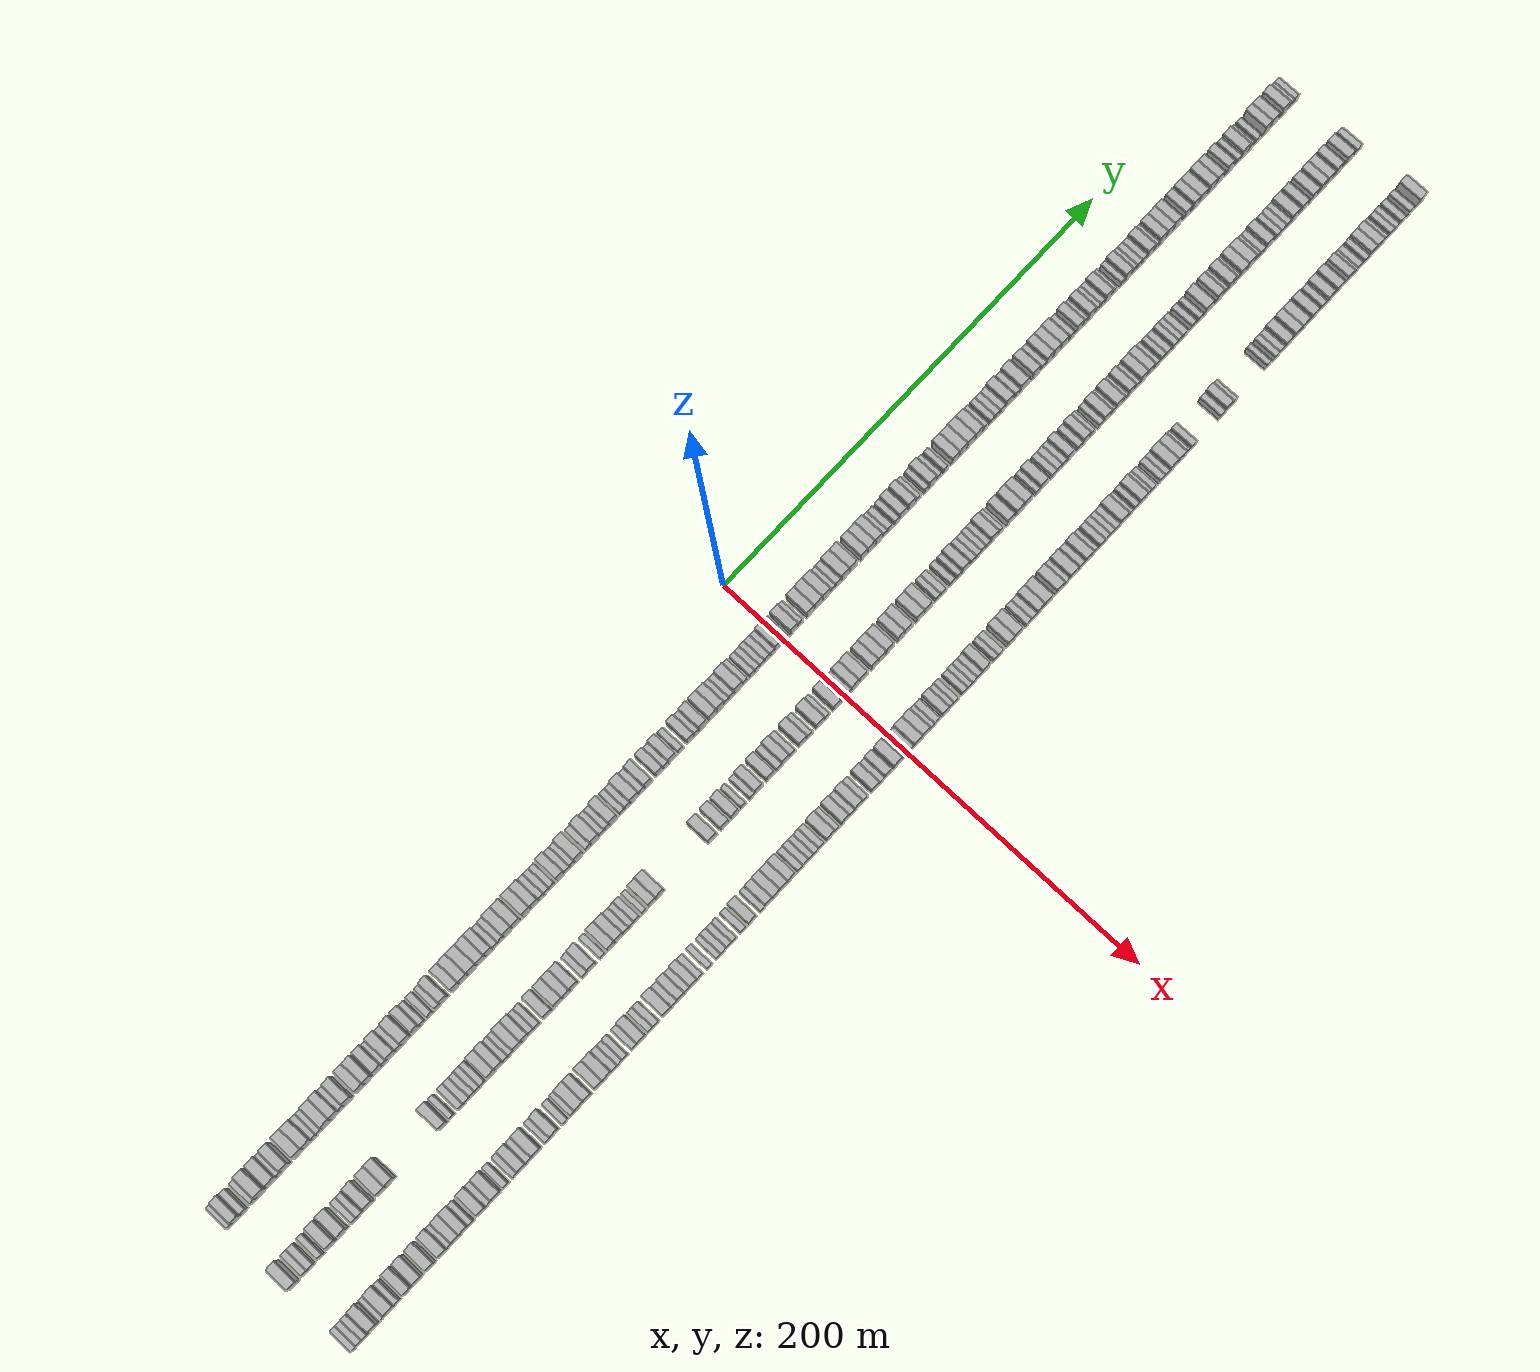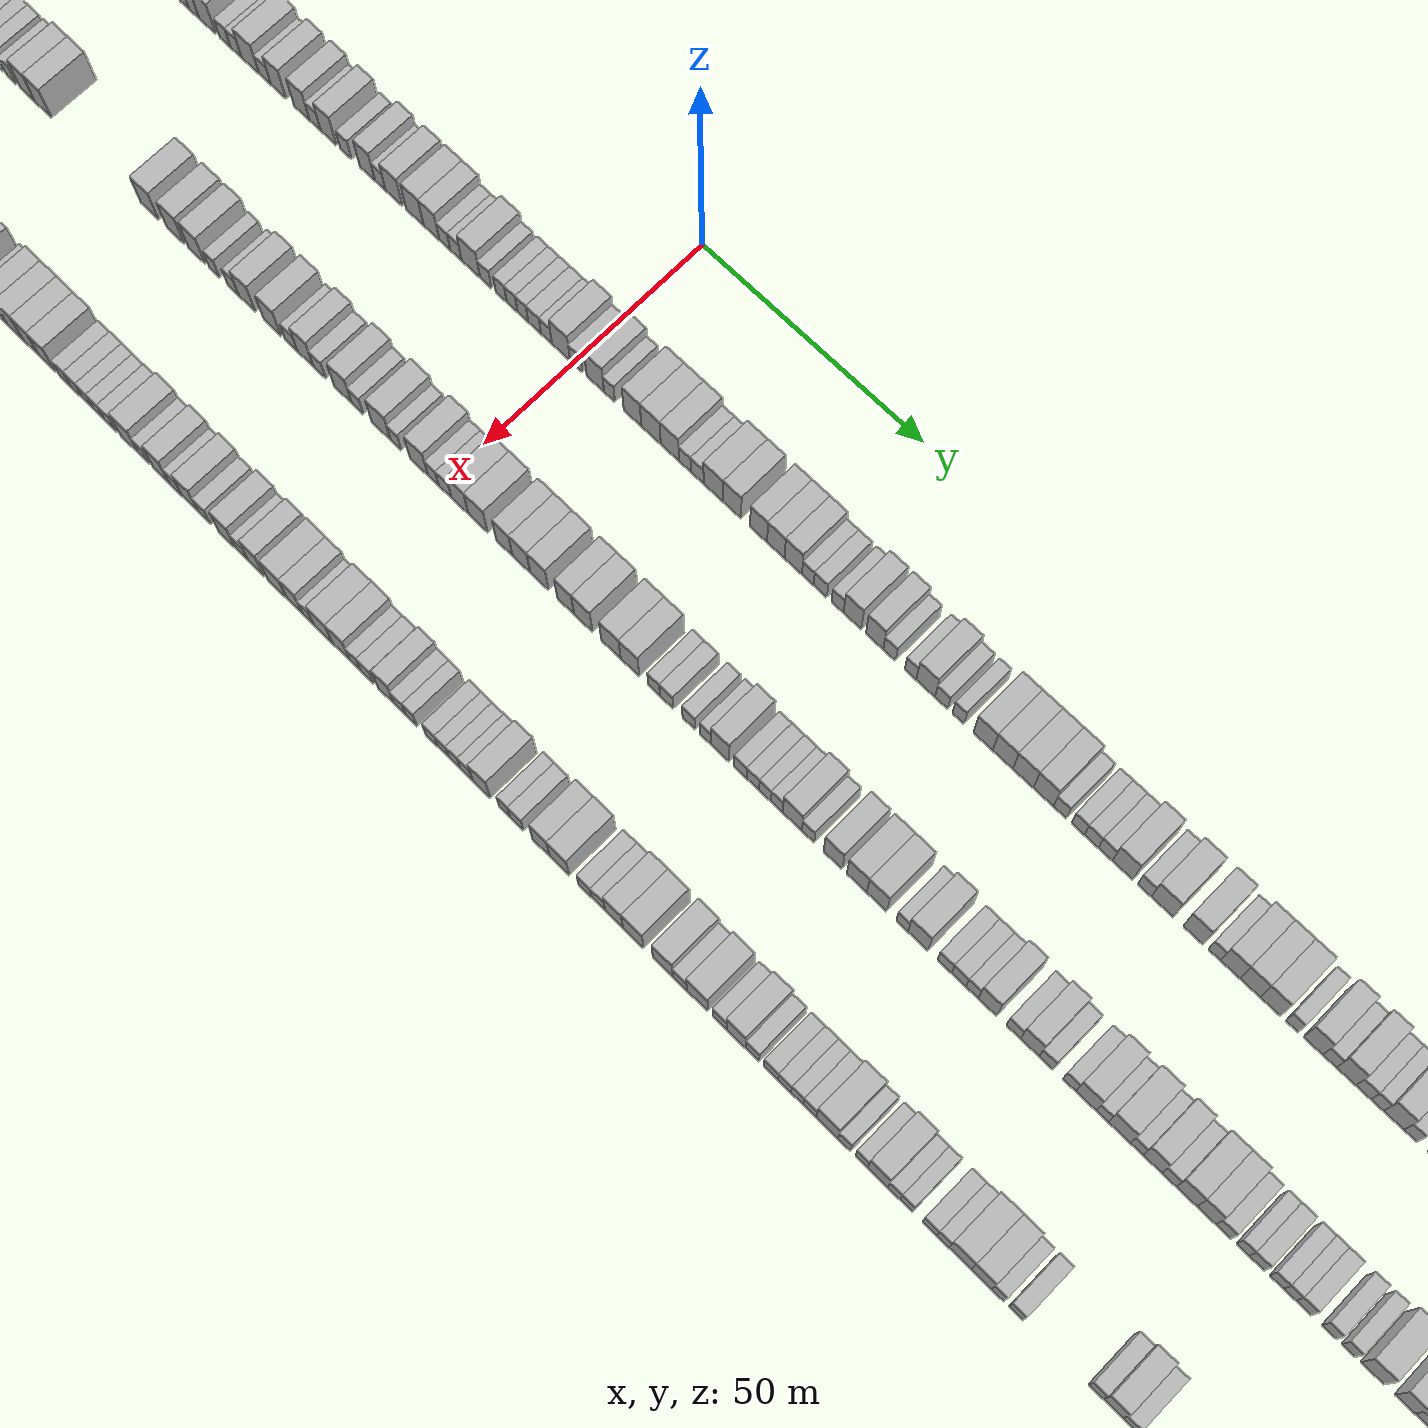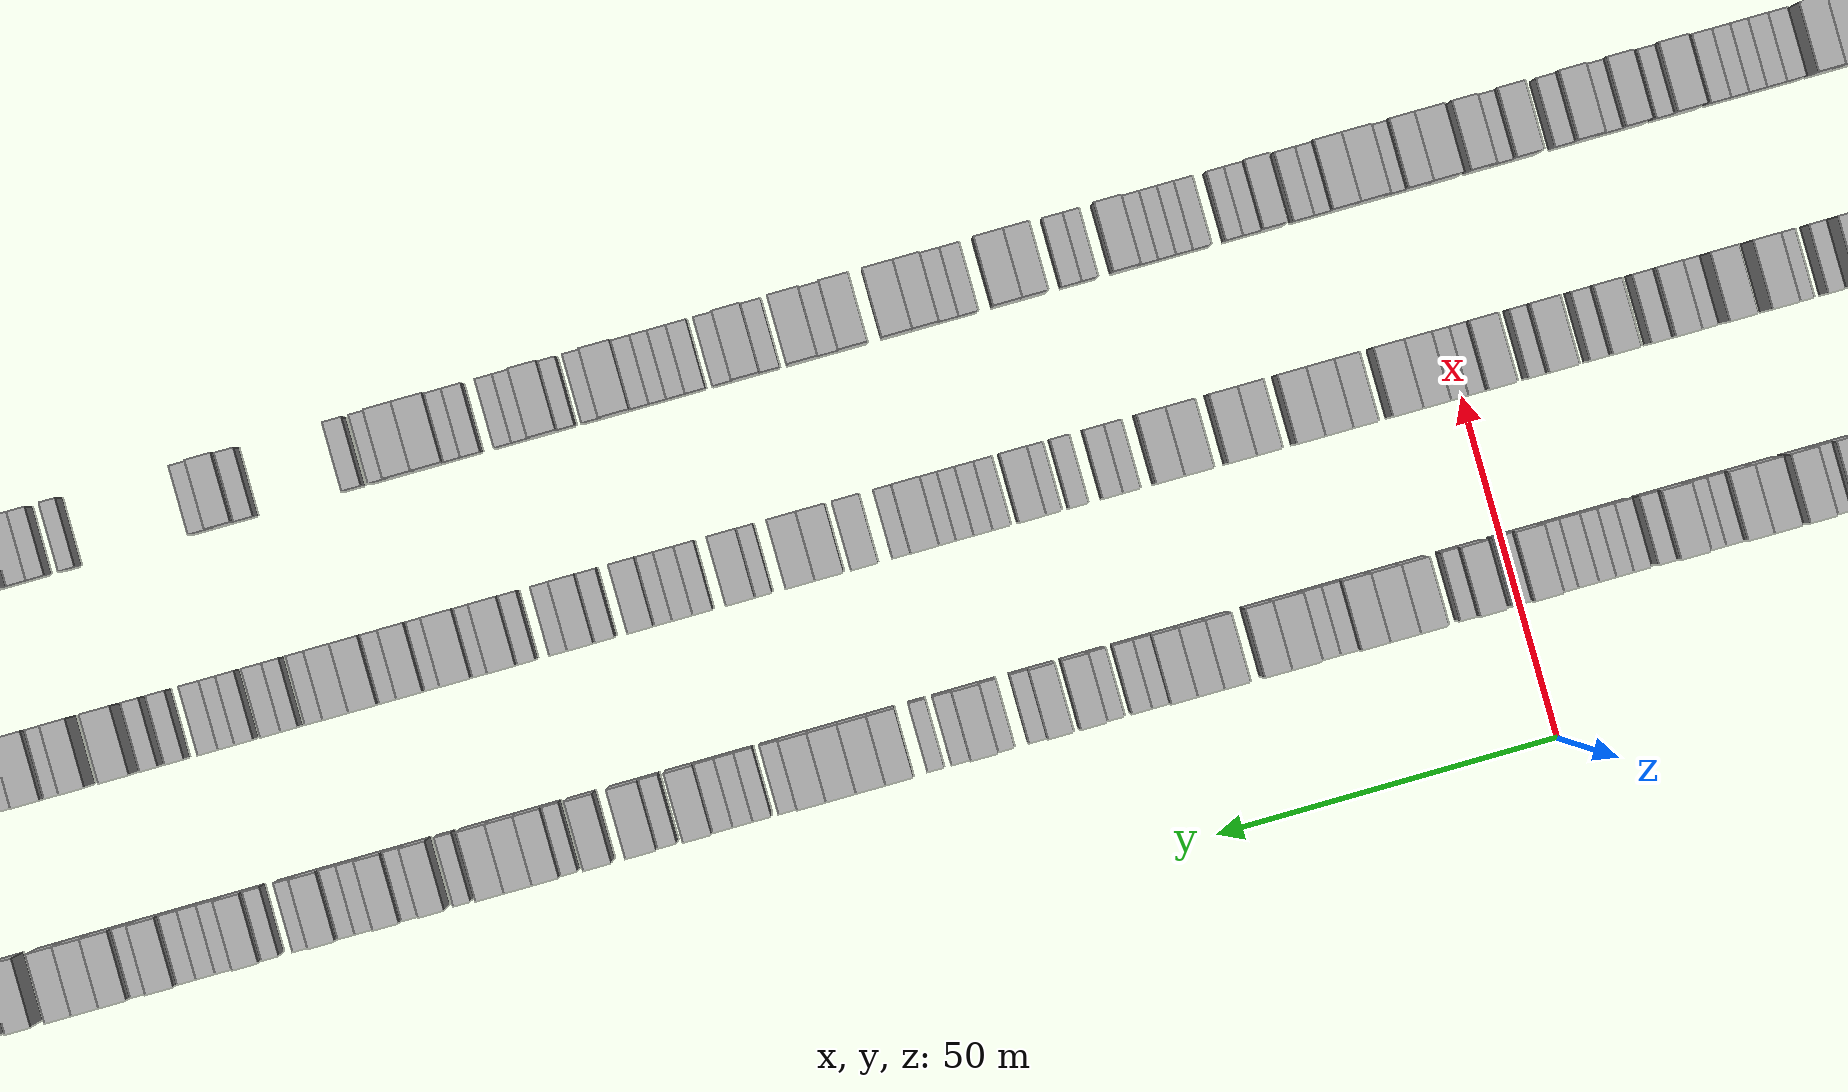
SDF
<sdf version="1.6">
 <world name="default">
  <scene>
   <sky><clouds><speed>12</speed></clouds></sky>
   <ambient>0.4 0.4 0.4 1</ambient>
   <background>0.7 0.7 0.7 1</background>
   <shadows>1</shadows>
  </scene>
  <gravity>0 0 -9.8066</gravity>
  <magnetic_field>6e-06 2.3e-05 -4.2e-05</magnetic_field>
  <physics default="0" name="default_physics" type="ode">
   <ode>
    <solver>
     <type>quick</type>
     <iters>10</iters>
     <sor>1.0</sor>
     <use_dynamic_moi_rescaling>0</use_dynamic_moi_rescaling>
    </solver>
    <constraints>
     <cfm>0</cfm>
     <erp>0.2</erp>
     <contact_max_correcting_vel>100</contact_max_correcting_vel>
     <contact_surface_layer>0.001</contact_surface_layer>
    </constraints>
   </ode>
   <max_step_size>0.004</max_step_size>
   <real_time_factor>1</real_time_factor>
   <real_time_update_rate>250</real_time_update_rate>
  </physics>
  <light name="sun" type="directional">
   <pose>0 0 10 0 0 0</pose>
   <diffuse>0.8 0.8 0.8 1</diffuse>
   <specular>0.2 0.2 0.2 1</specular>
   <attenuation>
    <range>1000</range>
    <constant>0.9</constant>
    <linear>0.01</linear>
    <quadratic>0.001</quadratic>
   </attenuation>
   <direction>-0.5 0.1 -0.9</direction>
  </light>
  <model name="building_1">
   <static>1</static>
   <pose>25.0000 -278.7704 0 0.000000 0.000000 0.000000</pose>
   <link name="link">
    <pose>0 0 3.00 0 0 0</pose>
    <collision name="collision"><geometry><box><size>10.0000 2.4591 6.0000</size></box></geometry></collision>
    <visual name="visual">
     <cast_shadows>0</cast_shadows>
     <geometry><box><size>10.0000 2.4591 6.0000</size></box></geometry>
     <material>
      <script>
       <uri>model://HANNAS_wall/materials/scripts</uri>
       <uri>model://HANNAS_wall/materials/textures</uri>
       <name>vrc/HANNAS_wall</name>
      </script>
     </material>
    </visual>
   </link>
  </model>
  <model name="building_2">
   <static>1</static>
   <pose>25.0000 -275.6036 0 0.000000 0.000000 0.000000</pose>
   <link name="link">
    <pose>0 0 4.50 0 0 0</pose>
    <collision name="collision"><geometry><box><size>10.0000 3.8746 9.0000</size></box></geometry></collision>
    <visual name="visual">
     <cast_shadows>0</cast_shadows>
     <geometry><box><size>10.0000 3.8746 9.0000</size></box></geometry>
     <material>
      <script>
       <uri>model://HANNAS_wall/materials/scripts</uri>
       <uri>model://HANNAS_wall/materials/textures</uri>
       <name>vrc/HANNAS_wall</name>
      </script>
     </material>
    </visual>
   </link>
  </model>
  <model name="building_3">
   <static>1</static>
   <pose>25.0000 -272.2474 0 0.000000 0.000000 0.000000</pose>
   <link name="link">
    <pose>0 0 3.00 0 0 0</pose>
    <collision name="collision"><geometry><box><size>10.0000 2.8378 6.0000</size></box></geometry></collision>
    <visual name="visual">
     <cast_shadows>0</cast_shadows>
     <geometry><box><size>10.0000 2.8378 6.0000</size></box></geometry>
     <material>
      <script>
       <uri>model://HANNAS_wall/materials/scripts</uri>
       <uri>model://HANNAS_wall/materials/textures</uri>
       <name>vrc/HANNAS_wall</name>
      </script>
     </material>
    </visual>
   </link>
  </model>
  <model name="building_4">
   <static>1</static>
   <pose>25.0000 -267.4222 0 0.000000 0.000000 0.000000</pose>
   <link name="link">
    <pose>0 0 3.00 0 0 0</pose>
    <collision name="collision"><geometry><box><size>10.0000 2.8126 6.0000</size></box></geometry></collision>
    <visual name="visual">
     <cast_shadows>0</cast_shadows>
     <geometry><box><size>10.0000 2.8126 6.0000</size></box></geometry>
     <material>
      <script>
       <uri>model://HANNAS_wall/materials/scripts</uri>
       <uri>model://HANNAS_wall/materials/textures</uri>
       <name>vrc/HANNAS_wall</name>
      </script>
     </material>
    </visual>
   </link>
  </model>
  <model name="building_5">
   <static>1</static>
   <pose>25.0000 -263.8523 0 0.000000 0.000000 0.000000</pose>
   <link name="link">
    <pose>0 0 4.50 0 0 0</pose>
    <collision name="collision"><geometry><box><size>10.0000 4.3272 9.0000</size></box></geometry></collision>
    <visual name="visual">
     <cast_shadows>0</cast_shadows>
     <geometry><box><size>10.0000 4.3272 9.0000</size></box></geometry>
     <material>
      <script>
       <uri>model://HANNAS_wall/materials/scripts</uri>
       <uri>model://HANNAS_wall/materials/textures</uri>
       <name>vrc/HANNAS_wall</name>
      </script>
     </material>
    </visual>
   </link>
  </model>
  <model name="building_6">
   <static>1</static>
   <pose>25.0000 -258.4551 0 0.000000 0.000000 0.000000</pose>
   <link name="link">
    <pose>0 0 4.50 0 0 0</pose>
    <collision name="collision"><geometry><box><size>10.0000 4.4672 9.0000</size></box></geometry></collision>
    <visual name="visual">
     <cast_shadows>0</cast_shadows>
     <geometry><box><size>10.0000 4.4672 9.0000</size></box></geometry>
     <material>
      <script>
       <uri>model://HANNAS_wall/materials/scripts</uri>
       <uri>model://HANNAS_wall/materials/textures</uri>
       <name>vrc/HANNAS_wall</name>
      </script>
     </material>
    </visual>
   </link>
  </model>
  <model name="building_7">
   <static>1</static>
   <pose>25.0000 -254.9983 0 0.000000 0.000000 0.000000</pose>
   <link name="link">
    <pose>0 0 3.00 0 0 0</pose>
    <collision name="collision"><geometry><box><size>10.0000 2.4464 6.0000</size></box></geometry></collision>
    <visual name="visual">
     <cast_shadows>0</cast_shadows>
     <geometry><box><size>10.0000 2.4464 6.0000</size></box></geometry>
     <material>
      <script>
       <uri>model://HANNAS_wall/materials/scripts</uri>
       <uri>model://HANNAS_wall/materials/textures</uri>
       <name>vrc/HANNAS_wall</name>
      </script>
     </material>
    </visual>
   </link>
  </model>
  <model name="building_8">
   <static>1</static>
   <pose>25.0000 -251.7890 0 0.000000 0.000000 0.000000</pose>
   <link name="link">
    <pose>0 0 4.50 0 0 0</pose>
    <collision name="collision"><geometry><box><size>10.0000 3.9722 9.0000</size></box></geometry></collision>
    <visual name="visual">
     <cast_shadows>0</cast_shadows>
     <geometry><box><size>10.0000 3.9722 9.0000</size></box></geometry>
     <material>
      <script>
       <uri>model://HANNAS_wall/materials/scripts</uri>
       <uri>model://HANNAS_wall/materials/textures</uri>
       <name>vrc/HANNAS_wall</name>
      </script>
     </material>
    </visual>
   </link>
  </model>
  <model name="building_9">
   <static>1</static>
   <pose>25.0000 -245.5877 0 0.000000 0.000000 0.000000</pose>
   <link name="link">
    <pose>0 0 4.50 0 0 0</pose>
    <collision name="collision"><geometry><box><size>10.0000 4.4304 9.0000</size></box></geometry></collision>
    <visual name="visual">
     <cast_shadows>0</cast_shadows>
     <geometry><box><size>10.0000 4.4304 9.0000</size></box></geometry>
     <material>
      <script>
       <uri>model://HANNAS_wall/materials/scripts</uri>
       <uri>model://HANNAS_wall/materials/textures</uri>
       <name>vrc/HANNAS_wall</name>
      </script>
     </material>
    </visual>
   </link>
  </model>
  <model name="building_10">
   <static>1</static>
   <pose>25.0000 -241.2524 0 0.000000 0.000000 0.000000</pose>
   <link name="link">
    <pose>0 0 4.50 0 0 0</pose>
    <collision name="collision"><geometry><box><size>10.0000 4.2402 9.0000</size></box></geometry></collision>
    <visual name="visual">
     <cast_shadows>0</cast_shadows>
     <geometry><box><size>10.0000 4.2402 9.0000</size></box></geometry>
     <material>
      <script>
       <uri>model://HANNAS_wall/materials/scripts</uri>
       <uri>model://HANNAS_wall/materials/textures</uri>
       <name>vrc/HANNAS_wall</name>
      </script>
     </material>
    </visual>
   </link>
  </model>
  <model name="building_11">
   <static>1</static>
   <pose>25.0000 -237.8776 0 0.000000 0.000000 0.000000</pose>
   <link name="link">
    <pose>0 0 3.00 0 0 0</pose>
    <collision name="collision"><geometry><box><size>10.0000 2.5093 6.0000</size></box></geometry></collision>
    <visual name="visual">
     <cast_shadows>0</cast_shadows>
     <geometry><box><size>10.0000 2.5093 6.0000</size></box></geometry>
     <material>
      <script>
       <uri>model://HANNAS_wall/materials/scripts</uri>
       <uri>model://HANNAS_wall/materials/textures</uri>
       <name>vrc/HANNAS_wall</name>
      </script>
     </material>
    </visual>
   </link>
  </model>
  <model name="building_12">
   <static>1</static>
   <pose>25.0000 -235.2699 0 0.000000 0.000000 0.000000</pose>
   <link name="link">
    <pose>0 0 3.00 0 0 0</pose>
    <collision name="collision"><geometry><box><size>10.0000 2.7062 6.0000</size></box></geometry></collision>
    <visual name="visual">
     <cast_shadows>0</cast_shadows>
     <geometry><box><size>10.0000 2.7062 6.0000</size></box></geometry>
     <material>
      <script>
       <uri>model://HANNAS_wall/materials/scripts</uri>
       <uri>model://HANNAS_wall/materials/textures</uri>
       <name>vrc/HANNAS_wall</name>
      </script>
     </material>
    </visual>
   </link>
  </model>
  <model name="building_13">
   <static>1</static>
   <pose>25.0000 -231.7873 0 0.000000 0.000000 0.000000</pose>
   <link name="link">
    <pose>0 0 4.50 0 0 0</pose>
    <collision name="collision"><geometry><box><size>10.0000 4.2591 9.0000</size></box></geometry></collision>
    <visual name="visual">
     <cast_shadows>0</cast_shadows>
     <geometry><box><size>10.0000 4.2591 9.0000</size></box></geometry>
     <material>
      <script>
       <uri>model://HANNAS_wall/materials/scripts</uri>
       <uri>model://HANNAS_wall/materials/textures</uri>
       <name>vrc/HANNAS_wall</name>
      </script>
     </material>
    </visual>
   </link>
  </model>
  <model name="building_14">
   <static>1</static>
   <pose>25.0000 -227.7850 0 0.000000 0.000000 0.000000</pose>
   <link name="link">
    <pose>0 0 4.50 0 0 0</pose>
    <collision name="collision"><geometry><box><size>10.0000 3.7455 9.0000</size></box></geometry></collision>
    <visual name="visual">
     <cast_shadows>0</cast_shadows>
     <geometry><box><size>10.0000 3.7455 9.0000</size></box></geometry>
     <material>
      <script>
       <uri>model://HANNAS_wall/materials/scripts</uri>
       <uri>model://HANNAS_wall/materials/textures</uri>
       <name>vrc/HANNAS_wall</name>
      </script>
     </material>
    </visual>
   </link>
  </model>
  <model name="building_15">
   <static>1</static>
   <pose>25.0000 -224.5746 0 0.000000 0.000000 0.000000</pose>
   <link name="link">
    <pose>0 0 3.00 0 0 0</pose>
    <collision name="collision"><geometry><box><size>10.0000 2.6752 6.0000</size></box></geometry></collision>
    <visual name="visual">
     <cast_shadows>0</cast_shadows>
     <geometry><box><size>10.0000 2.6752 6.0000</size></box></geometry>
     <material>
      <script>
       <uri>model://HANNAS_wall/materials/scripts</uri>
       <uri>model://HANNAS_wall/materials/textures</uri>
       <name>vrc/HANNAS_wall</name>
      </script>
     </material>
    </visual>
   </link>
  </model>
  <model name="building_16">
   <static>1</static>
   <pose>25.0000 -221.2788 0 0.000000 0.000000 0.000000</pose>
   <link name="link">
    <pose>0 0 4.50 0 0 0</pose>
    <collision name="collision"><geometry><box><size>10.0000 3.9164 9.0000</size></box></geometry></collision>
    <visual name="visual">
     <cast_shadows>0</cast_shadows>
     <geometry><box><size>10.0000 3.9164 9.0000</size></box></geometry>
     <material>
      <script>
       <uri>model://HANNAS_wall/materials/scripts</uri>
       <uri>model://HANNAS_wall/materials/textures</uri>
       <name>vrc/HANNAS_wall</name>
      </script>
     </material>
    </visual>
   </link>
  </model>
  <model name="building_17">
   <static>1</static>
   <pose>25.0000 -215.3214 0 0.000000 0.000000 0.000000</pose>
   <link name="link">
    <pose>0 0 4.50 0 0 0</pose>
    <collision name="collision"><geometry><box><size>10.0000 3.9984 9.0000</size></box></geometry></collision>
    <visual name="visual">
     <cast_shadows>0</cast_shadows>
     <geometry><box><size>10.0000 3.9984 9.0000</size></box></geometry>
     <material>
      <script>
       <uri>model://HANNAS_wall/materials/scripts</uri>
       <uri>model://HANNAS_wall/materials/textures</uri>
       <name>vrc/HANNAS_wall</name>
      </script>
     </material>
    </visual>
   </link>
  </model>
  <model name="building_18">
   <static>1</static>
   <pose>25.0000 -211.3917 0 0.000000 0.000000 0.000000</pose>
   <link name="link">
    <pose>0 0 4.50 0 0 0</pose>
    <collision name="collision"><geometry><box><size>10.0000 3.8610 9.0000</size></box></geometry></collision>
    <visual name="visual">
     <cast_shadows>0</cast_shadows>
     <geometry><box><size>10.0000 3.8610 9.0000</size></box></geometry>
     <material>
      <script>
       <uri>model://HANNAS_wall/materials/scripts</uri>
       <uri>model://HANNAS_wall/materials/textures</uri>
       <name>vrc/HANNAS_wall</name>
      </script>
     </material>
    </visual>
   </link>
  </model>
  <model name="building_19">
   <static>1</static>
   <pose>25.0000 -206.5305 0 0.000000 0.000000 0.000000</pose>
   <link name="link">
    <pose>0 0 4.50 0 0 0</pose>
    <collision name="collision"><geometry><box><size>10.0000 3.8614 9.0000</size></box></geometry></collision>
    <visual name="visual">
     <cast_shadows>0</cast_shadows>
     <geometry><box><size>10.0000 3.8614 9.0000</size></box></geometry>
     <material>
      <script>
       <uri>model://HANNAS_wall/materials/scripts</uri>
       <uri>model://HANNAS_wall/materials/textures</uri>
       <name>vrc/HANNAS_wall</name>
      </script>
     </material>
    </visual>
   </link>
  </model>
  <model name="building_20">
   <static>1</static>
   <pose>25.0000 -203.3896 0 0.000000 0.000000 0.000000</pose>
   <link name="link">
    <pose>0 0 3.00 0 0 0</pose>
    <collision name="collision"><geometry><box><size>10.0000 2.4204 6.0000</size></box></geometry></collision>
    <visual name="visual">
     <cast_shadows>0</cast_shadows>
     <geometry><box><size>10.0000 2.4204 6.0000</size></box></geometry>
     <material>
      <script>
       <uri>model://HANNAS_wall/materials/scripts</uri>
       <uri>model://HANNAS_wall/materials/textures</uri>
       <name>vrc/HANNAS_wall</name>
      </script>
     </material>
    </visual>
   </link>
  </model>
  <model name="building_21">
   <static>1</static>
   <pose>25.0000 -200.0525 0 0.000000 0.000000 0.000000</pose>
   <link name="link">
    <pose>0 0 4.50 0 0 0</pose>
    <collision name="collision"><geometry><box><size>10.0000 4.2536 9.0000</size></box></geometry></collision>
    <visual name="visual">
     <cast_shadows>0</cast_shadows>
     <geometry><box><size>10.0000 4.2536 9.0000</size></box></geometry>
     <material>
      <script>
       <uri>model://HANNAS_wall/materials/scripts</uri>
       <uri>model://HANNAS_wall/materials/textures</uri>
       <name>vrc/HANNAS_wall</name>
      </script>
     </material>
    </visual>
   </link>
  </model>
  <model name="building_22">
   <static>1</static>
   <pose>25.0000 -196.4762 0 0.000000 0.000000 0.000000</pose>
   <link name="link">
    <pose>0 0 3.00 0 0 0</pose>
    <collision name="collision"><geometry><box><size>10.0000 2.8991 6.0000</size></box></geometry></collision>
    <visual name="visual">
     <cast_shadows>0</cast_shadows>
     <geometry><box><size>10.0000 2.8991 6.0000</size></box></geometry>
     <material>
      <script>
       <uri>model://HANNAS_wall/materials/scripts</uri>
       <uri>model://HANNAS_wall/materials/textures</uri>
       <name>vrc/HANNAS_wall</name>
      </script>
     </material>
    </visual>
   </link>
  </model>
  <model name="building_23">
   <static>1</static>
   <pose>25.0000 -192.8627 0 0.000000 0.000000 0.000000</pose>
   <link name="link">
    <pose>0 0 4.50 0 0 0</pose>
    <collision name="collision"><geometry><box><size>10.0000 4.3278 9.0000</size></box></geometry></collision>
    <visual name="visual">
     <cast_shadows>0</cast_shadows>
     <geometry><box><size>10.0000 4.3278 9.0000</size></box></geometry>
     <material>
      <script>
       <uri>model://HANNAS_wall/materials/scripts</uri>
       <uri>model://HANNAS_wall/materials/textures</uri>
       <name>vrc/HANNAS_wall</name>
      </script>
     </material>
    </visual>
   </link>
  </model>
  <model name="building_24">
   <static>1</static>
   <pose>25.0000 -187.8923 0 0.000000 0.000000 0.000000</pose>
   <link name="link">
    <pose>0 0 4.50 0 0 0</pose>
    <collision name="collision"><geometry><box><size>10.0000 3.6131 9.0000</size></box></geometry></collision>
    <visual name="visual">
     <cast_shadows>0</cast_shadows>
     <geometry><box><size>10.0000 3.6131 9.0000</size></box></geometry>
     <material>
      <script>
       <uri>model://HANNAS_wall/materials/scripts</uri>
       <uri>model://HANNAS_wall/materials/textures</uri>
       <name>vrc/HANNAS_wall</name>
      </script>
     </material>
    </visual>
   </link>
  </model>
  <model name="building_25">
   <static>1</static>
   <pose>25.0000 -184.8343 0 0.000000 0.000000 0.000000</pose>
   <link name="link">
    <pose>0 0 3.00 0 0 0</pose>
    <collision name="collision"><geometry><box><size>10.0000 2.5029 6.0000</size></box></geometry></collision>
    <visual name="visual">
     <cast_shadows>0</cast_shadows>
     <geometry><box><size>10.0000 2.5029 6.0000</size></box></geometry>
     <material>
      <script>
       <uri>model://HANNAS_wall/materials/scripts</uri>
       <uri>model://HANNAS_wall/materials/textures</uri>
       <name>vrc/HANNAS_wall</name>
      </script>
     </material>
    </visual>
   </link>
  </model>
  <model name="building_26">
   <static>1</static>
   <pose>25.0000 -181.0926 0 0.000000 0.000000 0.000000</pose>
   <link name="link">
    <pose>0 0 3.00 0 0 0</pose>
    <collision name="collision"><geometry><box><size>10.0000 2.9805 6.0000</size></box></geometry></collision>
    <visual name="visual">
     <cast_shadows>0</cast_shadows>
     <geometry><box><size>10.0000 2.9805 6.0000</size></box></geometry>
     <material>
      <script>
       <uri>model://HANNAS_wall/materials/scripts</uri>
       <uri>model://HANNAS_wall/materials/textures</uri>
       <name>vrc/HANNAS_wall</name>
      </script>
     </material>
    </visual>
   </link>
  </model>
  <model name="building_27">
   <static>1</static>
   <pose>25.0000 -177.2182 0 0.000000 0.000000 0.000000</pose>
   <link name="link">
    <pose>0 0 3.00 0 0 0</pose>
    <collision name="collision"><geometry><box><size>10.0000 2.7682 6.0000</size></box></geometry></collision>
    <visual name="visual">
     <cast_shadows>0</cast_shadows>
     <geometry><box><size>10.0000 2.7682 6.0000</size></box></geometry>
     <material>
      <script>
       <uri>model://HANNAS_wall/materials/scripts</uri>
       <uri>model://HANNAS_wall/materials/textures</uri>
       <name>vrc/HANNAS_wall</name>
      </script>
     </material>
    </visual>
   </link>
  </model>
  <model name="building_28">
   <static>1</static>
   <pose>25.0000 -173.9266 0 0.000000 0.000000 0.000000</pose>
   <link name="link">
    <pose>0 0 4.50 0 0 0</pose>
    <collision name="collision"><geometry><box><size>10.0000 3.8148 9.0000</size></box></geometry></collision>
    <visual name="visual">
     <cast_shadows>0</cast_shadows>
     <geometry><box><size>10.0000 3.8148 9.0000</size></box></geometry>
     <material>
      <script>
       <uri>model://HANNAS_wall/materials/scripts</uri>
       <uri>model://HANNAS_wall/materials/textures</uri>
       <name>vrc/HANNAS_wall</name>
      </script>
     </material>
    </visual>
   </link>
  </model>
  <model name="building_29">
   <static>1</static>
   <pose>25.0000 -168.0928 0 0.000000 0.000000 0.000000</pose>
   <link name="link">
    <pose>0 0 4.50 0 0 0</pose>
    <collision name="collision"><geometry><box><size>10.0000 3.8529 9.0000</size></box></geometry></collision>
    <visual name="visual">
     <cast_shadows>0</cast_shadows>
     <geometry><box><size>10.0000 3.8529 9.0000</size></box></geometry>
     <material>
      <script>
       <uri>model://HANNAS_wall/materials/scripts</uri>
       <uri>model://HANNAS_wall/materials/textures</uri>
       <name>vrc/HANNAS_wall</name>
      </script>
     </material>
    </visual>
   </link>
  </model>
  <model name="building_30">
   <static>1</static>
   <pose>25.0000 -164.1106 0 0.000000 0.000000 0.000000</pose>
   <link name="link">
    <pose>0 0 4.50 0 0 0</pose>
    <collision name="collision"><geometry><box><size>10.0000 4.1115 9.0000</size></box></geometry></collision>
    <visual name="visual">
     <cast_shadows>0</cast_shadows>
     <geometry><box><size>10.0000 4.1115 9.0000</size></box></geometry>
     <material>
      <script>
       <uri>model://HANNAS_wall/materials/scripts</uri>
       <uri>model://HANNAS_wall/materials/textures</uri>
       <name>vrc/HANNAS_wall</name>
      </script>
     </material>
    </visual>
   </link>
  </model>
  <model name="building_31">
   <static>1</static>
   <pose>25.0000 -159.8074 0 0.000000 0.000000 0.000000</pose>
   <link name="link">
    <pose>0 0 4.50 0 0 0</pose>
    <collision name="collision"><geometry><box><size>10.0000 4.4949 9.0000</size></box></geometry></collision>
    <visual name="visual">
     <cast_shadows>0</cast_shadows>
     <geometry><box><size>10.0000 4.4949 9.0000</size></box></geometry>
     <material>
      <script>
       <uri>model://HANNAS_wall/materials/scripts</uri>
       <uri>model://HANNAS_wall/materials/textures</uri>
       <name>vrc/HANNAS_wall</name>
      </script>
     </material>
    </visual>
   </link>
  </model>
  <model name="building_32">
   <static>1</static>
   <pose>25.0000 -155.4286 0 0.000000 0.000000 0.000000</pose>
   <link name="link">
    <pose>0 0 4.50 0 0 0</pose>
    <collision name="collision"><geometry><box><size>10.0000 4.2628 9.0000</size></box></geometry></collision>
    <visual name="visual">
     <cast_shadows>0</cast_shadows>
     <geometry><box><size>10.0000 4.2628 9.0000</size></box></geometry>
     <material>
      <script>
       <uri>model://HANNAS_wall/materials/scripts</uri>
       <uri>model://HANNAS_wall/materials/textures</uri>
       <name>vrc/HANNAS_wall</name>
      </script>
     </material>
    </visual>
   </link>
  </model>
  <model name="building_33">
   <static>1</static>
   <pose>25.0000 -151.4691 0 0.000000 0.000000 0.000000</pose>
   <link name="link">
    <pose>0 0 4.50 0 0 0</pose>
    <collision name="collision"><geometry><box><size>10.0000 3.6561 9.0000</size></box></geometry></collision>
    <visual name="visual">
     <cast_shadows>0</cast_shadows>
     <geometry><box><size>10.0000 3.6561 9.0000</size></box></geometry>
     <material>
      <script>
       <uri>model://HANNAS_wall/materials/scripts</uri>
       <uri>model://HANNAS_wall/materials/textures</uri>
       <name>vrc/HANNAS_wall</name>
      </script>
     </material>
    </visual>
   </link>
  </model>
  <model name="building_34">
   <static>1</static>
   <pose>25.0000 -148.3323 0 0.000000 0.000000 0.000000</pose>
   <link name="link">
    <pose>0 0 3.00 0 0 0</pose>
    <collision name="collision"><geometry><box><size>10.0000 2.6176 6.0000</size></box></geometry></collision>
    <visual name="visual">
     <cast_shadows>0</cast_shadows>
     <geometry><box><size>10.0000 2.6176 6.0000</size></box></geometry>
     <material>
      <script>
       <uri>model://HANNAS_wall/materials/scripts</uri>
       <uri>model://HANNAS_wall/materials/textures</uri>
       <name>vrc/HANNAS_wall</name>
      </script>
     </material>
    </visual>
   </link>
  </model>
  <model name="building_35">
   <static>1</static>
   <pose>25.0000 -145.5900 0 0.000000 0.000000 0.000000</pose>
   <link name="link">
    <pose>0 0 3.00 0 0 0</pose>
    <collision name="collision"><geometry><box><size>10.0000 2.8671 6.0000</size></box></geometry></collision>
    <visual name="visual">
     <cast_shadows>0</cast_shadows>
     <geometry><box><size>10.0000 2.8671 6.0000</size></box></geometry>
     <material>
      <script>
       <uri>model://HANNAS_wall/materials/scripts</uri>
       <uri>model://HANNAS_wall/materials/textures</uri>
       <name>vrc/HANNAS_wall</name>
      </script>
     </material>
    </visual>
   </link>
  </model>
  <model name="building_36">
   <static>1</static>
   <pose>25.0000 -142.0021 0 0.000000 0.000000 0.000000</pose>
   <link name="link">
    <pose>0 0 4.50 0 0 0</pose>
    <collision name="collision"><geometry><box><size>10.0000 4.3087 9.0000</size></box></geometry></collision>
    <visual name="visual">
     <cast_shadows>0</cast_shadows>
     <geometry><box><size>10.0000 4.3087 9.0000</size></box></geometry>
     <material>
      <script>
       <uri>model://HANNAS_wall/materials/scripts</uri>
       <uri>model://HANNAS_wall/materials/textures</uri>
       <name>vrc/HANNAS_wall</name>
      </script>
     </material>
    </visual>
   </link>
  </model>
  <model name="building_37">
   <static>1</static>
   <pose>25.0000 -137.7536 0 0.000000 0.000000 0.000000</pose>
   <link name="link">
    <pose>0 0 4.50 0 0 0</pose>
    <collision name="collision"><geometry><box><size>10.0000 4.1883 9.0000</size></box></geometry></collision>
    <visual name="visual">
     <cast_shadows>0</cast_shadows>
     <geometry><box><size>10.0000 4.1883 9.0000</size></box></geometry>
     <material>
      <script>
       <uri>model://HANNAS_wall/materials/scripts</uri>
       <uri>model://HANNAS_wall/materials/textures</uri>
       <name>vrc/HANNAS_wall</name>
      </script>
     </material>
    </visual>
   </link>
  </model>
  <model name="building_38">
   <static>1</static>
   <pose>25.0000 -132.5895 0 0.000000 0.000000 0.000000</pose>
   <link name="link">
    <pose>0 0 4.50 0 0 0</pose>
    <collision name="collision"><geometry><box><size>10.0000 4.1399 9.0000</size></box></geometry></collision>
    <visual name="visual">
     <cast_shadows>0</cast_shadows>
     <geometry><box><size>10.0000 4.1399 9.0000</size></box></geometry>
     <material>
      <script>
       <uri>model://HANNAS_wall/materials/scripts</uri>
       <uri>model://HANNAS_wall/materials/textures</uri>
       <name>vrc/HANNAS_wall</name>
      </script>
     </material>
    </visual>
   </link>
  </model>
  <model name="building_39">
   <static>1</static>
   <pose>25.0000 -128.5618 0 0.000000 0.000000 0.000000</pose>
   <link name="link">
    <pose>0 0 4.50 0 0 0</pose>
    <collision name="collision"><geometry><box><size>10.0000 3.9155 9.0000</size></box></geometry></collision>
    <visual name="visual">
     <cast_shadows>0</cast_shadows>
     <geometry><box><size>10.0000 3.9155 9.0000</size></box></geometry>
     <material>
      <script>
       <uri>model://HANNAS_wall/materials/scripts</uri>
       <uri>model://HANNAS_wall/materials/textures</uri>
       <name>vrc/HANNAS_wall</name>
      </script>
     </material>
    </visual>
   </link>
  </model>
  <model name="building_40">
   <static>1</static>
   <pose>25.0000 -125.2381 0 0.000000 0.000000 0.000000</pose>
   <link name="link">
    <pose>0 0 3.00 0 0 0</pose>
    <collision name="collision"><geometry><box><size>10.0000 2.7320 6.0000</size></box></geometry></collision>
    <visual name="visual">
     <cast_shadows>0</cast_shadows>
     <geometry><box><size>10.0000 2.7320 6.0000</size></box></geometry>
     <material>
      <script>
       <uri>model://HANNAS_wall/materials/scripts</uri>
       <uri>model://HANNAS_wall/materials/textures</uri>
       <name>vrc/HANNAS_wall</name>
      </script>
     </material>
    </visual>
   </link>
  </model>
  <model name="building_41">
   <static>1</static>
   <pose>25.0000 -122.4755 0 0.000000 0.000000 0.000000</pose>
   <link name="link">
    <pose>0 0 3.00 0 0 0</pose>
    <collision name="collision"><geometry><box><size>10.0000 2.7931 6.0000</size></box></geometry></collision>
    <visual name="visual">
     <cast_shadows>0</cast_shadows>
     <geometry><box><size>10.0000 2.7931 6.0000</size></box></geometry>
     <material>
      <script>
       <uri>model://HANNAS_wall/materials/scripts</uri>
       <uri>model://HANNAS_wall/materials/textures</uri>
       <name>vrc/HANNAS_wall</name>
      </script>
     </material>
    </visual>
   </link>
  </model>
  <model name="building_42">
   <static>1</static>
   <pose>25.0000 -119.7278 0 0.000000 0.000000 0.000000</pose>
   <link name="link">
    <pose>0 0 3.00 0 0 0</pose>
    <collision name="collision"><geometry><box><size>10.0000 2.7024 6.0000</size></box></geometry></collision>
    <visual name="visual">
     <cast_shadows>0</cast_shadows>
     <geometry><box><size>10.0000 2.7024 6.0000</size></box></geometry>
     <material>
      <script>
       <uri>model://HANNAS_wall/materials/scripts</uri>
       <uri>model://HANNAS_wall/materials/textures</uri>
       <name>vrc/HANNAS_wall</name>
      </script>
     </material>
    </visual>
   </link>
  </model>
  <model name="building_43">
   <static>1</static>
   <pose>25.0000 -115.4467 0 0.000000 0.000000 0.000000</pose>
   <link name="link">
    <pose>0 0 4.50 0 0 0</pose>
    <collision name="collision"><geometry><box><size>10.0000 3.8599 9.0000</size></box></geometry></collision>
    <visual name="visual">
     <cast_shadows>0</cast_shadows>
     <geometry><box><size>10.0000 3.8599 9.0000</size></box></geometry>
     <material>
      <script>
       <uri>model://HANNAS_wall/materials/scripts</uri>
       <uri>model://HANNAS_wall/materials/textures</uri>
       <name>vrc/HANNAS_wall</name>
      </script>
     </material>
    </visual>
   </link>
  </model>
  <model name="building_44">
   <static>1</static>
   <pose>25.0000 -112.1142 0 0.000000 0.000000 0.000000</pose>
   <link name="link">
    <pose>0 0 3.00 0 0 0</pose>
    <collision name="collision"><geometry><box><size>10.0000 2.8050 6.0000</size></box></geometry></collision>
    <visual name="visual">
     <cast_shadows>0</cast_shadows>
     <geometry><box><size>10.0000 2.8050 6.0000</size></box></geometry>
     <material>
      <script>
       <uri>model://HANNAS_wall/materials/scripts</uri>
       <uri>model://HANNAS_wall/materials/textures</uri>
       <name>vrc/HANNAS_wall</name>
      </script>
     </material>
    </visual>
   </link>
  </model>
  <model name="building_45">
   <static>1</static>
   <pose>25.0000 -109.5059 0 0.000000 0.000000 0.000000</pose>
   <link name="link">
    <pose>0 0 3.00 0 0 0</pose>
    <collision name="collision"><geometry><box><size>10.0000 2.4118 6.0000</size></box></geometry></collision>
    <visual name="visual">
     <cast_shadows>0</cast_shadows>
     <geometry><box><size>10.0000 2.4118 6.0000</size></box></geometry>
     <material>
      <script>
       <uri>model://HANNAS_wall/materials/scripts</uri>
       <uri>model://HANNAS_wall/materials/textures</uri>
       <name>vrc/HANNAS_wall</name>
      </script>
     </material>
    </visual>
   </link>
  </model>
  <model name="building_46">
   <static>1</static>
   <pose>25.0000 -106.1355 0 0.000000 0.000000 0.000000</pose>
   <link name="link">
    <pose>0 0 4.50 0 0 0</pose>
    <collision name="collision"><geometry><box><size>10.0000 4.3289 9.0000</size></box></geometry></collision>
    <visual name="visual">
     <cast_shadows>0</cast_shadows>
     <geometry><box><size>10.0000 4.3289 9.0000</size></box></geometry>
     <material>
      <script>
       <uri>model://HANNAS_wall/materials/scripts</uri>
       <uri>model://HANNAS_wall/materials/textures</uri>
       <name>vrc/HANNAS_wall</name>
      </script>
     </material>
    </visual>
   </link>
  </model>
  <model name="building_47">
   <static>1</static>
   <pose>25.0000 -101.5284 0 0.000000 0.000000 0.000000</pose>
   <link name="link">
    <pose>0 0 3.00 0 0 0</pose>
    <collision name="collision"><geometry><box><size>10.0000 2.8853 6.0000</size></box></geometry></collision>
    <visual name="visual">
     <cast_shadows>0</cast_shadows>
     <geometry><box><size>10.0000 2.8853 6.0000</size></box></geometry>
     <material>
      <script>
       <uri>model://HANNAS_wall/materials/scripts</uri>
       <uri>model://HANNAS_wall/materials/textures</uri>
       <name>vrc/HANNAS_wall</name>
      </script>
     </material>
    </visual>
   </link>
  </model>
  <model name="building_48">
   <static>1</static>
   <pose>25.0000 -97.8976 0 0.000000 0.000000 0.000000</pose>
   <link name="link">
    <pose>0 0 4.50 0 0 0</pose>
    <collision name="collision"><geometry><box><size>10.0000 4.3762 9.0000</size></box></geometry></collision>
    <visual name="visual">
     <cast_shadows>0</cast_shadows>
     <geometry><box><size>10.0000 4.3762 9.0000</size></box></geometry>
     <material>
      <script>
       <uri>model://HANNAS_wall/materials/scripts</uri>
       <uri>model://HANNAS_wall/materials/textures</uri>
       <name>vrc/HANNAS_wall</name>
      </script>
     </material>
    </visual>
   </link>
  </model>
  <model name="building_49">
   <static>1</static>
   <pose>25.0000 -94.4482 0 0.000000 0.000000 0.000000</pose>
   <link name="link">
    <pose>0 0 3.00 0 0 0</pose>
    <collision name="collision"><geometry><box><size>10.0000 2.5226 6.0000</size></box></geometry></collision>
    <visual name="visual">
     <cast_shadows>0</cast_shadows>
     <geometry><box><size>10.0000 2.5226 6.0000</size></box></geometry>
     <material>
      <script>
       <uri>model://HANNAS_wall/materials/scripts</uri>
       <uri>model://HANNAS_wall/materials/textures</uri>
       <name>vrc/HANNAS_wall</name>
      </script>
     </material>
    </visual>
   </link>
  </model>
  <model name="building_50">
   <static>1</static>
   <pose>25.0000 -91.9061 0 0.000000 0.000000 0.000000</pose>
   <link name="link">
    <pose>0 0 3.00 0 0 0</pose>
    <collision name="collision"><geometry><box><size>10.0000 2.5616 6.0000</size></box></geometry></collision>
    <visual name="visual">
     <cast_shadows>0</cast_shadows>
     <geometry><box><size>10.0000 2.5616 6.0000</size></box></geometry>
     <material>
      <script>
       <uri>model://HANNAS_wall/materials/scripts</uri>
       <uri>model://HANNAS_wall/materials/textures</uri>
       <name>vrc/HANNAS_wall</name>
      </script>
     </material>
    </visual>
   </link>
  </model>
  <model name="building_51">
   <static>1</static>
   <pose>25.0000 -88.5378 0 0.000000 0.000000 0.000000</pose>
   <link name="link">
    <pose>0 0 4.50 0 0 0</pose>
    <collision name="collision"><geometry><box><size>10.0000 4.1751 9.0000</size></box></geometry></collision>
    <visual name="visual">
     <cast_shadows>0</cast_shadows>
     <geometry><box><size>10.0000 4.1751 9.0000</size></box></geometry>
     <material>
      <script>
       <uri>model://HANNAS_wall/materials/scripts</uri>
       <uri>model://HANNAS_wall/materials/textures</uri>
       <name>vrc/HANNAS_wall</name>
      </script>
     </material>
    </visual>
   </link>
  </model>
  <model name="building_52">
   <static>1</static>
   <pose>25.0000 -84.0903 0 0.000000 0.000000 0.000000</pose>
   <link name="link">
    <pose>0 0 3.00 0 0 0</pose>
    <collision name="collision"><geometry><box><size>10.0000 2.7198 6.0000</size></box></geometry></collision>
    <visual name="visual">
     <cast_shadows>0</cast_shadows>
     <geometry><box><size>10.0000 2.7198 6.0000</size></box></geometry>
     <material>
      <script>
       <uri>model://HANNAS_wall/materials/scripts</uri>
       <uri>model://HANNAS_wall/materials/textures</uri>
       <name>vrc/HANNAS_wall</name>
      </script>
     </material>
    </visual>
   </link>
  </model>
  <model name="building_53">
   <static>1</static>
   <pose>25.0000 -81.3624 0 0.000000 0.000000 0.000000</pose>
   <link name="link">
    <pose>0 0 3.00 0 0 0</pose>
    <collision name="collision"><geometry><box><size>10.0000 2.7360 6.0000</size></box></geometry></collision>
    <visual name="visual">
     <cast_shadows>0</cast_shadows>
     <geometry><box><size>10.0000 2.7360 6.0000</size></box></geometry>
     <material>
      <script>
       <uri>model://HANNAS_wall/materials/scripts</uri>
       <uri>model://HANNAS_wall/materials/textures</uri>
       <name>vrc/HANNAS_wall</name>
      </script>
     </material>
    </visual>
   </link>
  </model>
  <model name="building_54">
   <static>1</static>
   <pose>25.0000 -77.7741 0 0.000000 0.000000 0.000000</pose>
   <link name="link">
    <pose>0 0 4.50 0 0 0</pose>
    <collision name="collision"><geometry><box><size>10.0000 4.4407 9.0000</size></box></geometry></collision>
    <visual name="visual">
     <cast_shadows>0</cast_shadows>
     <geometry><box><size>10.0000 4.4407 9.0000</size></box></geometry>
     <material>
      <script>
       <uri>model://HANNAS_wall/materials/scripts</uri>
       <uri>model://HANNAS_wall/materials/textures</uri>
       <name>vrc/HANNAS_wall</name>
      </script>
     </material>
    </visual>
   </link>
  </model>
  <model name="building_55">
   <static>1</static>
   <pose>25.0000 -74.0879 0 0.000000 0.000000 0.000000</pose>
   <link name="link">
    <pose>0 0 3.00 0 0 0</pose>
    <collision name="collision"><geometry><box><size>10.0000 2.9318 6.0000</size></box></geometry></collision>
    <visual name="visual">
     <cast_shadows>0</cast_shadows>
     <geometry><box><size>10.0000 2.9318 6.0000</size></box></geometry>
     <material>
      <script>
       <uri>model://HANNAS_wall/materials/scripts</uri>
       <uri>model://HANNAS_wall/materials/textures</uri>
       <name>vrc/HANNAS_wall</name>
      </script>
     </material>
    </visual>
   </link>
  </model>
  <model name="building_56">
   <static>1</static>
   <pose>25.0000 -70.7549 0 0.000000 0.000000 0.000000</pose>
   <link name="link">
    <pose>0 0 4.50 0 0 0</pose>
    <collision name="collision"><geometry><box><size>10.0000 3.7342 9.0000</size></box></geometry></collision>
    <visual name="visual">
     <cast_shadows>0</cast_shadows>
     <geometry><box><size>10.0000 3.7342 9.0000</size></box></geometry>
     <material>
      <script>
       <uri>model://HANNAS_wall/materials/scripts</uri>
       <uri>model://HANNAS_wall/materials/textures</uri>
       <name>vrc/HANNAS_wall</name>
      </script>
     </material>
    </visual>
   </link>
  </model>
  <model name="building_57">
   <static>1</static>
   <pose>25.0000 -64.9796 0 0.000000 0.000000 0.000000</pose>
   <link name="link">
    <pose>0 0 4.50 0 0 0</pose>
    <collision name="collision"><geometry><box><size>10.0000 3.8163 9.0000</size></box></geometry></collision>
    <visual name="visual">
     <cast_shadows>0</cast_shadows>
     <geometry><box><size>10.0000 3.8163 9.0000</size></box></geometry>
     <material>
      <script>
       <uri>model://HANNAS_wall/materials/scripts</uri>
       <uri>model://HANNAS_wall/materials/textures</uri>
       <name>vrc/HANNAS_wall</name>
      </script>
     </material>
    </visual>
   </link>
  </model>
  <model name="building_58">
   <static>1</static>
   <pose>25.0000 -61.7101 0 0.000000 0.000000 0.000000</pose>
   <link name="link">
    <pose>0 0 3.00 0 0 0</pose>
    <collision name="collision"><geometry><box><size>10.0000 2.7228 6.0000</size></box></geometry></collision>
    <visual name="visual">
     <cast_shadows>0</cast_shadows>
     <geometry><box><size>10.0000 2.7228 6.0000</size></box></geometry>
     <material>
      <script>
       <uri>model://HANNAS_wall/materials/scripts</uri>
       <uri>model://HANNAS_wall/materials/textures</uri>
       <name>vrc/HANNAS_wall</name>
      </script>
     </material>
    </visual>
   </link>
  </model>
  <model name="building_59">
   <static>1</static>
   <pose>25.0000 -58.4369 0 0.000000 0.000000 0.000000</pose>
   <link name="link">
    <pose>0 0 4.50 0 0 0</pose>
    <collision name="collision"><geometry><box><size>10.0000 3.8235 9.0000</size></box></geometry></collision>
    <visual name="visual">
     <cast_shadows>0</cast_shadows>
     <geometry><box><size>10.0000 3.8235 9.0000</size></box></geometry>
     <material>
      <script>
       <uri>model://HANNAS_wall/materials/scripts</uri>
       <uri>model://HANNAS_wall/materials/textures</uri>
       <name>vrc/HANNAS_wall</name>
      </script>
     </material>
    </visual>
   </link>
  </model>
  <model name="building_60">
   <static>1</static>
   <pose>25.0000 -54.1493 0 0.000000 0.000000 0.000000</pose>
   <link name="link">
    <pose>0 0 3.00 0 0 0</pose>
    <collision name="collision"><geometry><box><size>10.0000 2.7516 6.0000</size></box></geometry></collision>
    <visual name="visual">
     <cast_shadows>0</cast_shadows>
     <geometry><box><size>10.0000 2.7516 6.0000</size></box></geometry>
     <material>
      <script>
       <uri>model://HANNAS_wall/materials/scripts</uri>
       <uri>model://HANNAS_wall/materials/textures</uri>
       <name>vrc/HANNAS_wall</name>
      </script>
     </material>
    </visual>
   </link>
  </model>
  <model name="building_61">
   <static>1</static>
   <pose>25.0000 -48.9335 0 0.000000 0.000000 0.000000</pose>
   <link name="link">
    <pose>0 0 4.50 0 0 0</pose>
    <collision name="collision"><geometry><box><size>10.0000 3.6802 9.0000</size></box></geometry></collision>
    <visual name="visual">
     <cast_shadows>0</cast_shadows>
     <geometry><box><size>10.0000 3.6802 9.0000</size></box></geometry>
     <material>
      <script>
       <uri>model://HANNAS_wall/materials/scripts</uri>
       <uri>model://HANNAS_wall/materials/textures</uri>
       <name>vrc/HANNAS_wall</name>
      </script>
     </material>
    </visual>
   </link>
  </model>
  <model name="building_62">
   <static>1</static>
   <pose>25.0000 -45.8114 0 0.000000 0.000000 0.000000</pose>
   <link name="link">
    <pose>0 0 3.00 0 0 0</pose>
    <collision name="collision"><geometry><box><size>10.0000 2.5641 6.0000</size></box></geometry></collision>
    <visual name="visual">
     <cast_shadows>0</cast_shadows>
     <geometry><box><size>10.0000 2.5641 6.0000</size></box></geometry>
     <material>
      <script>
       <uri>model://HANNAS_wall/materials/scripts</uri>
       <uri>model://HANNAS_wall/materials/textures</uri>
       <name>vrc/HANNAS_wall</name>
      </script>
     </material>
    </visual>
   </link>
  </model>
  <model name="building_63">
   <static>1</static>
   <pose>25.0000 -42.5181 0 0.000000 0.000000 0.000000</pose>
   <link name="link">
    <pose>0 0 4.50 0 0 0</pose>
    <collision name="collision"><geometry><box><size>10.0000 4.0225 9.0000</size></box></geometry></collision>
    <visual name="visual">
     <cast_shadows>0</cast_shadows>
     <geometry><box><size>10.0000 4.0225 9.0000</size></box></geometry>
     <material>
      <script>
       <uri>model://HANNAS_wall/materials/scripts</uri>
       <uri>model://HANNAS_wall/materials/textures</uri>
       <name>vrc/HANNAS_wall</name>
      </script>
     </material>
    </visual>
   </link>
  </model>
  <model name="building_64">
   <static>1</static>
   <pose>25.0000 -37.4297 0 0.000000 0.000000 0.000000</pose>
   <link name="link">
    <pose>0 0 4.50 0 0 0</pose>
    <collision name="collision"><geometry><box><size>10.0000 4.1541 9.0000</size></box></geometry></collision>
    <visual name="visual">
     <cast_shadows>0</cast_shadows>
     <geometry><box><size>10.0000 4.1541 9.0000</size></box></geometry>
     <material>
      <script>
       <uri>model://HANNAS_wall/materials/scripts</uri>
       <uri>model://HANNAS_wall/materials/textures</uri>
       <name>vrc/HANNAS_wall</name>
      </script>
     </material>
    </visual>
   </link>
  </model>
  <model name="building_65">
   <static>1</static>
   <pose>25.0000 -33.4504 0 0.000000 0.000000 0.000000</pose>
   <link name="link">
    <pose>0 0 4.50 0 0 0</pose>
    <collision name="collision"><geometry><box><size>10.0000 3.8045 9.0000</size></box></geometry></collision>
    <visual name="visual">
     <cast_shadows>0</cast_shadows>
     <geometry><box><size>10.0000 3.8045 9.0000</size></box></geometry>
     <material>
      <script>
       <uri>model://HANNAS_wall/materials/scripts</uri>
       <uri>model://HANNAS_wall/materials/textures</uri>
       <name>vrc/HANNAS_wall</name>
      </script>
     </material>
    </visual>
   </link>
  </model>
  <model name="building_66">
   <static>1</static>
   <pose>25.0000 -30.2639 0 0.000000 0.000000 0.000000</pose>
   <link name="link">
    <pose>0 0 3.00 0 0 0</pose>
    <collision name="collision"><geometry><box><size>10.0000 2.5685 6.0000</size></box></geometry></collision>
    <visual name="visual">
     <cast_shadows>0</cast_shadows>
     <geometry><box><size>10.0000 2.5685 6.0000</size></box></geometry>
     <material>
      <script>
       <uri>model://HANNAS_wall/materials/scripts</uri>
       <uri>model://HANNAS_wall/materials/textures</uri>
       <name>vrc/HANNAS_wall</name>
      </script>
     </material>
    </visual>
   </link>
  </model>
  <model name="building_67">
   <static>1</static>
   <pose>25.0000 -27.6307 0 0.000000 0.000000 0.000000</pose>
   <link name="link">
    <pose>0 0 3.00 0 0 0</pose>
    <collision name="collision"><geometry><box><size>10.0000 2.6978 6.0000</size></box></geometry></collision>
    <visual name="visual">
     <cast_shadows>0</cast_shadows>
     <geometry><box><size>10.0000 2.6978 6.0000</size></box></geometry>
     <material>
      <script>
       <uri>model://HANNAS_wall/materials/scripts</uri>
       <uri>model://HANNAS_wall/materials/textures</uri>
       <name>vrc/HANNAS_wall</name>
      </script>
     </material>
    </visual>
   </link>
  </model>
  <model name="building_68">
   <static>1</static>
   <pose>25.0000 -24.0842 0 0.000000 0.000000 0.000000</pose>
   <link name="link">
    <pose>0 0 4.50 0 0 0</pose>
    <collision name="collision"><geometry><box><size>10.0000 4.3952 9.0000</size></box></geometry></collision>
    <visual name="visual">
     <cast_shadows>0</cast_shadows>
     <geometry><box><size>10.0000 4.3952 9.0000</size></box></geometry>
     <material>
      <script>
       <uri>model://HANNAS_wall/materials/scripts</uri>
       <uri>model://HANNAS_wall/materials/textures</uri>
       <name>vrc/HANNAS_wall</name>
      </script>
     </material>
    </visual>
   </link>
  </model>
  <model name="building_69">
   <static>1</static>
   <pose>25.0000 -20.5479 0 0.000000 0.000000 0.000000</pose>
   <link name="link">
    <pose>0 0 3.00 0 0 0</pose>
    <collision name="collision"><geometry><box><size>10.0000 2.6774 6.0000</size></box></geometry></collision>
    <visual name="visual">
     <cast_shadows>0</cast_shadows>
     <geometry><box><size>10.0000 2.6774 6.0000</size></box></geometry>
     <material>
      <script>
       <uri>model://HANNAS_wall/materials/scripts</uri>
       <uri>model://HANNAS_wall/materials/textures</uri>
       <name>vrc/HANNAS_wall</name>
      </script>
     </material>
    </visual>
   </link>
  </model>
  <model name="building_70">
   <static>1</static>
   <pose>25.0000 -16.9094 0 0.000000 0.000000 0.000000</pose>
   <link name="link">
    <pose>0 0 3.00 0 0 0</pose>
    <collision name="collision"><geometry><box><size>10.0000 2.5997 6.0000</size></box></geometry></collision>
    <visual name="visual">
     <cast_shadows>0</cast_shadows>
     <geometry><box><size>10.0000 2.5997 6.0000</size></box></geometry>
     <material>
      <script>
       <uri>model://HANNAS_wall/materials/scripts</uri>
       <uri>model://HANNAS_wall/materials/textures</uri>
       <name>vrc/HANNAS_wall</name>
      </script>
     </material>
    </visual>
   </link>
  </model>
  <model name="building_71">
   <static>1</static>
   <pose>25.0000 -14.3302 0 0.000000 0.000000 0.000000</pose>
   <link name="link">
    <pose>0 0 3.00 0 0 0</pose>
    <collision name="collision"><geometry><box><size>10.0000 2.5587 6.0000</size></box></geometry></collision>
    <visual name="visual">
     <cast_shadows>0</cast_shadows>
     <geometry><box><size>10.0000 2.5587 6.0000</size></box></geometry>
     <material>
      <script>
       <uri>model://HANNAS_wall/materials/scripts</uri>
       <uri>model://HANNAS_wall/materials/textures</uri>
       <name>vrc/HANNAS_wall</name>
      </script>
     </material>
    </visual>
   </link>
  </model>
  <model name="building_72">
   <static>1</static>
   <pose>25.0000 -11.8022 0 0.000000 0.000000 0.000000</pose>
   <link name="link">
    <pose>0 0 3.00 0 0 0</pose>
    <collision name="collision"><geometry><box><size>10.0000 2.4972 6.0000</size></box></geometry></collision>
    <visual name="visual">
     <cast_shadows>0</cast_shadows>
     <geometry><box><size>10.0000 2.4972 6.0000</size></box></geometry>
     <material>
      <script>
       <uri>model://HANNAS_wall/materials/scripts</uri>
       <uri>model://HANNAS_wall/materials/textures</uri>
       <name>vrc/HANNAS_wall</name>
      </script>
     </material>
    </visual>
   </link>
  </model>
  <model name="building_73">
   <static>1</static>
   <pose>25.0000 -9.0564 0 0.000000 0.000000 0.000000</pose>
   <link name="link">
    <pose>0 0 3.00 0 0 0</pose>
    <collision name="collision"><geometry><box><size>10.0000 2.9945 6.0000</size></box></geometry></collision>
    <visual name="visual">
     <cast_shadows>0</cast_shadows>
     <geometry><box><size>10.0000 2.9945 6.0000</size></box></geometry>
     <material>
      <script>
       <uri>model://HANNAS_wall/materials/scripts</uri>
       <uri>model://HANNAS_wall/materials/textures</uri>
       <name>vrc/HANNAS_wall</name>
      </script>
     </material>
    </visual>
   </link>
  </model>
  <model name="building_74">
   <static>1</static>
   <pose>25.0000 -6.2886 0 0.000000 0.000000 0.000000</pose>
   <link name="link">
    <pose>0 0 3.00 0 0 0</pose>
    <collision name="collision"><geometry><box><size>10.0000 2.5412 6.0000</size></box></geometry></collision>
    <visual name="visual">
     <cast_shadows>0</cast_shadows>
     <geometry><box><size>10.0000 2.5412 6.0000</size></box></geometry>
     <material>
      <script>
       <uri>model://HANNAS_wall/materials/scripts</uri>
       <uri>model://HANNAS_wall/materials/textures</uri>
       <name>vrc/HANNAS_wall</name>
      </script>
     </material>
    </visual>
   </link>
  </model>
  <model name="building_75">
   <static>1</static>
   <pose>25.0000 -2.9095 0 0.000000 0.000000 0.000000</pose>
   <link name="link">
    <pose>0 0 4.50 0 0 0</pose>
    <collision name="collision"><geometry><box><size>10.0000 4.2168 9.0000</size></box></geometry></collision>
    <visual name="visual">
     <cast_shadows>0</cast_shadows>
     <geometry><box><size>10.0000 4.2168 9.0000</size></box></geometry>
     <material>
      <script>
       <uri>model://HANNAS_wall/materials/scripts</uri>
       <uri>model://HANNAS_wall/materials/textures</uri>
       <name>vrc/HANNAS_wall</name>
      </script>
     </material>
    </visual>
   </link>
  </model>
  <model name="building_76">
   <static>1</static>
   <pose>25.0000 0.6265 0 0.000000 0.000000 0.000000</pose>
   <link name="link">
    <pose>0 0 3.00 0 0 0</pose>
    <collision name="collision"><geometry><box><size>10.0000 2.8553 6.0000</size></box></geometry></collision>
    <visual name="visual">
     <cast_shadows>0</cast_shadows>
     <geometry><box><size>10.0000 2.8553 6.0000</size></box></geometry>
     <material>
      <script>
       <uri>model://HANNAS_wall/materials/scripts</uri>
       <uri>model://HANNAS_wall/materials/textures</uri>
       <name>vrc/HANNAS_wall</name>
      </script>
     </material>
    </visual>
   </link>
  </model>
  <model name="building_77">
   <static>1</static>
   <pose>25.0000 5.0600 0 0.000000 0.000000 0.000000</pose>
   <link name="link">
    <pose>0 0 4.50 0 0 0</pose>
    <collision name="collision"><geometry><box><size>10.0000 4.0116 9.0000</size></box></geometry></collision>
    <visual name="visual">
     <cast_shadows>0</cast_shadows>
     <geometry><box><size>10.0000 4.0116 9.0000</size></box></geometry>
     <material>
      <script>
       <uri>model://HANNAS_wall/materials/scripts</uri>
       <uri>model://HANNAS_wall/materials/textures</uri>
       <name>vrc/HANNAS_wall</name>
      </script>
     </material>
    </visual>
   </link>
  </model>
  <model name="building_78">
   <static>1</static>
   <pose>25.0000 8.3149 0 0.000000 0.000000 0.000000</pose>
   <link name="link">
    <pose>0 0 3.00 0 0 0</pose>
    <collision name="collision"><geometry><box><size>10.0000 2.4982 6.0000</size></box></geometry></collision>
    <visual name="visual">
     <cast_shadows>0</cast_shadows>
     <geometry><box><size>10.0000 2.4982 6.0000</size></box></geometry>
     <material>
      <script>
       <uri>model://HANNAS_wall/materials/scripts</uri>
       <uri>model://HANNAS_wall/materials/textures</uri>
       <name>vrc/HANNAS_wall</name>
      </script>
     </material>
    </visual>
   </link>
  </model>
  <model name="building_79">
   <static>1</static>
   <pose>25.0000 13.5983 0 0.000000 0.000000 0.000000</pose>
   <link name="link">
    <pose>0 0 4.50 0 0 0</pose>
    <collision name="collision"><geometry><box><size>10.0000 4.0687 9.0000</size></box></geometry></collision>
    <visual name="visual">
     <cast_shadows>0</cast_shadows>
     <geometry><box><size>10.0000 4.0687 9.0000</size></box></geometry>
     <material>
      <script>
       <uri>model://HANNAS_wall/materials/scripts</uri>
       <uri>model://HANNAS_wall/materials/textures</uri>
       <name>vrc/HANNAS_wall</name>
      </script>
     </material>
    </visual>
   </link>
  </model>
  <model name="building_80">
   <static>1</static>
   <pose>25.0000 17.8358 0 0.000000 0.000000 0.000000</pose>
   <link name="link">
    <pose>0 0 4.50 0 0 0</pose>
    <collision name="collision"><geometry><box><size>10.0000 4.4063 9.0000</size></box></geometry></collision>
    <visual name="visual">
     <cast_shadows>0</cast_shadows>
     <geometry><box><size>10.0000 4.4063 9.0000</size></box></geometry>
     <material>
      <script>
       <uri>model://HANNAS_wall/materials/scripts</uri>
       <uri>model://HANNAS_wall/materials/textures</uri>
       <name>vrc/HANNAS_wall</name>
      </script>
     </material>
    </visual>
   </link>
  </model>
  <model name="building_81">
   <static>1</static>
   <pose>25.0000 22.1220 0 0.000000 0.000000 0.000000</pose>
   <link name="link">
    <pose>0 0 4.50 0 0 0</pose>
    <collision name="collision"><geometry><box><size>10.0000 4.1660 9.0000</size></box></geometry></collision>
    <visual name="visual">
     <cast_shadows>0</cast_shadows>
     <geometry><box><size>10.0000 4.1660 9.0000</size></box></geometry>
     <material>
      <script>
       <uri>model://HANNAS_wall/materials/scripts</uri>
       <uri>model://HANNAS_wall/materials/textures</uri>
       <name>vrc/HANNAS_wall</name>
      </script>
     </material>
    </visual>
   </link>
  </model>
  <model name="building_82">
   <static>1</static>
   <pose>25.0000 25.5349 0 0.000000 0.000000 0.000000</pose>
   <link name="link">
    <pose>0 0 3.00 0 0 0</pose>
    <collision name="collision"><geometry><box><size>10.0000 2.6600 6.0000</size></box></geometry></collision>
    <visual name="visual">
     <cast_shadows>0</cast_shadows>
     <geometry><box><size>10.0000 2.6600 6.0000</size></box></geometry>
     <material>
      <script>
       <uri>model://HANNAS_wall/materials/scripts</uri>
       <uri>model://HANNAS_wall/materials/textures</uri>
       <name>vrc/HANNAS_wall</name>
      </script>
     </material>
    </visual>
   </link>
  </model>
  <model name="building_83">
   <static>1</static>
   <pose>25.0000 28.3083 0 0.000000 0.000000 0.000000</pose>
   <link name="link">
    <pose>0 0 3.00 0 0 0</pose>
    <collision name="collision"><geometry><box><size>10.0000 2.8868 6.0000</size></box></geometry></collision>
    <visual name="visual">
     <cast_shadows>0</cast_shadows>
     <geometry><box><size>10.0000 2.8868 6.0000</size></box></geometry>
     <material>
      <script>
       <uri>model://HANNAS_wall/materials/scripts</uri>
       <uri>model://HANNAS_wall/materials/textures</uri>
       <name>vrc/HANNAS_wall</name>
      </script>
     </material>
    </visual>
   </link>
  </model>
  <model name="building_84">
   <static>1</static>
   <pose>25.0000 31.9678 0 0.000000 0.000000 0.000000</pose>
   <link name="link">
    <pose>0 0 4.50 0 0 0</pose>
    <collision name="collision"><geometry><box><size>10.0000 4.4322 9.0000</size></box></geometry></collision>
    <visual name="visual">
     <cast_shadows>0</cast_shadows>
     <geometry><box><size>10.0000 4.4322 9.0000</size></box></geometry>
     <material>
      <script>
       <uri>model://HANNAS_wall/materials/scripts</uri>
       <uri>model://HANNAS_wall/materials/textures</uri>
       <name>vrc/HANNAS_wall</name>
      </script>
     </material>
    </visual>
   </link>
  </model>
  <model name="building_85">
   <static>1</static>
   <pose>25.0000 36.1779 0 0.000000 0.000000 0.000000</pose>
   <link name="link">
    <pose>0 0 4.50 0 0 0</pose>
    <collision name="collision"><geometry><box><size>10.0000 3.9880 9.0000</size></box></geometry></collision>
    <visual name="visual">
     <cast_shadows>0</cast_shadows>
     <geometry><box><size>10.0000 3.9880 9.0000</size></box></geometry>
     <material>
      <script>
       <uri>model://HANNAS_wall/materials/scripts</uri>
       <uri>model://HANNAS_wall/materials/textures</uri>
       <name>vrc/HANNAS_wall</name>
      </script>
     </material>
    </visual>
   </link>
  </model>
  <model name="building_86">
   <static>1</static>
   <pose>25.0000 42.0599 0 0.000000 0.000000 0.000000</pose>
   <link name="link">
    <pose>0 0 4.50 0 0 0</pose>
    <collision name="collision"><geometry><box><size>10.0000 3.7759 9.0000</size></box></geometry></collision>
    <visual name="visual">
     <cast_shadows>0</cast_shadows>
     <geometry><box><size>10.0000 3.7759 9.0000</size></box></geometry>
     <material>
      <script>
       <uri>model://HANNAS_wall/materials/scripts</uri>
       <uri>model://HANNAS_wall/materials/textures</uri>
       <name>vrc/HANNAS_wall</name>
      </script>
     </material>
    </visual>
   </link>
  </model>
  <model name="building_87">
   <static>1</static>
   <pose>25.0000 45.8835 0 0.000000 0.000000 0.000000</pose>
   <link name="link">
    <pose>0 0 4.50 0 0 0</pose>
    <collision name="collision"><geometry><box><size>10.0000 3.8713 9.0000</size></box></geometry></collision>
    <visual name="visual">
     <cast_shadows>0</cast_shadows>
     <geometry><box><size>10.0000 3.8713 9.0000</size></box></geometry>
     <material>
      <script>
       <uri>model://HANNAS_wall/materials/scripts</uri>
       <uri>model://HANNAS_wall/materials/textures</uri>
       <name>vrc/HANNAS_wall</name>
      </script>
     </material>
    </visual>
   </link>
  </model>
  <model name="building_88">
   <static>1</static>
   <pose>25.0000 49.7420 0 0.000000 0.000000 0.000000</pose>
   <link name="link">
    <pose>0 0 4.50 0 0 0</pose>
    <collision name="collision"><geometry><box><size>10.0000 3.8457 9.0000</size></box></geometry></collision>
    <visual name="visual">
     <cast_shadows>0</cast_shadows>
     <geometry><box><size>10.0000 3.8457 9.0000</size></box></geometry>
     <material>
      <script>
       <uri>model://HANNAS_wall/materials/scripts</uri>
       <uri>model://HANNAS_wall/materials/textures</uri>
       <name>vrc/HANNAS_wall</name>
      </script>
     </material>
    </visual>
   </link>
  </model>
  <model name="building_89">
   <static>1</static>
   <pose>25.0000 52.9456 0 0.000000 0.000000 0.000000</pose>
   <link name="link">
    <pose>0 0 3.00 0 0 0</pose>
    <collision name="collision"><geometry><box><size>10.0000 2.5616 6.0000</size></box></geometry></collision>
    <visual name="visual">
     <cast_shadows>0</cast_shadows>
     <geometry><box><size>10.0000 2.5616 6.0000</size></box></geometry>
     <material>
      <script>
       <uri>model://HANNAS_wall/materials/scripts</uri>
       <uri>model://HANNAS_wall/materials/textures</uri>
       <name>vrc/HANNAS_wall</name>
      </script>
     </material>
    </visual>
   </link>
  </model>
  <model name="building_90">
   <static>1</static>
   <pose>25.0000 55.6881 0 0.000000 0.000000 0.000000</pose>
   <link name="link">
    <pose>0 0 3.00 0 0 0</pose>
    <collision name="collision"><geometry><box><size>10.0000 2.9235 6.0000</size></box></geometry></collision>
    <visual name="visual">
     <cast_shadows>0</cast_shadows>
     <geometry><box><size>10.0000 2.9235 6.0000</size></box></geometry>
     <material>
      <script>
       <uri>model://HANNAS_wall/materials/scripts</uri>
       <uri>model://HANNAS_wall/materials/textures</uri>
       <name>vrc/HANNAS_wall</name>
      </script>
     </material>
    </visual>
   </link>
  </model>
  <model name="building_91">
   <static>1</static>
   <pose>25.0000 59.4676 0 0.000000 0.000000 0.000000</pose>
   <link name="link">
    <pose>0 0 3.00 0 0 0</pose>
    <collision name="collision"><geometry><box><size>10.0000 2.6355 6.0000</size></box></geometry></collision>
    <visual name="visual">
     <cast_shadows>0</cast_shadows>
     <geometry><box><size>10.0000 2.6355 6.0000</size></box></geometry>
     <material>
      <script>
       <uri>model://HANNAS_wall/materials/scripts</uri>
       <uri>model://HANNAS_wall/materials/textures</uri>
       <name>vrc/HANNAS_wall</name>
      </script>
     </material>
    </visual>
   </link>
  </model>
  <model name="building_92">
   <static>1</static>
   <pose>25.0000 62.7281 0 0.000000 0.000000 0.000000</pose>
   <link name="link">
    <pose>0 0 4.50 0 0 0</pose>
    <collision name="collision"><geometry><box><size>10.0000 3.8855 9.0000</size></box></geometry></collision>
    <visual name="visual">
     <cast_shadows>0</cast_shadows>
     <geometry><box><size>10.0000 3.8855 9.0000</size></box></geometry>
     <material>
      <script>
       <uri>model://HANNAS_wall/materials/scripts</uri>
       <uri>model://HANNAS_wall/materials/textures</uri>
       <name>vrc/HANNAS_wall</name>
      </script>
     </material>
    </visual>
   </link>
  </model>
  <model name="building_93">
   <static>1</static>
   <pose>25.0000 67.5539 0 0.000000 0.000000 0.000000</pose>
   <link name="link">
    <pose>0 0 4.50 0 0 0</pose>
    <collision name="collision"><geometry><box><size>10.0000 3.7661 9.0000</size></box></geometry></collision>
    <visual name="visual">
     <cast_shadows>0</cast_shadows>
     <geometry><box><size>10.0000 3.7661 9.0000</size></box></geometry>
     <material>
      <script>
       <uri>model://HANNAS_wall/materials/scripts</uri>
       <uri>model://HANNAS_wall/materials/textures</uri>
       <name>vrc/HANNAS_wall</name>
      </script>
     </material>
    </visual>
   </link>
  </model>
  <model name="building_94">
   <static>1</static>
   <pose>25.0000 70.7635 0 0.000000 0.000000 0.000000</pose>
   <link name="link">
    <pose>0 0 3.00 0 0 0</pose>
    <collision name="collision"><geometry><box><size>10.0000 2.6532 6.0000</size></box></geometry></collision>
    <visual name="visual">
     <cast_shadows>0</cast_shadows>
     <geometry><box><size>10.0000 2.6532 6.0000</size></box></geometry>
     <material>
      <script>
       <uri>model://HANNAS_wall/materials/scripts</uri>
       <uri>model://HANNAS_wall/materials/textures</uri>
       <name>vrc/HANNAS_wall</name>
      </script>
     </material>
    </visual>
   </link>
  </model>
  <model name="building_95">
   <static>1</static>
   <pose>25.0000 75.3304 0 0.000000 0.000000 0.000000</pose>
   <link name="link">
    <pose>0 0 3.00 0 0 0</pose>
    <collision name="collision"><geometry><box><size>10.0000 2.4804 6.0000</size></box></geometry></collision>
    <visual name="visual">
     <cast_shadows>0</cast_shadows>
     <geometry><box><size>10.0000 2.4804 6.0000</size></box></geometry>
     <material>
      <script>
       <uri>model://HANNAS_wall/materials/scripts</uri>
       <uri>model://HANNAS_wall/materials/textures</uri>
       <name>vrc/HANNAS_wall</name>
      </script>
     </material>
    </visual>
   </link>
  </model>
  <model name="building_96">
   <static>1</static>
   <pose>25.0000 78.5699 0 0.000000 0.000000 0.000000</pose>
   <link name="link">
    <pose>0 0 4.50 0 0 0</pose>
    <collision name="collision"><geometry><box><size>10.0000 3.9987 9.0000</size></box></geometry></collision>
    <visual name="visual">
     <cast_shadows>0</cast_shadows>
     <geometry><box><size>10.0000 3.9987 9.0000</size></box></geometry>
     <material>
      <script>
       <uri>model://HANNAS_wall/materials/scripts</uri>
       <uri>model://HANNAS_wall/materials/textures</uri>
       <name>vrc/HANNAS_wall</name>
      </script>
     </material>
    </visual>
   </link>
  </model>
  <model name="building_97">
   <static>1</static>
   <pose>25.0000 81.9426 0 0.000000 0.000000 0.000000</pose>
   <link name="link">
    <pose>0 0 3.00 0 0 0</pose>
    <collision name="collision"><geometry><box><size>10.0000 2.7467 6.0000</size></box></geometry></collision>
    <visual name="visual">
     <cast_shadows>0</cast_shadows>
     <geometry><box><size>10.0000 2.7467 6.0000</size></box></geometry>
     <material>
      <script>
       <uri>model://HANNAS_wall/materials/scripts</uri>
       <uri>model://HANNAS_wall/materials/textures</uri>
       <name>vrc/HANNAS_wall</name>
      </script>
     </material>
    </visual>
   </link>
  </model>
  <model name="building_98">
   <static>1</static>
   <pose>25.0000 85.5604 0 0.000000 0.000000 0.000000</pose>
   <link name="link">
    <pose>0 0 3.00 0 0 0</pose>
    <collision name="collision"><geometry><box><size>10.0000 2.4888 6.0000</size></box></geometry></collision>
    <visual name="visual">
     <cast_shadows>0</cast_shadows>
     <geometry><box><size>10.0000 2.4888 6.0000</size></box></geometry>
     <material>
      <script>
       <uri>model://HANNAS_wall/materials/scripts</uri>
       <uri>model://HANNAS_wall/materials/textures</uri>
       <name>vrc/HANNAS_wall</name>
      </script>
     </material>
    </visual>
   </link>
  </model>
  <model name="building_99">
   <static>1</static>
   <pose>25.0000 90.8508 0 0.000000 0.000000 0.000000</pose>
   <link name="link">
    <pose>0 0 4.50 0 0 0</pose>
    <collision name="collision"><geometry><box><size>10.0000 4.0921 9.0000</size></box></geometry></collision>
    <visual name="visual">
     <cast_shadows>0</cast_shadows>
     <geometry><box><size>10.0000 4.0921 9.0000</size></box></geometry>
     <material>
      <script>
       <uri>model://HANNAS_wall/materials/scripts</uri>
       <uri>model://HANNAS_wall/materials/textures</uri>
       <name>vrc/HANNAS_wall</name>
      </script>
     </material>
    </visual>
   </link>
  </model>
  <model name="building_100">
   <static>1</static>
   <pose>25.0000 95.0212 0 0.000000 0.000000 0.000000</pose>
   <link name="link">
    <pose>0 0 4.50 0 0 0</pose>
    <collision name="collision"><geometry><box><size>10.0000 4.2486 9.0000</size></box></geometry></collision>
    <visual name="visual">
     <cast_shadows>0</cast_shadows>
     <geometry><box><size>10.0000 4.2486 9.0000</size></box></geometry>
     <material>
      <script>
       <uri>model://HANNAS_wall/materials/scripts</uri>
       <uri>model://HANNAS_wall/materials/textures</uri>
       <name>vrc/HANNAS_wall</name>
      </script>
     </material>
    </visual>
   </link>
  </model>
  <model name="building_101">
   <static>1</static>
   <pose>25.0000 99.3146 0 0.000000 0.000000 0.000000</pose>
   <link name="link">
    <pose>0 0 4.50 0 0 0</pose>
    <collision name="collision"><geometry><box><size>10.0000 4.3381 9.0000</size></box></geometry></collision>
    <visual name="visual">
     <cast_shadows>0</cast_shadows>
     <geometry><box><size>10.0000 4.3381 9.0000</size></box></geometry>
     <material>
      <script>
       <uri>model://HANNAS_wall/materials/scripts</uri>
       <uri>model://HANNAS_wall/materials/textures</uri>
       <name>vrc/HANNAS_wall</name>
      </script>
     </material>
    </visual>
   </link>
  </model>
  <model name="building_102">
   <static>1</static>
   <pose>25.0000 103.5712 0 0.000000 0.000000 0.000000</pose>
   <link name="link">
    <pose>0 0 4.50 0 0 0</pose>
    <collision name="collision"><geometry><box><size>10.0000 4.1752 9.0000</size></box></geometry></collision>
    <visual name="visual">
     <cast_shadows>0</cast_shadows>
     <geometry><box><size>10.0000 4.1752 9.0000</size></box></geometry>
     <material>
      <script>
       <uri>model://HANNAS_wall/materials/scripts</uri>
       <uri>model://HANNAS_wall/materials/textures</uri>
       <name>vrc/HANNAS_wall</name>
      </script>
     </material>
    </visual>
   </link>
  </model>
  <model name="building_103">
   <static>1</static>
   <pose>25.0000 107.0311 0 0.000000 0.000000 0.000000</pose>
   <link name="link">
    <pose>0 0 3.00 0 0 0</pose>
    <collision name="collision"><geometry><box><size>10.0000 2.7447 6.0000</size></box></geometry></collision>
    <visual name="visual">
     <cast_shadows>0</cast_shadows>
     <geometry><box><size>10.0000 2.7447 6.0000</size></box></geometry>
     <material>
      <script>
       <uri>model://HANNAS_wall/materials/scripts</uri>
       <uri>model://HANNAS_wall/materials/textures</uri>
       <name>vrc/HANNAS_wall</name>
      </script>
     </material>
    </visual>
   </link>
  </model>
  <model name="building_104">
   <static>1</static>
   <pose>25.0000 110.7692 0 0.000000 0.000000 0.000000</pose>
   <link name="link">
    <pose>0 0 3.00 0 0 0</pose>
    <collision name="collision"><geometry><box><size>10.0000 2.7316 6.0000</size></box></geometry></collision>
    <visual name="visual">
     <cast_shadows>0</cast_shadows>
     <geometry><box><size>10.0000 2.7316 6.0000</size></box></geometry>
     <material>
      <script>
       <uri>model://HANNAS_wall/materials/scripts</uri>
       <uri>model://HANNAS_wall/materials/textures</uri>
       <name>vrc/HANNAS_wall</name>
      </script>
     </material>
    </visual>
   </link>
  </model>
  <model name="building_105">
   <static>1</static>
   <pose>25.0000 113.5757 0 0.000000 0.000000 0.000000</pose>
   <link name="link">
    <pose>0 0 3.00 0 0 0</pose>
    <collision name="collision"><geometry><box><size>10.0000 2.8813 6.0000</size></box></geometry></collision>
    <visual name="visual">
     <cast_shadows>0</cast_shadows>
     <geometry><box><size>10.0000 2.8813 6.0000</size></box></geometry>
     <material>
      <script>
       <uri>model://HANNAS_wall/materials/scripts</uri>
       <uri>model://HANNAS_wall/materials/textures</uri>
       <name>vrc/HANNAS_wall</name>
      </script>
     </material>
    </visual>
   </link>
  </model>
  <model name="building_106">
   <static>1</static>
   <pose>25.0000 116.4756 0 0.000000 0.000000 0.000000</pose>
   <link name="link">
    <pose>0 0 3.00 0 0 0</pose>
    <collision name="collision"><geometry><box><size>10.0000 2.9185 6.0000</size></box></geometry></collision>
    <visual name="visual">
     <cast_shadows>0</cast_shadows>
     <geometry><box><size>10.0000 2.9185 6.0000</size></box></geometry>
     <material>
      <script>
       <uri>model://HANNAS_wall/materials/scripts</uri>
       <uri>model://HANNAS_wall/materials/textures</uri>
       <name>vrc/HANNAS_wall</name>
      </script>
     </material>
    </visual>
   </link>
  </model>
  <model name="building_107">
   <static>1</static>
   <pose>25.0000 120.0246 0 0.000000 0.000000 0.000000</pose>
   <link name="link">
    <pose>0 0 4.50 0 0 0</pose>
    <collision name="collision"><geometry><box><size>10.0000 4.1795 9.0000</size></box></geometry></collision>
    <visual name="visual">
     <cast_shadows>0</cast_shadows>
     <geometry><box><size>10.0000 4.1795 9.0000</size></box></geometry>
     <material>
      <script>
       <uri>model://HANNAS_wall/materials/scripts</uri>
       <uri>model://HANNAS_wall/materials/textures</uri>
       <name>vrc/HANNAS_wall</name>
      </script>
     </material>
    </visual>
   </link>
  </model>
  <model name="building_108">
   <static>1</static>
   <pose>25.0000 124.5233 0 0.000000 0.000000 0.000000</pose>
   <link name="link">
    <pose>0 0 3.00 0 0 0</pose>
    <collision name="collision"><geometry><box><size>10.0000 2.8180 6.0000</size></box></geometry></collision>
    <visual name="visual">
     <cast_shadows>0</cast_shadows>
     <geometry><box><size>10.0000 2.8180 6.0000</size></box></geometry>
     <material>
      <script>
       <uri>model://HANNAS_wall/materials/scripts</uri>
       <uri>model://HANNAS_wall/materials/textures</uri>
       <name>vrc/HANNAS_wall</name>
      </script>
     </material>
    </visual>
   </link>
  </model>
  <model name="building_109">
   <static>1</static>
   <pose>25.0000 128.1734 0 0.000000 0.000000 0.000000</pose>
   <link name="link">
    <pose>0 0 4.50 0 0 0</pose>
    <collision name="collision"><geometry><box><size>10.0000 4.4820 9.0000</size></box></geometry></collision>
    <visual name="visual">
     <cast_shadows>0</cast_shadows>
     <geometry><box><size>10.0000 4.4820 9.0000</size></box></geometry>
     <material>
      <script>
       <uri>model://HANNAS_wall/materials/scripts</uri>
       <uri>model://HANNAS_wall/materials/textures</uri>
       <name>vrc/HANNAS_wall</name>
      </script>
     </material>
    </visual>
   </link>
  </model>
  <model name="building_110">
   <static>1</static>
   <pose>25.0000 134.4542 0 0.000000 0.000000 0.000000</pose>
   <link name="link">
    <pose>0 0 4.50 0 0 0</pose>
    <collision name="collision"><geometry><box><size>10.0000 4.0796 9.0000</size></box></geometry></collision>
    <visual name="visual">
     <cast_shadows>0</cast_shadows>
     <geometry><box><size>10.0000 4.0796 9.0000</size></box></geometry>
     <material>
      <script>
       <uri>model://HANNAS_wall/materials/scripts</uri>
       <uri>model://HANNAS_wall/materials/textures</uri>
       <name>vrc/HANNAS_wall</name>
      </script>
     </material>
    </visual>
   </link>
  </model>
  <model name="building_111">
   <static>1</static>
   <pose>25.0000 138.7377 0 0.000000 0.000000 0.000000</pose>
   <link name="link">
    <pose>0 0 3.00 0 0 0</pose>
    <collision name="collision"><geometry><box><size>10.0000 2.4873 6.0000</size></box></geometry></collision>
    <visual name="visual">
     <cast_shadows>0</cast_shadows>
     <geometry><box><size>10.0000 2.4873 6.0000</size></box></geometry>
     <material>
      <script>
       <uri>model://HANNAS_wall/materials/scripts</uri>
       <uri>model://HANNAS_wall/materials/textures</uri>
       <name>vrc/HANNAS_wall</name>
      </script>
     </material>
    </visual>
   </link>
  </model>
  <model name="building_112">
   <static>1</static>
   <pose>25.0000 141.9375 0 0.000000 0.000000 0.000000</pose>
   <link name="link">
    <pose>0 0 4.50 0 0 0</pose>
    <collision name="collision"><geometry><box><size>10.0000 3.9123 9.0000</size></box></geometry></collision>
    <visual name="visual">
     <cast_shadows>0</cast_shadows>
     <geometry><box><size>10.0000 3.9123 9.0000</size></box></geometry>
     <material>
      <script>
       <uri>model://HANNAS_wall/materials/scripts</uri>
       <uri>model://HANNAS_wall/materials/textures</uri>
       <name>vrc/HANNAS_wall</name>
      </script>
     </material>
    </visual>
   </link>
  </model>
  <model name="building_113">
   <static>1</static>
   <pose>25.0000 145.9076 0 0.000000 0.000000 0.000000</pose>
   <link name="link">
    <pose>0 0 4.50 0 0 0</pose>
    <collision name="collision"><geometry><box><size>10.0000 4.0279 9.0000</size></box></geometry></collision>
    <visual name="visual">
     <cast_shadows>0</cast_shadows>
     <geometry><box><size>10.0000 4.0279 9.0000</size></box></geometry>
     <material>
      <script>
       <uri>model://HANNAS_wall/materials/scripts</uri>
       <uri>model://HANNAS_wall/materials/textures</uri>
       <name>vrc/HANNAS_wall</name>
      </script>
     </material>
    </visual>
   </link>
  </model>
  <model name="building_114">
   <static>1</static>
   <pose>25.0000 149.9722 0 0.000000 0.000000 0.000000</pose>
   <link name="link">
    <pose>0 0 4.50 0 0 0</pose>
    <collision name="collision"><geometry><box><size>10.0000 4.1014 9.0000</size></box></geometry></collision>
    <visual name="visual">
     <cast_shadows>0</cast_shadows>
     <geometry><box><size>10.0000 4.1014 9.0000</size></box></geometry>
     <material>
      <script>
       <uri>model://HANNAS_wall/materials/scripts</uri>
       <uri>model://HANNAS_wall/materials/textures</uri>
       <name>vrc/HANNAS_wall</name>
      </script>
     </material>
    </visual>
   </link>
  </model>
  <model name="building_115">
   <static>1</static>
   <pose>25.0000 154.2797 0 0.000000 0.000000 0.000000</pose>
   <link name="link">
    <pose>0 0 3.00 0 0 0</pose>
    <collision name="collision"><geometry><box><size>10.0000 2.5136 6.0000</size></box></geometry></collision>
    <visual name="visual">
     <cast_shadows>0</cast_shadows>
     <geometry><box><size>10.0000 2.5136 6.0000</size></box></geometry>
     <material>
      <script>
       <uri>model://HANNAS_wall/materials/scripts</uri>
       <uri>model://HANNAS_wall/materials/textures</uri>
       <name>vrc/HANNAS_wall</name>
      </script>
     </material>
    </visual>
   </link>
  </model>
  <model name="building_116">
   <static>1</static>
   <pose>25.0000 158.4383 0 0.000000 0.000000 0.000000</pose>
   <link name="link">
    <pose>0 0 4.50 0 0 0</pose>
    <collision name="collision"><geometry><box><size>10.0000 3.8036 9.0000</size></box></geometry></collision>
    <visual name="visual">
     <cast_shadows>0</cast_shadows>
     <geometry><box><size>10.0000 3.8036 9.0000</size></box></geometry>
     <material>
      <script>
       <uri>model://HANNAS_wall/materials/scripts</uri>
       <uri>model://HANNAS_wall/materials/textures</uri>
       <name>vrc/HANNAS_wall</name>
      </script>
     </material>
    </visual>
   </link>
  </model>
  <model name="building_117">
   <static>1</static>
   <pose>25.0000 161.6960 0 0.000000 0.000000 0.000000</pose>
   <link name="link">
    <pose>0 0 3.00 0 0 0</pose>
    <collision name="collision"><geometry><box><size>10.0000 2.7117 6.0000</size></box></geometry></collision>
    <visual name="visual">
     <cast_shadows>0</cast_shadows>
     <geometry><box><size>10.0000 2.7117 6.0000</size></box></geometry>
     <material>
      <script>
       <uri>model://HANNAS_wall/materials/scripts</uri>
       <uri>model://HANNAS_wall/materials/textures</uri>
       <name>vrc/HANNAS_wall</name>
      </script>
     </material>
    </visual>
   </link>
  </model>
  <model name="building_118">
   <static>1</static>
   <pose>25.0000 164.9522 0 0.000000 0.000000 0.000000</pose>
   <link name="link">
    <pose>0 0 4.50 0 0 0</pose>
    <collision name="collision"><geometry><box><size>10.0000 3.8007 9.0000</size></box></geometry></collision>
    <visual name="visual">
     <cast_shadows>0</cast_shadows>
     <geometry><box><size>10.0000 3.8007 9.0000</size></box></geometry>
     <material>
      <script>
       <uri>model://HANNAS_wall/materials/scripts</uri>
       <uri>model://HANNAS_wall/materials/textures</uri>
       <name>vrc/HANNAS_wall</name>
      </script>
     </material>
    </visual>
   </link>
  </model>
  <model name="building_119">
   <static>1</static>
   <pose>25.0000 168.3307 0 0.000000 0.000000 0.000000</pose>
   <link name="link">
    <pose>0 0 3.00 0 0 0</pose>
    <collision name="collision"><geometry><box><size>10.0000 2.9562 6.0000</size></box></geometry></collision>
    <visual name="visual">
     <cast_shadows>0</cast_shadows>
     <geometry><box><size>10.0000 2.9562 6.0000</size></box></geometry>
     <material>
      <script>
       <uri>model://HANNAS_wall/materials/scripts</uri>
       <uri>model://HANNAS_wall/materials/textures</uri>
       <name>vrc/HANNAS_wall</name>
      </script>
     </material>
    </visual>
   </link>
  </model>
  <model name="building_120">
   <static>1</static>
   <pose>25.0000 171.0512 0 0.000000 0.000000 0.000000</pose>
   <link name="link">
    <pose>0 0 3.00 0 0 0</pose>
    <collision name="collision"><geometry><box><size>10.0000 2.4848 6.0000</size></box></geometry></collision>
    <visual name="visual">
     <cast_shadows>0</cast_shadows>
     <geometry><box><size>10.0000 2.4848 6.0000</size></box></geometry>
     <material>
      <script>
       <uri>model://HANNAS_wall/materials/scripts</uri>
       <uri>model://HANNAS_wall/materials/textures</uri>
       <name>vrc/HANNAS_wall</name>
      </script>
     </material>
    </visual>
   </link>
  </model>
  <model name="building_121">
   <static>1</static>
   <pose>25.0000 174.2610 0 0.000000 0.000000 0.000000</pose>
   <link name="link">
    <pose>0 0 4.50 0 0 0</pose>
    <collision name="collision"><geometry><box><size>10.0000 3.9348 9.0000</size></box></geometry></collision>
    <visual name="visual">
     <cast_shadows>0</cast_shadows>
     <geometry><box><size>10.0000 3.9348 9.0000</size></box></geometry>
     <material>
      <script>
       <uri>model://HANNAS_wall/materials/scripts</uri>
       <uri>model://HANNAS_wall/materials/textures</uri>
       <name>vrc/HANNAS_wall</name>
      </script>
     </material>
    </visual>
   </link>
  </model>
  <model name="building_122">
   <static>1</static>
   <pose>25.0000 177.5258 0 0.000000 0.000000 0.000000</pose>
   <link name="link">
    <pose>0 0 3.00 0 0 0</pose>
    <collision name="collision"><geometry><box><size>10.0000 2.5947 6.0000</size></box></geometry></collision>
    <visual name="visual">
     <cast_shadows>0</cast_shadows>
     <geometry><box><size>10.0000 2.5947 6.0000</size></box></geometry>
     <material>
      <script>
       <uri>model://HANNAS_wall/materials/scripts</uri>
       <uri>model://HANNAS_wall/materials/textures</uri>
       <name>vrc/HANNAS_wall</name>
      </script>
     </material>
    </visual>
   </link>
  </model>
  <model name="building_123">
   <static>1</static>
   <pose>25.0000 182.0863 0 0.000000 0.000000 0.000000</pose>
   <link name="link">
    <pose>0 0 3.00 0 0 0</pose>
    <collision name="collision"><geometry><box><size>10.0000 2.5264 6.0000</size></box></geometry></collision>
    <visual name="visual">
     <cast_shadows>0</cast_shadows>
     <geometry><box><size>10.0000 2.5264 6.0000</size></box></geometry>
     <material>
      <script>
       <uri>model://HANNAS_wall/materials/scripts</uri>
       <uri>model://HANNAS_wall/materials/textures</uri>
       <name>vrc/HANNAS_wall</name>
      </script>
     </material>
    </visual>
   </link>
  </model>
  <model name="building_124">
   <static>1</static>
   <pose>25.0000 185.2528 0 0.000000 0.000000 0.000000</pose>
   <link name="link">
    <pose>0 0 4.50 0 0 0</pose>
    <collision name="collision"><geometry><box><size>10.0000 3.8066 9.0000</size></box></geometry></collision>
    <visual name="visual">
     <cast_shadows>0</cast_shadows>
     <geometry><box><size>10.0000 3.8066 9.0000</size></box></geometry>
     <material>
      <script>
       <uri>model://HANNAS_wall/materials/scripts</uri>
       <uri>model://HANNAS_wall/materials/textures</uri>
       <name>vrc/HANNAS_wall</name>
      </script>
     </material>
    </visual>
   </link>
  </model>
  <model name="building_125">
   <static>1</static>
   <pose>25.0000 188.5944 0 0.000000 0.000000 0.000000</pose>
   <link name="link">
    <pose>0 0 3.00 0 0 0</pose>
    <collision name="collision"><geometry><box><size>10.0000 2.8766 6.0000</size></box></geometry></collision>
    <visual name="visual">
     <cast_shadows>0</cast_shadows>
     <geometry><box><size>10.0000 2.8766 6.0000</size></box></geometry>
     <material>
      <script>
       <uri>model://HANNAS_wall/materials/scripts</uri>
       <uri>model://HANNAS_wall/materials/textures</uri>
       <name>vrc/HANNAS_wall</name>
      </script>
     </material>
    </visual>
   </link>
  </model>
  <model name="building_126">
   <static>1</static>
   <pose>25.0000 191.4340 0 0.000000 0.000000 0.000000</pose>
   <link name="link">
    <pose>0 0 3.00 0 0 0</pose>
    <collision name="collision"><geometry><box><size>10.0000 2.8026 6.0000</size></box></geometry></collision>
    <visual name="visual">
     <cast_shadows>0</cast_shadows>
     <geometry><box><size>10.0000 2.8026 6.0000</size></box></geometry>
     <material>
      <script>
       <uri>model://HANNAS_wall/materials/scripts</uri>
       <uri>model://HANNAS_wall/materials/textures</uri>
       <name>vrc/HANNAS_wall</name>
      </script>
     </material>
    </visual>
   </link>
  </model>
  <model name="building_127">
   <static>1</static>
   <pose>25.0000 194.2050 0 0.000000 0.000000 0.000000</pose>
   <link name="link">
    <pose>0 0 3.00 0 0 0</pose>
    <collision name="collision"><geometry><box><size>10.0000 2.7393 6.0000</size></box></geometry></collision>
    <visual name="visual">
     <cast_shadows>0</cast_shadows>
     <geometry><box><size>10.0000 2.7393 6.0000</size></box></geometry>
     <material>
      <script>
       <uri>model://HANNAS_wall/materials/scripts</uri>
       <uri>model://HANNAS_wall/materials/textures</uri>
       <name>vrc/HANNAS_wall</name>
      </script>
     </material>
    </visual>
   </link>
  </model>
  <model name="building_128">
   <static>1</static>
   <pose>25.0000 197.5988 0 0.000000 0.000000 0.000000</pose>
   <link name="link">
    <pose>0 0 4.50 0 0 0</pose>
    <collision name="collision"><geometry><box><size>10.0000 4.0482 9.0000</size></box></geometry></collision>
    <visual name="visual">
     <cast_shadows>0</cast_shadows>
     <geometry><box><size>10.0000 4.0482 9.0000</size></box></geometry>
     <material>
      <script>
       <uri>model://HANNAS_wall/materials/scripts</uri>
       <uri>model://HANNAS_wall/materials/textures</uri>
       <name>vrc/HANNAS_wall</name>
      </script>
     </material>
    </visual>
   </link>
  </model>
  <model name="building_129">
   <static>1</static>
   <pose>25.0000 200.9847 0 0.000000 0.000000 0.000000</pose>
   <link name="link">
    <pose>0 0 3.00 0 0 0</pose>
    <collision name="collision"><geometry><box><size>10.0000 2.7237 6.0000</size></box></geometry></collision>
    <visual name="visual">
     <cast_shadows>0</cast_shadows>
     <geometry><box><size>10.0000 2.7237 6.0000</size></box></geometry>
     <material>
      <script>
       <uri>model://HANNAS_wall/materials/scripts</uri>
       <uri>model://HANNAS_wall/materials/textures</uri>
       <name>vrc/HANNAS_wall</name>
      </script>
     </material>
    </visual>
   </link>
  </model>
  <model name="building_130">
   <static>1</static>
   <pose>25.0000 204.3703 0 0.000000 0.000000 0.000000</pose>
   <link name="link">
    <pose>0 0 4.50 0 0 0</pose>
    <collision name="collision"><geometry><box><size>10.0000 4.0473 9.0000</size></box></geometry></collision>
    <visual name="visual">
     <cast_shadows>0</cast_shadows>
     <geometry><box><size>10.0000 4.0473 9.0000</size></box></geometry>
     <material>
      <script>
       <uri>model://HANNAS_wall/materials/scripts</uri>
       <uri>model://HANNAS_wall/materials/textures</uri>
       <name>vrc/HANNAS_wall</name>
      </script>
     </material>
    </visual>
   </link>
  </model>
  <model name="building_131">
   <static>1</static>
   <pose>25.0000 208.3646 0 0.000000 0.000000 0.000000</pose>
   <link name="link">
    <pose>0 0 4.50 0 0 0</pose>
    <collision name="collision"><geometry><box><size>10.0000 3.9413 9.0000</size></box></geometry></collision>
    <visual name="visual">
     <cast_shadows>0</cast_shadows>
     <geometry><box><size>10.0000 3.9413 9.0000</size></box></geometry>
     <material>
      <script>
       <uri>model://HANNAS_wall/materials/scripts</uri>
       <uri>model://HANNAS_wall/materials/textures</uri>
       <name>vrc/HANNAS_wall</name>
      </script>
     </material>
    </visual>
   </link>
  </model>
  <model name="building_132">
   <static>1</static>
   <pose>25.0000 212.2471 0 0.000000 0.000000 0.000000</pose>
   <link name="link">
    <pose>0 0 4.50 0 0 0</pose>
    <collision name="collision"><geometry><box><size>10.0000 3.8238 9.0000</size></box></geometry></collision>
    <visual name="visual">
     <cast_shadows>0</cast_shadows>
     <geometry><box><size>10.0000 3.8238 9.0000</size></box></geometry>
     <material>
      <script>
       <uri>model://HANNAS_wall/materials/scripts</uri>
       <uri>model://HANNAS_wall/materials/textures</uri>
       <name>vrc/HANNAS_wall</name>
      </script>
     </material>
    </visual>
   </link>
  </model>
  <model name="building_133">
   <static>1</static>
   <pose>25.0000 218.0286 0 0.000000 0.000000 0.000000</pose>
   <link name="link">
    <pose>0 0 4.50 0 0 0</pose>
    <collision name="collision"><geometry><box><size>10.0000 3.7392 9.0000</size></box></geometry></collision>
    <visual name="visual">
     <cast_shadows>0</cast_shadows>
     <geometry><box><size>10.0000 3.7392 9.0000</size></box></geometry>
     <material>
      <script>
       <uri>model://HANNAS_wall/materials/scripts</uri>
       <uri>model://HANNAS_wall/materials/textures</uri>
       <name>vrc/HANNAS_wall</name>
      </script>
     </material>
    </visual>
   </link>
  </model>
  <model name="building_134">
   <static>1</static>
   <pose>25.0000 222.7619 0 0.000000 0.000000 0.000000</pose>
   <link name="link">
    <pose>0 0 4.50 0 0 0</pose>
    <collision name="collision"><geometry><box><size>10.0000 3.7274 9.0000</size></box></geometry></collision>
    <visual name="visual">
     <cast_shadows>0</cast_shadows>
     <geometry><box><size>10.0000 3.7274 9.0000</size></box></geometry>
     <material>
      <script>
       <uri>model://HANNAS_wall/materials/scripts</uri>
       <uri>model://HANNAS_wall/materials/textures</uri>
       <name>vrc/HANNAS_wall</name>
      </script>
     </material>
    </visual>
   </link>
  </model>
  <model name="building_135">
   <static>1</static>
   <pose>25.0000 226.8008 0 0.000000 0.000000 0.000000</pose>
   <link name="link">
    <pose>0 0 4.50 0 0 0</pose>
    <collision name="collision"><geometry><box><size>10.0000 4.3503 9.0000</size></box></geometry></collision>
    <visual name="visual">
     <cast_shadows>0</cast_shadows>
     <geometry><box><size>10.0000 4.3503 9.0000</size></box></geometry>
     <material>
      <script>
       <uri>model://HANNAS_wall/materials/scripts</uri>
       <uri>model://HANNAS_wall/materials/textures</uri>
       <name>vrc/HANNAS_wall</name>
      </script>
     </material>
    </visual>
   </link>
  </model>
  <model name="building_136">
   <static>1</static>
   <pose>25.0000 232.1371 0 0.000000 0.000000 0.000000</pose>
   <link name="link">
    <pose>0 0 4.50 0 0 0</pose>
    <collision name="collision"><geometry><box><size>10.0000 4.3225 9.0000</size></box></geometry></collision>
    <visual name="visual">
     <cast_shadows>0</cast_shadows>
     <geometry><box><size>10.0000 4.3225 9.0000</size></box></geometry>
     <material>
      <script>
       <uri>model://HANNAS_wall/materials/scripts</uri>
       <uri>model://HANNAS_wall/materials/textures</uri>
       <name>vrc/HANNAS_wall</name>
      </script>
     </material>
    </visual>
   </link>
  </model>
  <model name="building_137">
   <static>1</static>
   <pose>25.0000 236.1099 0 0.000000 0.000000 0.000000</pose>
   <link name="link">
    <pose>0 0 4.50 0 0 0</pose>
    <collision name="collision"><geometry><box><size>10.0000 3.6230 9.0000</size></box></geometry></collision>
    <visual name="visual">
     <cast_shadows>0</cast_shadows>
     <geometry><box><size>10.0000 3.6230 9.0000</size></box></geometry>
     <material>
      <script>
       <uri>model://HANNAS_wall/materials/scripts</uri>
       <uri>model://HANNAS_wall/materials/textures</uri>
       <name>vrc/HANNAS_wall</name>
      </script>
     </material>
    </visual>
   </link>
  </model>
  <model name="building_138">
   <static>1</static>
   <pose>25.0000 241.7813 0 0.000000 0.000000 0.000000</pose>
   <link name="link">
    <pose>0 0 4.50 0 0 0</pose>
    <collision name="collision"><geometry><box><size>10.0000 3.7198 9.0000</size></box></geometry></collision>
    <visual name="visual">
     <cast_shadows>0</cast_shadows>
     <geometry><box><size>10.0000 3.7198 9.0000</size></box></geometry>
     <material>
      <script>
       <uri>model://HANNAS_wall/materials/scripts</uri>
       <uri>model://HANNAS_wall/materials/textures</uri>
       <name>vrc/HANNAS_wall</name>
      </script>
     </material>
    </visual>
   </link>
  </model>
  <model name="building_139">
   <static>1</static>
   <pose>25.0000 246.9267 0 0.000000 0.000000 0.000000</pose>
   <link name="link">
    <pose>0 0 3.00 0 0 0</pose>
    <collision name="collision"><geometry><box><size>10.0000 2.5712 6.0000</size></box></geometry></collision>
    <visual name="visual">
     <cast_shadows>0</cast_shadows>
     <geometry><box><size>10.0000 2.5712 6.0000</size></box></geometry>
     <material>
      <script>
       <uri>model://HANNAS_wall/materials/scripts</uri>
       <uri>model://HANNAS_wall/materials/textures</uri>
       <name>vrc/HANNAS_wall</name>
      </script>
     </material>
    </visual>
   </link>
  </model>
  <model name="building_140">
   <static>1</static>
   <pose>25.0000 250.4297 0 0.000000 0.000000 0.000000</pose>
   <link name="link">
    <pose>0 0 4.50 0 0 0</pose>
    <collision name="collision"><geometry><box><size>10.0000 4.4347 9.0000</size></box></geometry></collision>
    <visual name="visual">
     <cast_shadows>0</cast_shadows>
     <geometry><box><size>10.0000 4.4347 9.0000</size></box></geometry>
     <material>
      <script>
       <uri>model://HANNAS_wall/materials/scripts</uri>
       <uri>model://HANNAS_wall/materials/textures</uri>
       <name>vrc/HANNAS_wall</name>
      </script>
     </material>
    </visual>
   </link>
  </model>
  <model name="building_141">
   <static>1</static>
   <pose>25.0000 253.9597 0 0.000000 0.000000 0.000000</pose>
   <link name="link">
    <pose>0 0 3.00 0 0 0</pose>
    <collision name="collision"><geometry><box><size>10.0000 2.6255 6.0000</size></box></geometry></collision>
    <visual name="visual">
     <cast_shadows>0</cast_shadows>
     <geometry><box><size>10.0000 2.6255 6.0000</size></box></geometry>
     <material>
      <script>
       <uri>model://HANNAS_wall/materials/scripts</uri>
       <uri>model://HANNAS_wall/materials/textures</uri>
       <name>vrc/HANNAS_wall</name>
      </script>
     </material>
    </visual>
   </link>
  </model>
  <model name="building_142">
   <static>1</static>
   <pose>25.0000 257.6470 0 0.000000 0.000000 0.000000</pose>
   <link name="link">
    <pose>0 0 3.00 0 0 0</pose>
    <collision name="collision"><geometry><box><size>10.0000 2.7490 6.0000</size></box></geometry></collision>
    <visual name="visual">
     <cast_shadows>0</cast_shadows>
     <geometry><box><size>10.0000 2.7490 6.0000</size></box></geometry>
     <material>
      <script>
       <uri>model://HANNAS_wall/materials/scripts</uri>
       <uri>model://HANNAS_wall/materials/textures</uri>
       <name>vrc/HANNAS_wall</name>
      </script>
     </material>
    </visual>
   </link>
  </model>
  <model name="building_143">
   <static>1</static>
   <pose>25.0000 262.8873 0 0.000000 0.000000 0.000000</pose>
   <link name="link">
    <pose>0 0 4.50 0 0 0</pose>
    <collision name="collision"><geometry><box><size>10.0000 3.7316 9.0000</size></box></geometry></collision>
    <visual name="visual">
     <cast_shadows>0</cast_shadows>
     <geometry><box><size>10.0000 3.7316 9.0000</size></box></geometry>
     <material>
      <script>
       <uri>model://HANNAS_wall/materials/scripts</uri>
       <uri>model://HANNAS_wall/materials/textures</uri>
       <name>vrc/HANNAS_wall</name>
      </script>
     </material>
    </visual>
   </link>
  </model>
  <model name="building_144">
   <static>1</static>
   <pose>25.0000 266.8000 0 0.000000 0.000000 0.000000</pose>
   <link name="link">
    <pose>0 0 4.50 0 0 0</pose>
    <collision name="collision"><geometry><box><size>10.0000 4.0939 9.0000</size></box></geometry></collision>
    <visual name="visual">
     <cast_shadows>0</cast_shadows>
     <geometry><box><size>10.0000 4.0939 9.0000</size></box></geometry>
     <material>
      <script>
       <uri>model://HANNAS_wall/materials/scripts</uri>
       <uri>model://HANNAS_wall/materials/textures</uri>
       <name>vrc/HANNAS_wall</name>
      </script>
     </material>
    </visual>
   </link>
  </model>
  <model name="building_145">
   <static>1</static>
   <pose>25.0000 272.9454 0 0.000000 0.000000 0.000000</pose>
   <link name="link">
    <pose>0 0 4.50 0 0 0</pose>
    <collision name="collision"><geometry><box><size>10.0000 4.1967 9.0000</size></box></geometry></collision>
    <visual name="visual">
     <cast_shadows>0</cast_shadows>
     <geometry><box><size>10.0000 4.1967 9.0000</size></box></geometry>
     <material>
      <script>
       <uri>model://HANNAS_wall/materials/scripts</uri>
       <uri>model://HANNAS_wall/materials/textures</uri>
       <name>vrc/HANNAS_wall</name>
      </script>
     </material>
    </visual>
   </link>
  </model>
  <model name="building_146">
   <static>1</static>
   <pose>25.0000 276.5091 0 0.000000 0.000000 0.000000</pose>
   <link name="link">
    <pose>0 0 3.00 0 0 0</pose>
    <collision name="collision"><geometry><box><size>10.0000 2.9308 6.0000</size></box></geometry></collision>
    <visual name="visual">
     <cast_shadows>0</cast_shadows>
     <geometry><box><size>10.0000 2.9308 6.0000</size></box></geometry>
     <material>
      <script>
       <uri>model://HANNAS_wall/materials/scripts</uri>
       <uri>model://HANNAS_wall/materials/textures</uri>
       <name>vrc/HANNAS_wall</name>
      </script>
     </material>
    </visual>
   </link>
  </model>
  <model name="building_147">
   <static>1</static>
   <pose>25.0000 279.2456 0 0.000000 0.000000 0.000000</pose>
   <link name="link">
    <pose>0 0 3.00 0 0 0</pose>
    <collision name="collision"><geometry><box><size>10.0000 2.5422 6.0000</size></box></geometry></collision>
    <visual name="visual">
     <cast_shadows>0</cast_shadows>
     <geometry><box><size>10.0000 2.5422 6.0000</size></box></geometry>
     <material>
      <script>
       <uri>model://HANNAS_wall/materials/scripts</uri>
       <uri>model://HANNAS_wall/materials/textures</uri>
       <name>vrc/HANNAS_wall</name>
      </script>
     </material>
    </visual>
   </link>
  </model>
  <model name="building_148">
   <static>1</static>
   <pose>55.0000 -277.8992 0 0.000000 0.000000 0.000000</pose>
   <link name="link">
    <pose>0 0 4.50 0 0 0</pose>
    <collision name="collision"><geometry><box><size>10.0000 4.2016 9.0000</size></box></geometry></collision>
    <visual name="visual">
     <cast_shadows>0</cast_shadows>
     <geometry><box><size>10.0000 4.2016 9.0000</size></box></geometry>
     <material>
      <script>
       <uri>model://HANNAS_wall/materials/scripts</uri>
       <uri>model://HANNAS_wall/materials/textures</uri>
       <name>vrc/HANNAS_wall</name>
      </script>
     </material>
    </visual>
   </link>
  </model>
  <model name="building_149">
   <static>1</static>
   <pose>55.0000 -272.3833 0 0.000000 0.000000 0.000000</pose>
   <link name="link">
    <pose>0 0 3.00 0 0 0</pose>
    <collision name="collision"><geometry><box><size>10.0000 2.8302 6.0000</size></box></geometry></collision>
    <visual name="visual">
     <cast_shadows>0</cast_shadows>
     <geometry><box><size>10.0000 2.8302 6.0000</size></box></geometry>
     <material>
      <script>
       <uri>model://HANNAS_wall/materials/scripts</uri>
       <uri>model://HANNAS_wall/materials/textures</uri>
       <name>vrc/HANNAS_wall</name>
      </script>
     </material>
    </visual>
   </link>
  </model>
  <model name="building_150">
   <static>1</static>
   <pose>55.0000 -269.5084 0 0.000000 0.000000 0.000000</pose>
   <link name="link">
    <pose>0 0 3.00 0 0 0</pose>
    <collision name="collision"><geometry><box><size>10.0000 2.9195 6.0000</size></box></geometry></collision>
    <visual name="visual">
     <cast_shadows>0</cast_shadows>
     <geometry><box><size>10.0000 2.9195 6.0000</size></box></geometry>
     <material>
      <script>
       <uri>model://HANNAS_wall/materials/scripts</uri>
       <uri>model://HANNAS_wall/materials/textures</uri>
       <name>vrc/HANNAS_wall</name>
      </script>
     </material>
    </visual>
   </link>
  </model>
  <model name="building_151">
   <static>1</static>
   <pose>55.0000 -264.8258 0 0.000000 0.000000 0.000000</pose>
   <link name="link">
    <pose>0 0 3.00 0 0 0</pose>
    <collision name="collision"><geometry><box><size>10.0000 2.4458 6.0000</size></box></geometry></collision>
    <visual name="visual">
     <cast_shadows>0</cast_shadows>
     <geometry><box><size>10.0000 2.4458 6.0000</size></box></geometry>
     <material>
      <script>
       <uri>model://HANNAS_wall/materials/scripts</uri>
       <uri>model://HANNAS_wall/materials/textures</uri>
       <name>vrc/HANNAS_wall</name>
      </script>
     </material>
    </visual>
   </link>
  </model>
  <model name="building_152">
   <static>1</static>
   <pose>55.0000 -259.4687 0 0.000000 0.000000 0.000000</pose>
   <link name="link">
    <pose>0 0 4.50 0 0 0</pose>
    <collision name="collision"><geometry><box><size>10.0000 4.2684 9.0000</size></box></geometry></collision>
    <visual name="visual">
     <cast_shadows>0</cast_shadows>
     <geometry><box><size>10.0000 4.2684 9.0000</size></box></geometry>
     <material>
      <script>
       <uri>model://HANNAS_wall/materials/scripts</uri>
       <uri>model://HANNAS_wall/materials/textures</uri>
       <name>vrc/HANNAS_wall</name>
      </script>
     </material>
    </visual>
   </link>
  </model>
  <model name="building_153">
   <static>1</static>
   <pose>55.0000 -254.0909 0 0.000000 0.000000 0.000000</pose>
   <link name="link">
    <pose>0 0 4.50 0 0 0</pose>
    <collision name="collision"><geometry><box><size>10.0000 4.4873 9.0000</size></box></geometry></collision>
    <visual name="visual">
     <cast_shadows>0</cast_shadows>
     <geometry><box><size>10.0000 4.4873 9.0000</size></box></geometry>
     <material>
      <script>
       <uri>model://HANNAS_wall/materials/scripts</uri>
       <uri>model://HANNAS_wall/materials/textures</uri>
       <name>vrc/HANNAS_wall</name>
      </script>
     </material>
    </visual>
   </link>
  </model>
  <model name="building_154">
   <static>1</static>
   <pose>55.0000 -248.5005 0 0.000000 0.000000 0.000000</pose>
   <link name="link">
    <pose>0 0 3.00 0 0 0</pose>
    <collision name="collision"><geometry><box><size>10.0000 2.6934 6.0000</size></box></geometry></collision>
    <visual name="visual">
     <cast_shadows>0</cast_shadows>
     <geometry><box><size>10.0000 2.6934 6.0000</size></box></geometry>
     <material>
      <script>
       <uri>model://HANNAS_wall/materials/scripts</uri>
       <uri>model://HANNAS_wall/materials/textures</uri>
       <name>vrc/HANNAS_wall</name>
      </script>
     </material>
    </visual>
   </link>
  </model>
  <model name="building_155">
   <static>1</static>
   <pose>55.0000 -245.8112 0 0.000000 0.000000 0.000000</pose>
   <link name="link">
    <pose>0 0 3.00 0 0 0</pose>
    <collision name="collision"><geometry><box><size>10.0000 2.6852 6.0000</size></box></geometry></collision>
    <visual name="visual">
     <cast_shadows>0</cast_shadows>
     <geometry><box><size>10.0000 2.6852 6.0000</size></box></geometry>
     <material>
      <script>
       <uri>model://HANNAS_wall/materials/scripts</uri>
       <uri>model://HANNAS_wall/materials/textures</uri>
       <name>vrc/HANNAS_wall</name>
      </script>
     </material>
    </visual>
   </link>
  </model>
  <model name="building_156">
   <static>1</static>
   <pose>55.0000 -241.3764 0 0.000000 0.000000 0.000000</pose>
   <link name="link">
    <pose>0 0 4.50 0 0 0</pose>
    <collision name="collision"><geometry><box><size>10.0000 4.1845 9.0000</size></box></geometry></collision>
    <visual name="visual">
     <cast_shadows>0</cast_shadows>
     <geometry><box><size>10.0000 4.1845 9.0000</size></box></geometry>
     <material>
      <script>
       <uri>model://HANNAS_wall/materials/scripts</uri>
       <uri>model://HANNAS_wall/materials/textures</uri>
       <name>vrc/HANNAS_wall</name>
      </script>
     </material>
    </visual>
   </link>
  </model>
  <model name="building_157">
   <static>1</static>
   <pose>55.0000 -235.0809 0 0.000000 0.000000 0.000000</pose>
   <link name="link">
    <pose>0 0 4.50 0 0 0</pose>
    <collision name="collision"><geometry><box><size>10.0000 4.4064 9.0000</size></box></geometry></collision>
    <visual name="visual">
     <cast_shadows>0</cast_shadows>
     <geometry><box><size>10.0000 4.4064 9.0000</size></box></geometry>
     <material>
      <script>
       <uri>model://HANNAS_wall/materials/scripts</uri>
       <uri>model://HANNAS_wall/materials/textures</uri>
       <name>vrc/HANNAS_wall</name>
      </script>
     </material>
    </visual>
   </link>
  </model>
  <model name="building_158">
   <static>1</static>
   <pose>55.0000 -230.8339 0 0.000000 0.000000 0.000000</pose>
   <link name="link">
    <pose>0 0 4.50 0 0 0</pose>
    <collision name="collision"><geometry><box><size>10.0000 4.0876 9.0000</size></box></geometry></collision>
    <visual name="visual">
     <cast_shadows>0</cast_shadows>
     <geometry><box><size>10.0000 4.0876 9.0000</size></box></geometry>
     <material>
      <script>
       <uri>model://HANNAS_wall/materials/scripts</uri>
       <uri>model://HANNAS_wall/materials/textures</uri>
       <name>vrc/HANNAS_wall</name>
      </script>
     </material>
    </visual>
   </link>
  </model>
  <model name="building_159">
   <static>1</static>
   <pose>55.0000 -205.0114 0 0.000000 0.000000 0.000000</pose>
   <link name="link">
    <pose>0 0 4.50 0 0 0</pose>
    <collision name="collision"><geometry><box><size>10.0000 3.8525 9.0000</size></box></geometry></collision>
    <visual name="visual">
     <cast_shadows>0</cast_shadows>
     <geometry><box><size>10.0000 3.8525 9.0000</size></box></geometry>
     <material>
      <script>
       <uri>model://HANNAS_wall/materials/scripts</uri>
       <uri>model://HANNAS_wall/materials/textures</uri>
       <name>vrc/HANNAS_wall</name>
      </script>
     </material>
    </visual>
   </link>
  </model>
  <model name="building_160">
   <static>1</static>
   <pose>55.0000 -200.8597 0 0.000000 0.000000 0.000000</pose>
   <link name="link">
    <pose>0 0 3.00 0 0 0</pose>
    <collision name="collision"><geometry><box><size>10.0000 2.4510 6.0000</size></box></geometry></collision>
    <visual name="visual">
     <cast_shadows>0</cast_shadows>
     <geometry><box><size>10.0000 2.4510 6.0000</size></box></geometry>
     <material>
      <script>
       <uri>model://HANNAS_wall/materials/scripts</uri>
       <uri>model://HANNAS_wall/materials/textures</uri>
       <name>vrc/HANNAS_wall</name>
      </script>
     </material>
    </visual>
   </link>
  </model>
  <model name="building_161">
   <static>1</static>
   <pose>55.0000 -196.2247 0 0.000000 0.000000 0.000000</pose>
   <link name="link">
    <pose>0 0 3.00 0 0 0</pose>
    <collision name="collision"><geometry><box><size>10.0000 2.8190 6.0000</size></box></geometry></collision>
    <visual name="visual">
     <cast_shadows>0</cast_shadows>
     <geometry><box><size>10.0000 2.8190 6.0000</size></box></geometry>
     <material>
      <script>
       <uri>model://HANNAS_wall/materials/scripts</uri>
       <uri>model://HANNAS_wall/materials/textures</uri>
       <name>vrc/HANNAS_wall</name>
      </script>
     </material>
    </visual>
   </link>
  </model>
  <model name="building_162">
   <static>1</static>
   <pose>55.0000 -193.3310 0 0.000000 0.000000 0.000000</pose>
   <link name="link">
    <pose>0 0 3.00 0 0 0</pose>
    <collision name="collision"><geometry><box><size>10.0000 2.9685 6.0000</size></box></geometry></collision>
    <visual name="visual">
     <cast_shadows>0</cast_shadows>
     <geometry><box><size>10.0000 2.9685 6.0000</size></box></geometry>
     <material>
      <script>
       <uri>model://HANNAS_wall/materials/scripts</uri>
       <uri>model://HANNAS_wall/materials/textures</uri>
       <name>vrc/HANNAS_wall</name>
      </script>
     </material>
    </visual>
   </link>
  </model>
  <model name="building_163">
   <static>1</static>
   <pose>55.0000 -190.5410 0 0.000000 0.000000 0.000000</pose>
   <link name="link">
    <pose>0 0 3.00 0 0 0</pose>
    <collision name="collision"><geometry><box><size>10.0000 2.6116 6.0000</size></box></geometry></collision>
    <visual name="visual">
     <cast_shadows>0</cast_shadows>
     <geometry><box><size>10.0000 2.6116 6.0000</size></box></geometry>
     <material>
      <script>
       <uri>model://HANNAS_wall/materials/scripts</uri>
       <uri>model://HANNAS_wall/materials/textures</uri>
       <name>vrc/HANNAS_wall</name>
      </script>
     </material>
    </visual>
   </link>
  </model>
  <model name="building_164">
   <static>1</static>
   <pose>55.0000 -187.9465 0 0.000000 0.000000 0.000000</pose>
   <link name="link">
    <pose>0 0 3.00 0 0 0</pose>
    <collision name="collision"><geometry><box><size>10.0000 2.5773 6.0000</size></box></geometry></collision>
    <visual name="visual">
     <cast_shadows>0</cast_shadows>
     <geometry><box><size>10.0000 2.5773 6.0000</size></box></geometry>
     <material>
      <script>
       <uri>model://HANNAS_wall/materials/scripts</uri>
       <uri>model://HANNAS_wall/materials/textures</uri>
       <name>vrc/HANNAS_wall</name>
      </script>
     </material>
    </visual>
   </link>
  </model>
  <model name="building_165">
   <static>1</static>
   <pose>55.0000 -185.3942 0 0.000000 0.000000 0.000000</pose>
   <link name="link">
    <pose>0 0 3.00 0 0 0</pose>
    <collision name="collision"><geometry><box><size>10.0000 2.5274 6.0000</size></box></geometry></collision>
    <visual name="visual">
     <cast_shadows>0</cast_shadows>
     <geometry><box><size>10.0000 2.5274 6.0000</size></box></geometry>
     <material>
      <script>
       <uri>model://HANNAS_wall/materials/scripts</uri>
       <uri>model://HANNAS_wall/materials/textures</uri>
       <name>vrc/HANNAS_wall</name>
      </script>
     </material>
    </visual>
   </link>
  </model>
  <model name="building_166">
   <static>1</static>
   <pose>55.0000 -181.0705 0 0.000000 0.000000 0.000000</pose>
   <link name="link">
    <pose>0 0 4.50 0 0 0</pose>
    <collision name="collision"><geometry><box><size>10.0000 4.1200 9.0000</size></box></geometry></collision>
    <visual name="visual">
     <cast_shadows>0</cast_shadows>
     <geometry><box><size>10.0000 4.1200 9.0000</size></box></geometry>
     <material>
      <script>
       <uri>model://HANNAS_wall/materials/scripts</uri>
       <uri>model://HANNAS_wall/materials/textures</uri>
       <name>vrc/HANNAS_wall</name>
      </script>
     </material>
    </visual>
   </link>
  </model>
  <model name="building_167">
   <static>1</static>
   <pose>55.0000 -177.0969 0 0.000000 0.000000 0.000000</pose>
   <link name="link">
    <pose>0 0 4.50 0 0 0</pose>
    <collision name="collision"><geometry><box><size>10.0000 3.8273 9.0000</size></box></geometry></collision>
    <visual name="visual">
     <cast_shadows>0</cast_shadows>
     <geometry><box><size>10.0000 3.8273 9.0000</size></box></geometry>
     <material>
      <script>
       <uri>model://HANNAS_wall/materials/scripts</uri>
       <uri>model://HANNAS_wall/materials/textures</uri>
       <name>vrc/HANNAS_wall</name>
      </script>
     </material>
    </visual>
   </link>
  </model>
  <model name="building_168">
   <static>1</static>
   <pose>55.0000 -173.9280 0 0.000000 0.000000 0.000000</pose>
   <link name="link">
    <pose>0 0 3.00 0 0 0</pose>
    <collision name="collision"><geometry><box><size>10.0000 2.5105 6.0000</size></box></geometry></collision>
    <visual name="visual">
     <cast_shadows>0</cast_shadows>
     <geometry><box><size>10.0000 2.5105 6.0000</size></box></geometry>
     <material>
      <script>
       <uri>model://HANNAS_wall/materials/scripts</uri>
       <uri>model://HANNAS_wall/materials/textures</uri>
       <name>vrc/HANNAS_wall</name>
      </script>
     </material>
    </visual>
   </link>
  </model>
  <model name="building_169">
   <static>1</static>
   <pose>55.0000 -171.3794 0 0.000000 0.000000 0.000000</pose>
   <link name="link">
    <pose>0 0 3.00 0 0 0</pose>
    <collision name="collision"><geometry><box><size>10.0000 2.5869 6.0000</size></box></geometry></collision>
    <visual name="visual">
     <cast_shadows>0</cast_shadows>
     <geometry><box><size>10.0000 2.5869 6.0000</size></box></geometry>
     <material>
      <script>
       <uri>model://HANNAS_wall/materials/scripts</uri>
       <uri>model://HANNAS_wall/materials/textures</uri>
       <name>vrc/HANNAS_wall</name>
      </script>
     </material>
    </visual>
   </link>
  </model>
  <model name="building_170">
   <static>1</static>
   <pose>55.0000 -168.0679 0 0.000000 0.000000 0.000000</pose>
   <link name="link">
    <pose>0 0 4.50 0 0 0</pose>
    <collision name="collision"><geometry><box><size>10.0000 4.0361 9.0000</size></box></geometry></collision>
    <visual name="visual">
     <cast_shadows>0</cast_shadows>
     <geometry><box><size>10.0000 4.0361 9.0000</size></box></geometry>
     <material>
      <script>
       <uri>model://HANNAS_wall/materials/scripts</uri>
       <uri>model://HANNAS_wall/materials/textures</uri>
       <name>vrc/HANNAS_wall</name>
      </script>
     </material>
    </visual>
   </link>
  </model>
  <model name="building_171">
   <static>1</static>
   <pose>55.0000 -164.2336 0 0.000000 0.000000 0.000000</pose>
   <link name="link">
    <pose>0 0 4.50 0 0 0</pose>
    <collision name="collision"><geometry><box><size>10.0000 3.6324 9.0000</size></box></geometry></collision>
    <visual name="visual">
     <cast_shadows>0</cast_shadows>
     <geometry><box><size>10.0000 3.6324 9.0000</size></box></geometry>
     <material>
      <script>
       <uri>model://HANNAS_wall/materials/scripts</uri>
       <uri>model://HANNAS_wall/materials/textures</uri>
       <name>vrc/HANNAS_wall</name>
      </script>
     </material>
    </visual>
   </link>
  </model>
  <model name="building_172">
   <static>1</static>
   <pose>55.0000 -161.1161 0 0.000000 0.000000 0.000000</pose>
   <link name="link">
    <pose>0 0 3.00 0 0 0</pose>
    <collision name="collision"><geometry><box><size>10.0000 2.6025 6.0000</size></box></geometry></collision>
    <visual name="visual">
     <cast_shadows>0</cast_shadows>
     <geometry><box><size>10.0000 2.6025 6.0000</size></box></geometry>
     <material>
      <script>
       <uri>model://HANNAS_wall/materials/scripts</uri>
       <uri>model://HANNAS_wall/materials/textures</uri>
       <name>vrc/HANNAS_wall</name>
      </script>
     </material>
    </visual>
   </link>
  </model>
  <model name="building_173">
   <static>1</static>
   <pose>55.0000 -158.4232 0 0.000000 0.000000 0.000000</pose>
   <link name="link">
    <pose>0 0 3.00 0 0 0</pose>
    <collision name="collision"><geometry><box><size>10.0000 2.7833 6.0000</size></box></geometry></collision>
    <visual name="visual">
     <cast_shadows>0</cast_shadows>
     <geometry><box><size>10.0000 2.7833 6.0000</size></box></geometry>
     <material>
      <script>
       <uri>model://HANNAS_wall/materials/scripts</uri>
       <uri>model://HANNAS_wall/materials/textures</uri>
       <name>vrc/HANNAS_wall</name>
      </script>
     </material>
    </visual>
   </link>
  </model>
  <model name="building_174">
   <static>1</static>
   <pose>55.0000 -152.9351 0 0.000000 0.000000 0.000000</pose>
   <link name="link">
    <pose>0 0 4.50 0 0 0</pose>
    <collision name="collision"><geometry><box><size>10.0000 4.1929 9.0000</size></box></geometry></collision>
    <visual name="visual">
     <cast_shadows>0</cast_shadows>
     <geometry><box><size>10.0000 4.1929 9.0000</size></box></geometry>
     <material>
      <script>
       <uri>model://HANNAS_wall/materials/scripts</uri>
       <uri>model://HANNAS_wall/materials/textures</uri>
       <name>vrc/HANNAS_wall</name>
      </script>
     </material>
    </visual>
   </link>
  </model>
  <model name="building_175">
   <static>1</static>
   <pose>55.0000 -147.6705 0 0.000000 0.000000 0.000000</pose>
   <link name="link">
    <pose>0 0 4.50 0 0 0</pose>
    <collision name="collision"><geometry><box><size>10.0000 4.3363 9.0000</size></box></geometry></collision>
    <visual name="visual">
     <cast_shadows>0</cast_shadows>
     <geometry><box><size>10.0000 4.3363 9.0000</size></box></geometry>
     <material>
      <script>
       <uri>model://HANNAS_wall/materials/scripts</uri>
       <uri>model://HANNAS_wall/materials/textures</uri>
       <name>vrc/HANNAS_wall</name>
      </script>
     </material>
    </visual>
   </link>
  </model>
  <model name="building_176">
   <static>1</static>
   <pose>55.0000 -143.6150 0 0.000000 0.000000 0.000000</pose>
   <link name="link">
    <pose>0 0 4.50 0 0 0</pose>
    <collision name="collision"><geometry><box><size>10.0000 3.7746 9.0000</size></box></geometry></collision>
    <visual name="visual">
     <cast_shadows>0</cast_shadows>
     <geometry><box><size>10.0000 3.7746 9.0000</size></box></geometry>
     <material>
      <script>
       <uri>model://HANNAS_wall/materials/scripts</uri>
       <uri>model://HANNAS_wall/materials/textures</uri>
       <name>vrc/HANNAS_wall</name>
      </script>
     </material>
    </visual>
   </link>
  </model>
  <model name="building_177">
   <static>1</static>
   <pose>55.0000 -139.7602 0 0.000000 0.000000 0.000000</pose>
   <link name="link">
    <pose>0 0 4.50 0 0 0</pose>
    <collision name="collision"><geometry><box><size>10.0000 3.9351 9.0000</size></box></geometry></collision>
    <visual name="visual">
     <cast_shadows>0</cast_shadows>
     <geometry><box><size>10.0000 3.9351 9.0000</size></box></geometry>
     <material>
      <script>
       <uri>model://HANNAS_wall/materials/scripts</uri>
       <uri>model://HANNAS_wall/materials/textures</uri>
       <name>vrc/HANNAS_wall</name>
      </script>
     </material>
    </visual>
   </link>
  </model>
  <model name="building_178">
   <static>1</static>
   <pose>55.0000 -134.3694 0 0.000000 0.000000 0.000000</pose>
   <link name="link">
    <pose>0 0 3.00 0 0 0</pose>
    <collision name="collision"><geometry><box><size>10.0000 2.8466 6.0000</size></box></geometry></collision>
    <visual name="visual">
     <cast_shadows>0</cast_shadows>
     <geometry><box><size>10.0000 2.8466 6.0000</size></box></geometry>
     <material>
      <script>
       <uri>model://HANNAS_wall/materials/scripts</uri>
       <uri>model://HANNAS_wall/materials/textures</uri>
       <name>vrc/HANNAS_wall</name>
      </script>
     </material>
    </visual>
   </link>
  </model>
  <model name="building_179">
   <static>1</static>
   <pose>55.0000 -130.8992 0 0.000000 0.000000 0.000000</pose>
   <link name="link">
    <pose>0 0 4.50 0 0 0</pose>
    <collision name="collision"><geometry><box><size>10.0000 4.0937 9.0000</size></box></geometry></collision>
    <visual name="visual">
     <cast_shadows>0</cast_shadows>
     <geometry><box><size>10.0000 4.0937 9.0000</size></box></geometry>
     <material>
      <script>
       <uri>model://HANNAS_wall/materials/scripts</uri>
       <uri>model://HANNAS_wall/materials/textures</uri>
       <name>vrc/HANNAS_wall</name>
      </script>
     </material>
    </visual>
   </link>
  </model>
  <model name="building_180">
   <static>1</static>
   <pose>55.0000 -125.4687 0 0.000000 0.000000 0.000000</pose>
   <link name="link">
    <pose>0 0 3.00 0 0 0</pose>
    <collision name="collision"><geometry><box><size>10.0000 2.7675 6.0000</size></box></geometry></collision>
    <visual name="visual">
     <cast_shadows>0</cast_shadows>
     <geometry><box><size>10.0000 2.7675 6.0000</size></box></geometry>
     <material>
      <script>
       <uri>model://HANNAS_wall/materials/scripts</uri>
       <uri>model://HANNAS_wall/materials/textures</uri>
       <name>vrc/HANNAS_wall</name>
      </script>
     </material>
    </visual>
   </link>
  </model>
  <model name="building_181">
   <static>1</static>
   <pose>55.0000 -121.0749 0 0.000000 0.000000 0.000000</pose>
   <link name="link">
    <pose>0 0 4.50 0 0 0</pose>
    <collision name="collision"><geometry><box><size>10.0000 4.0200 9.0000</size></box></geometry></collision>
    <visual name="visual">
     <cast_shadows>0</cast_shadows>
     <geometry><box><size>10.0000 4.0200 9.0000</size></box></geometry>
     <material>
      <script>
       <uri>model://HANNAS_wall/materials/scripts</uri>
       <uri>model://HANNAS_wall/materials/textures</uri>
       <name>vrc/HANNAS_wall</name>
      </script>
     </material>
    </visual>
   </link>
  </model>
  <model name="building_182">
   <static>1</static>
   <pose>55.0000 -117.0089 0 0.000000 0.000000 0.000000</pose>
   <link name="link">
    <pose>0 0 4.50 0 0 0</pose>
    <collision name="collision"><geometry><box><size>10.0000 4.1121 9.0000</size></box></geometry></collision>
    <visual name="visual">
     <cast_shadows>0</cast_shadows>
     <geometry><box><size>10.0000 4.1121 9.0000</size></box></geometry>
     <material>
      <script>
       <uri>model://HANNAS_wall/materials/scripts</uri>
       <uri>model://HANNAS_wall/materials/textures</uri>
       <name>vrc/HANNAS_wall</name>
      </script>
     </material>
    </visual>
   </link>
  </model>
  <model name="building_183">
   <static>1</static>
   <pose>55.0000 -113.5258 0 0.000000 0.000000 0.000000</pose>
   <link name="link">
    <pose>0 0 3.00 0 0 0</pose>
    <collision name="collision"><geometry><box><size>10.0000 2.8540 6.0000</size></box></geometry></collision>
    <visual name="visual">
     <cast_shadows>0</cast_shadows>
     <geometry><box><size>10.0000 2.8540 6.0000</size></box></geometry>
     <material>
      <script>
       <uri>model://HANNAS_wall/materials/scripts</uri>
       <uri>model://HANNAS_wall/materials/textures</uri>
       <name>vrc/HANNAS_wall</name>
      </script>
     </material>
    </visual>
   </link>
  </model>
  <model name="building_184">
   <static>1</static>
   <pose>55.0000 -110.7935 0 0.000000 0.000000 0.000000</pose>
   <link name="link">
    <pose>0 0 3.00 0 0 0</pose>
    <collision name="collision"><geometry><box><size>10.0000 2.6106 6.0000</size></box></geometry></collision>
    <visual name="visual">
     <cast_shadows>0</cast_shadows>
     <geometry><box><size>10.0000 2.6106 6.0000</size></box></geometry>
     <material>
      <script>
       <uri>model://HANNAS_wall/materials/scripts</uri>
       <uri>model://HANNAS_wall/materials/textures</uri>
       <name>vrc/HANNAS_wall</name>
      </script>
     </material>
    </visual>
   </link>
  </model>
  <model name="building_185">
   <static>1</static>
   <pose>55.0000 -108.0452 0 0.000000 0.000000 0.000000</pose>
   <link name="link">
    <pose>0 0 3.00 0 0 0</pose>
    <collision name="collision"><geometry><box><size>10.0000 2.8860 6.0000</size></box></geometry></collision>
    <visual name="visual">
     <cast_shadows>0</cast_shadows>
     <geometry><box><size>10.0000 2.8860 6.0000</size></box></geometry>
     <material>
      <script>
       <uri>model://HANNAS_wall/materials/scripts</uri>
       <uri>model://HANNAS_wall/materials/textures</uri>
       <name>vrc/HANNAS_wall</name>
      </script>
     </material>
    </visual>
   </link>
  </model>
  <model name="building_186">
   <static>1</static>
   <pose>55.0000 -104.3649 0 0.000000 0.000000 0.000000</pose>
   <link name="link">
    <pose>0 0 3.00 0 0 0</pose>
    <collision name="collision"><geometry><box><size>10.0000 2.4746 6.0000</size></box></geometry></collision>
    <visual name="visual">
     <cast_shadows>0</cast_shadows>
     <geometry><box><size>10.0000 2.4746 6.0000</size></box></geometry>
     <material>
      <script>
       <uri>model://HANNAS_wall/materials/scripts</uri>
       <uri>model://HANNAS_wall/materials/textures</uri>
       <name>vrc/HANNAS_wall</name>
      </script>
     </material>
    </visual>
   </link>
  </model>
  <model name="building_187">
   <static>1</static>
   <pose>55.0000 -100.2227 0 0.000000 0.000000 0.000000</pose>
   <link name="link">
    <pose>0 0 4.50 0 0 0</pose>
    <collision name="collision"><geometry><box><size>10.0000 3.8096 9.0000</size></box></geometry></collision>
    <visual name="visual">
     <cast_shadows>0</cast_shadows>
     <geometry><box><size>10.0000 3.8096 9.0000</size></box></geometry>
     <material>
      <script>
       <uri>model://HANNAS_wall/materials/scripts</uri>
       <uri>model://HANNAS_wall/materials/textures</uri>
       <name>vrc/HANNAS_wall</name>
      </script>
     </material>
    </visual>
   </link>
  </model>
  <model name="building_188">
   <static>1</static>
   <pose>55.0000 -96.2399 0 0.000000 0.000000 0.000000</pose>
   <link name="link">
    <pose>0 0 4.50 0 0 0</pose>
    <collision name="collision"><geometry><box><size>10.0000 4.1561 9.0000</size></box></geometry></collision>
    <visual name="visual">
     <cast_shadows>0</cast_shadows>
     <geometry><box><size>10.0000 4.1561 9.0000</size></box></geometry>
     <material>
      <script>
       <uri>model://HANNAS_wall/materials/scripts</uri>
       <uri>model://HANNAS_wall/materials/textures</uri>
       <name>vrc/HANNAS_wall</name>
      </script>
     </material>
    </visual>
   </link>
  </model>
  <model name="building_189">
   <static>1</static>
   <pose>55.0000 -69.4664 0 0.000000 0.000000 0.000000</pose>
   <link name="link">
    <pose>0 0 4.50 0 0 0</pose>
    <collision name="collision"><geometry><box><size>10.0000 4.4636 9.0000</size></box></geometry></collision>
    <visual name="visual">
     <cast_shadows>0</cast_shadows>
     <geometry><box><size>10.0000 4.4636 9.0000</size></box></geometry>
     <material>
      <script>
       <uri>model://HANNAS_wall/materials/scripts</uri>
       <uri>model://HANNAS_wall/materials/textures</uri>
       <name>vrc/HANNAS_wall</name>
      </script>
     </material>
    </visual>
   </link>
  </model>
  <model name="building_190">
   <static>1</static>
   <pose>55.0000 -63.0698 0 0.000000 0.000000 0.000000</pose>
   <link name="link">
    <pose>0 0 4.50 0 0 0</pose>
    <collision name="collision"><geometry><box><size>10.0000 4.3295 9.0000</size></box></geometry></collision>
    <visual name="visual">
     <cast_shadows>0</cast_shadows>
     <geometry><box><size>10.0000 4.3295 9.0000</size></box></geometry>
     <material>
      <script>
       <uri>model://HANNAS_wall/materials/scripts</uri>
       <uri>model://HANNAS_wall/materials/textures</uri>
       <name>vrc/HANNAS_wall</name>
      </script>
     </material>
    </visual>
   </link>
  </model>
  <model name="building_191">
   <static>1</static>
   <pose>55.0000 -57.8477 0 0.000000 0.000000 0.000000</pose>
   <link name="link">
    <pose>0 0 4.50 0 0 0</pose>
    <collision name="collision"><geometry><box><size>10.0000 4.1146 9.0000</size></box></geometry></collision>
    <visual name="visual">
     <cast_shadows>0</cast_shadows>
     <geometry><box><size>10.0000 4.1146 9.0000</size></box></geometry>
     <material>
      <script>
       <uri>model://HANNAS_wall/materials/scripts</uri>
       <uri>model://HANNAS_wall/materials/textures</uri>
       <name>vrc/HANNAS_wall</name>
      </script>
     </material>
    </visual>
   </link>
  </model>
  <model name="building_192">
   <static>1</static>
   <pose>55.0000 -53.5341 0 0.000000 0.000000 0.000000</pose>
   <link name="link">
    <pose>0 0 3.00 0 0 0</pose>
    <collision name="collision"><geometry><box><size>10.0000 2.5127 6.0000</size></box></geometry></collision>
    <visual name="visual">
     <cast_shadows>0</cast_shadows>
     <geometry><box><size>10.0000 2.5127 6.0000</size></box></geometry>
     <material>
      <script>
       <uri>model://HANNAS_wall/materials/scripts</uri>
       <uri>model://HANNAS_wall/materials/textures</uri>
       <name>vrc/HANNAS_wall</name>
      </script>
     </material>
    </visual>
   </link>
  </model>
  <model name="building_193">
   <static>1</static>
   <pose>55.0000 -48.9296 0 0.000000 0.000000 0.000000</pose>
   <link name="link">
    <pose>0 0 3.00 0 0 0</pose>
    <collision name="collision"><geometry><box><size>10.0000 2.6963 6.0000</size></box></geometry></collision>
    <visual name="visual">
     <cast_shadows>0</cast_shadows>
     <geometry><box><size>10.0000 2.6963 6.0000</size></box></geometry>
     <material>
      <script>
       <uri>model://HANNAS_wall/materials/scripts</uri>
       <uri>model://HANNAS_wall/materials/textures</uri>
       <name>vrc/HANNAS_wall</name>
      </script>
     </material>
    </visual>
   </link>
  </model>
  <model name="building_194">
   <static>1</static>
   <pose>55.0000 -45.5758 0 0.000000 0.000000 0.000000</pose>
   <link name="link">
    <pose>0 0 4.50 0 0 0</pose>
    <collision name="collision"><geometry><box><size>10.0000 4.0113 9.0000</size></box></geometry></collision>
    <visual name="visual">
     <cast_shadows>0</cast_shadows>
     <geometry><box><size>10.0000 4.0113 9.0000</size></box></geometry>
     <material>
      <script>
       <uri>model://HANNAS_wall/materials/scripts</uri>
       <uri>model://HANNAS_wall/materials/textures</uri>
       <name>vrc/HANNAS_wall</name>
      </script>
     </material>
    </visual>
   </link>
  </model>
  <model name="building_195">
   <static>1</static>
   <pose>55.0000 -39.4791 0 0.000000 0.000000 0.000000</pose>
   <link name="link">
    <pose>0 0 4.50 0 0 0</pose>
    <collision name="collision"><geometry><box><size>10.0000 4.1820 9.0000</size></box></geometry></collision>
    <visual name="visual">
     <cast_shadows>0</cast_shadows>
     <geometry><box><size>10.0000 4.1820 9.0000</size></box></geometry>
     <material>
      <script>
       <uri>model://HANNAS_wall/materials/scripts</uri>
       <uri>model://HANNAS_wall/materials/textures</uri>
       <name>vrc/HANNAS_wall</name>
      </script>
     </material>
    </visual>
   </link>
  </model>
  <model name="building_196">
   <static>1</static>
   <pose>55.0000 -34.9200 0 0.000000 0.000000 0.000000</pose>
   <link name="link">
    <pose>0 0 3.00 0 0 0</pose>
    <collision name="collision"><geometry><box><size>10.0000 2.9363 6.0000</size></box></geometry></collision>
    <visual name="visual">
     <cast_shadows>0</cast_shadows>
     <geometry><box><size>10.0000 2.9363 6.0000</size></box></geometry>
     <material>
      <script>
       <uri>model://HANNAS_wall/materials/scripts</uri>
       <uri>model://HANNAS_wall/materials/textures</uri>
       <name>vrc/HANNAS_wall</name>
      </script>
     </material>
    </visual>
   </link>
  </model>
  <model name="building_197">
   <static>1</static>
   <pose>55.0000 -31.5383 0 0.000000 0.000000 0.000000</pose>
   <link name="link">
    <pose>0 0 4.50 0 0 0</pose>
    <collision name="collision"><geometry><box><size>10.0000 3.8271 9.0000</size></box></geometry></collision>
    <visual name="visual">
     <cast_shadows>0</cast_shadows>
     <geometry><box><size>10.0000 3.8271 9.0000</size></box></geometry>
     <material>
      <script>
       <uri>model://HANNAS_wall/materials/scripts</uri>
       <uri>model://HANNAS_wall/materials/textures</uri>
       <name>vrc/HANNAS_wall</name>
      </script>
     </material>
    </visual>
   </link>
  </model>
  <model name="building_198">
   <static>1</static>
   <pose>55.0000 -28.1453 0 0.000000 0.000000 0.000000</pose>
   <link name="link">
    <pose>0 0 3.00 0 0 0</pose>
    <collision name="collision"><geometry><box><size>10.0000 2.9590 6.0000</size></box></geometry></collision>
    <visual name="visual">
     <cast_shadows>0</cast_shadows>
     <geometry><box><size>10.0000 2.9590 6.0000</size></box></geometry>
     <material>
      <script>
       <uri>model://HANNAS_wall/materials/scripts</uri>
       <uri>model://HANNAS_wall/materials/textures</uri>
       <name>vrc/HANNAS_wall</name>
      </script>
     </material>
    </visual>
   </link>
  </model>
  <model name="building_199">
   <static>1</static>
   <pose>55.0000 -22.5994 0 0.000000 0.000000 0.000000</pose>
   <link name="link">
    <pose>0 0 4.50 0 0 0</pose>
    <collision name="collision"><geometry><box><size>10.0000 4.1326 9.0000</size></box></geometry></collision>
    <visual name="visual">
     <cast_shadows>0</cast_shadows>
     <geometry><box><size>10.0000 4.1326 9.0000</size></box></geometry>
     <material>
      <script>
       <uri>model://HANNAS_wall/materials/scripts</uri>
       <uri>model://HANNAS_wall/materials/textures</uri>
       <name>vrc/HANNAS_wall</name>
      </script>
     </material>
    </visual>
   </link>
  </model>
  <model name="building_200">
   <static>1</static>
   <pose>55.0000 -19.1461 0 0.000000 0.000000 0.000000</pose>
   <link name="link">
    <pose>0 0 3.00 0 0 0</pose>
    <collision name="collision"><geometry><box><size>10.0000 2.7740 6.0000</size></box></geometry></collision>
    <visual name="visual">
     <cast_shadows>0</cast_shadows>
     <geometry><box><size>10.0000 2.7740 6.0000</size></box></geometry>
     <material>
      <script>
       <uri>model://HANNAS_wall/materials/scripts</uri>
       <uri>model://HANNAS_wall/materials/textures</uri>
       <name>vrc/HANNAS_wall</name>
      </script>
     </material>
    </visual>
   </link>
  </model>
  <model name="building_201">
   <static>1</static>
   <pose>55.0000 -13.5597 0 0.000000 0.000000 0.000000</pose>
   <link name="link">
    <pose>0 0 4.50 0 0 0</pose>
    <collision name="collision"><geometry><box><size>10.0000 4.3989 9.0000</size></box></geometry></collision>
    <visual name="visual">
     <cast_shadows>0</cast_shadows>
     <geometry><box><size>10.0000 4.3989 9.0000</size></box></geometry>
     <material>
      <script>
       <uri>model://HANNAS_wall/materials/scripts</uri>
       <uri>model://HANNAS_wall/materials/textures</uri>
       <name>vrc/HANNAS_wall</name>
      </script>
     </material>
    </visual>
   </link>
  </model>
  <model name="building_202">
   <static>1</static>
   <pose>55.0000 -10.0981 0 0.000000 0.000000 0.000000</pose>
   <link name="link">
    <pose>0 0 3.00 0 0 0</pose>
    <collision name="collision"><geometry><box><size>10.0000 2.5242 6.0000</size></box></geometry></collision>
    <visual name="visual">
     <cast_shadows>0</cast_shadows>
     <geometry><box><size>10.0000 2.5242 6.0000</size></box></geometry>
     <material>
      <script>
       <uri>model://HANNAS_wall/materials/scripts</uri>
       <uri>model://HANNAS_wall/materials/textures</uri>
       <name>vrc/HANNAS_wall</name>
      </script>
     </material>
    </visual>
   </link>
  </model>
  <model name="building_203">
   <static>1</static>
   <pose>55.0000 -4.7253 0 0.000000 0.000000 0.000000</pose>
   <link name="link">
    <pose>0 0 4.50 0 0 0</pose>
    <collision name="collision"><geometry><box><size>10.0000 4.2214 9.0000</size></box></geometry></collision>
    <visual name="visual">
     <cast_shadows>0</cast_shadows>
     <geometry><box><size>10.0000 4.2214 9.0000</size></box></geometry>
     <material>
      <script>
       <uri>model://HANNAS_wall/materials/scripts</uri>
       <uri>model://HANNAS_wall/materials/textures</uri>
       <name>vrc/HANNAS_wall</name>
      </script>
     </material>
    </visual>
   </link>
  </model>
  <model name="building_204">
   <static>1</static>
   <pose>55.0000 -1.3671 0 0.000000 0.000000 0.000000</pose>
   <link name="link">
    <pose>0 0 3.00 0 0 0</pose>
    <collision name="collision"><geometry><box><size>10.0000 2.4949 6.0000</size></box></geometry></collision>
    <visual name="visual">
     <cast_shadows>0</cast_shadows>
     <geometry><box><size>10.0000 2.4949 6.0000</size></box></geometry>
     <material>
      <script>
       <uri>model://HANNAS_wall/materials/scripts</uri>
       <uri>model://HANNAS_wall/materials/textures</uri>
       <name>vrc/HANNAS_wall</name>
      </script>
     </material>
    </visual>
   </link>
  </model>
  <model name="building_205">
   <static>1</static>
   <pose>55.0000 1.3415 0 0.000000 0.000000 0.000000</pose>
   <link name="link">
    <pose>0 0 3.00 0 0 0</pose>
    <collision name="collision"><geometry><box><size>10.0000 2.9223 6.0000</size></box></geometry></collision>
    <visual name="visual">
     <cast_shadows>0</cast_shadows>
     <geometry><box><size>10.0000 2.9223 6.0000</size></box></geometry>
     <material>
      <script>
       <uri>model://HANNAS_wall/materials/scripts</uri>
       <uri>model://HANNAS_wall/materials/textures</uri>
       <name>vrc/HANNAS_wall</name>
      </script>
     </material>
    </visual>
   </link>
  </model>
  <model name="building_206">
   <static>1</static>
   <pose>55.0000 4.7831 0 0.000000 0.000000 0.000000</pose>
   <link name="link">
    <pose>0 0 4.50 0 0 0</pose>
    <collision name="collision"><geometry><box><size>10.0000 3.9610 9.0000</size></box></geometry></collision>
    <visual name="visual">
     <cast_shadows>0</cast_shadows>
     <geometry><box><size>10.0000 3.9610 9.0000</size></box></geometry>
     <material>
      <script>
       <uri>model://HANNAS_wall/materials/scripts</uri>
       <uri>model://HANNAS_wall/materials/textures</uri>
       <name>vrc/HANNAS_wall</name>
      </script>
     </material>
    </visual>
   </link>
  </model>
  <model name="building_207">
   <static>1</static>
   <pose>55.0000 8.9748 0 0.000000 0.000000 0.000000</pose>
   <link name="link">
    <pose>0 0 4.50 0 0 0</pose>
    <collision name="collision"><geometry><box><size>10.0000 4.4224 9.0000</size></box></geometry></collision>
    <visual name="visual">
     <cast_shadows>0</cast_shadows>
     <geometry><box><size>10.0000 4.4224 9.0000</size></box></geometry>
     <material>
      <script>
       <uri>model://HANNAS_wall/materials/scripts</uri>
       <uri>model://HANNAS_wall/materials/textures</uri>
       <name>vrc/HANNAS_wall</name>
      </script>
     </material>
    </visual>
   </link>
  </model>
  <model name="building_208">
   <static>1</static>
   <pose>55.0000 15.0215 0 0.000000 0.000000 0.000000</pose>
   <link name="link">
    <pose>0 0 4.50 0 0 0</pose>
    <collision name="collision"><geometry><box><size>10.0000 3.6709 9.0000</size></box></geometry></collision>
    <visual name="visual">
     <cast_shadows>0</cast_shadows>
     <geometry><box><size>10.0000 3.6709 9.0000</size></box></geometry>
     <material>
      <script>
       <uri>model://HANNAS_wall/materials/scripts</uri>
       <uri>model://HANNAS_wall/materials/textures</uri>
       <name>vrc/HANNAS_wall</name>
      </script>
     </material>
    </visual>
   </link>
  </model>
  <model name="building_209">
   <static>1</static>
   <pose>55.0000 18.8750 0 0.000000 0.000000 0.000000</pose>
   <link name="link">
    <pose>0 0 4.50 0 0 0</pose>
    <collision name="collision"><geometry><box><size>10.0000 4.0361 9.0000</size></box></geometry></collision>
    <visual name="visual">
     <cast_shadows>0</cast_shadows>
     <geometry><box><size>10.0000 4.0361 9.0000</size></box></geometry>
     <material>
      <script>
       <uri>model://HANNAS_wall/materials/scripts</uri>
       <uri>model://HANNAS_wall/materials/textures</uri>
       <name>vrc/HANNAS_wall</name>
      </script>
     </material>
    </visual>
   </link>
  </model>
  <model name="building_210">
   <static>1</static>
   <pose>55.0000 22.9691 0 0.000000 0.000000 0.000000</pose>
   <link name="link">
    <pose>0 0 4.50 0 0 0</pose>
    <collision name="collision"><geometry><box><size>10.0000 4.1520 9.0000</size></box></geometry></collision>
    <visual name="visual">
     <cast_shadows>0</cast_shadows>
     <geometry><box><size>10.0000 4.1520 9.0000</size></box></geometry>
     <material>
      <script>
       <uri>model://HANNAS_wall/materials/scripts</uri>
       <uri>model://HANNAS_wall/materials/textures</uri>
       <name>vrc/HANNAS_wall</name>
      </script>
     </material>
    </visual>
   </link>
  </model>
  <model name="building_211">
   <static>1</static>
   <pose>55.0000 28.9196 0 0.000000 0.000000 0.000000</pose>
   <link name="link">
    <pose>0 0 4.50 0 0 0</pose>
    <collision name="collision"><geometry><box><size>10.0000 3.7491 9.0000</size></box></geometry></collision>
    <visual name="visual">
     <cast_shadows>0</cast_shadows>
     <geometry><box><size>10.0000 3.7491 9.0000</size></box></geometry>
     <material>
      <script>
       <uri>model://HANNAS_wall/materials/scripts</uri>
       <uri>model://HANNAS_wall/materials/textures</uri>
       <name>vrc/HANNAS_wall</name>
      </script>
     </material>
    </visual>
   </link>
  </model>
  <model name="building_212">
   <static>1</static>
   <pose>55.0000 32.8560 0 0.000000 0.000000 0.000000</pose>
   <link name="link">
    <pose>0 0 4.50 0 0 0</pose>
    <collision name="collision"><geometry><box><size>10.0000 4.1237 9.0000</size></box></geometry></collision>
    <visual name="visual">
     <cast_shadows>0</cast_shadows>
     <geometry><box><size>10.0000 4.1237 9.0000</size></box></geometry>
     <material>
      <script>
       <uri>model://HANNAS_wall/materials/scripts</uri>
       <uri>model://HANNAS_wall/materials/textures</uri>
       <name>vrc/HANNAS_wall</name>
      </script>
     </material>
    </visual>
   </link>
  </model>
  <model name="building_213">
   <static>1</static>
   <pose>55.0000 39.0620 0 0.000000 0.000000 0.000000</pose>
   <link name="link">
    <pose>0 0 4.50 0 0 0</pose>
    <collision name="collision"><geometry><box><size>10.0000 4.2882 9.0000</size></box></geometry></collision>
    <visual name="visual">
     <cast_shadows>0</cast_shadows>
     <geometry><box><size>10.0000 4.2882 9.0000</size></box></geometry>
     <material>
      <script>
       <uri>model://HANNAS_wall/materials/scripts</uri>
       <uri>model://HANNAS_wall/materials/textures</uri>
       <name>vrc/HANNAS_wall</name>
      </script>
     </material>
    </visual>
   </link>
  </model>
  <model name="building_214">
   <static>1</static>
   <pose>55.0000 43.2771 0 0.000000 0.000000 0.000000</pose>
   <link name="link">
    <pose>0 0 4.50 0 0 0</pose>
    <collision name="collision"><geometry><box><size>10.0000 4.1421 9.0000</size></box></geometry></collision>
    <visual name="visual">
     <cast_shadows>0</cast_shadows>
     <geometry><box><size>10.0000 4.1421 9.0000</size></box></geometry>
     <material>
      <script>
       <uri>model://HANNAS_wall/materials/scripts</uri>
       <uri>model://HANNAS_wall/materials/textures</uri>
       <name>vrc/HANNAS_wall</name>
      </script>
     </material>
    </visual>
   </link>
  </model>
  <model name="building_215">
   <static>1</static>
   <pose>55.0000 48.6438 0 0.000000 0.000000 0.000000</pose>
   <link name="link">
    <pose>0 0 3.00 0 0 0</pose>
    <collision name="collision"><geometry><box><size>10.0000 2.5912 6.0000</size></box></geometry></collision>
    <visual name="visual">
     <cast_shadows>0</cast_shadows>
     <geometry><box><size>10.0000 2.5912 6.0000</size></box></geometry>
     <material>
      <script>
       <uri>model://HANNAS_wall/materials/scripts</uri>
       <uri>model://HANNAS_wall/materials/textures</uri>
       <name>vrc/HANNAS_wall</name>
      </script>
     </material>
    </visual>
   </link>
  </model>
  <model name="building_216">
   <static>1</static>
   <pose>55.0000 51.4256 0 0.000000 0.000000 0.000000</pose>
   <link name="link">
    <pose>0 0 3.00 0 0 0</pose>
    <collision name="collision"><geometry><box><size>10.0000 2.9724 6.0000</size></box></geometry></collision>
    <visual name="visual">
     <cast_shadows>0</cast_shadows>
     <geometry><box><size>10.0000 2.9724 6.0000</size></box></geometry>
     <material>
      <script>
       <uri>model://HANNAS_wall/materials/scripts</uri>
       <uri>model://HANNAS_wall/materials/textures</uri>
       <name>vrc/HANNAS_wall</name>
      </script>
     </material>
    </visual>
   </link>
  </model>
  <model name="building_217">
   <static>1</static>
   <pose>55.0000 56.3287 0 0.000000 0.000000 0.000000</pose>
   <link name="link">
    <pose>0 0 3.00 0 0 0</pose>
    <collision name="collision"><geometry><box><size>10.0000 2.8339 6.0000</size></box></geometry></collision>
    <visual name="visual">
     <cast_shadows>0</cast_shadows>
     <geometry><box><size>10.0000 2.8339 6.0000</size></box></geometry>
     <material>
      <script>
       <uri>model://HANNAS_wall/materials/scripts</uri>
       <uri>model://HANNAS_wall/materials/textures</uri>
       <name>vrc/HANNAS_wall</name>
      </script>
     </material>
    </visual>
   </link>
  </model>
  <model name="building_218">
   <static>1</static>
   <pose>55.0000 59.9752 0 0.000000 0.000000 0.000000</pose>
   <link name="link">
    <pose>0 0 3.00 0 0 0</pose>
    <collision name="collision"><geometry><box><size>10.0000 2.4591 6.0000</size></box></geometry></collision>
    <visual name="visual">
     <cast_shadows>0</cast_shadows>
     <geometry><box><size>10.0000 2.4591 6.0000</size></box></geometry>
     <material>
      <script>
       <uri>model://HANNAS_wall/materials/scripts</uri>
       <uri>model://HANNAS_wall/materials/textures</uri>
       <name>vrc/HANNAS_wall</name>
      </script>
     </material>
    </visual>
   </link>
  </model>
  <model name="building_219">
   <static>1</static>
   <pose>55.0000 63.1700 0 0.000000 0.000000 0.000000</pose>
   <link name="link">
    <pose>0 0 4.50 0 0 0</pose>
    <collision name="collision"><geometry><box><size>10.0000 3.9306 9.0000</size></box></geometry></collision>
    <visual name="visual">
     <cast_shadows>0</cast_shadows>
     <geometry><box><size>10.0000 3.9306 9.0000</size></box></geometry>
     <material>
      <script>
       <uri>model://HANNAS_wall/materials/scripts</uri>
       <uri>model://HANNAS_wall/materials/textures</uri>
       <name>vrc/HANNAS_wall</name>
      </script>
     </material>
    </visual>
   </link>
  </model>
  <model name="building_220">
   <static>1</static>
   <pose>55.0000 67.4924 0 0.000000 0.000000 0.000000</pose>
   <link name="link">
    <pose>0 0 3.00 0 0 0</pose>
    <collision name="collision"><geometry><box><size>10.0000 2.7140 6.0000</size></box></geometry></collision>
    <visual name="visual">
     <cast_shadows>0</cast_shadows>
     <geometry><box><size>10.0000 2.7140 6.0000</size></box></geometry>
     <material>
      <script>
       <uri>model://HANNAS_wall/materials/scripts</uri>
       <uri>model://HANNAS_wall/materials/textures</uri>
       <name>vrc/HANNAS_wall</name>
      </script>
     </material>
    </visual>
   </link>
  </model>
  <model name="building_221">
   <static>1</static>
   <pose>55.0000 70.2208 0 0.000000 0.000000 0.000000</pose>
   <link name="link">
    <pose>0 0 3.00 0 0 0</pose>
    <collision name="collision"><geometry><box><size>10.0000 2.7429 6.0000</size></box></geometry></collision>
    <visual name="visual">
     <cast_shadows>0</cast_shadows>
     <geometry><box><size>10.0000 2.7429 6.0000</size></box></geometry>
     <material>
      <script>
       <uri>model://HANNAS_wall/materials/scripts</uri>
       <uri>model://HANNAS_wall/materials/textures</uri>
       <name>vrc/HANNAS_wall</name>
      </script>
     </material>
    </visual>
   </link>
  </model>
  <model name="building_222">
   <static>1</static>
   <pose>55.0000 72.8770 0 0.000000 0.000000 0.000000</pose>
   <link name="link">
    <pose>0 0 3.00 0 0 0</pose>
    <collision name="collision"><geometry><box><size>10.0000 2.5695 6.0000</size></box></geometry></collision>
    <visual name="visual">
     <cast_shadows>0</cast_shadows>
     <geometry><box><size>10.0000 2.5695 6.0000</size></box></geometry>
     <material>
      <script>
       <uri>model://HANNAS_wall/materials/scripts</uri>
       <uri>model://HANNAS_wall/materials/textures</uri>
       <name>vrc/HANNAS_wall</name>
      </script>
     </material>
    </visual>
   </link>
  </model>
  <model name="building_223">
   <static>1</static>
   <pose>55.0000 75.4095 0 0.000000 0.000000 0.000000</pose>
   <link name="link">
    <pose>0 0 3.00 0 0 0</pose>
    <collision name="collision"><geometry><box><size>10.0000 2.4956 6.0000</size></box></geometry></collision>
    <visual name="visual">
     <cast_shadows>0</cast_shadows>
     <geometry><box><size>10.0000 2.4956 6.0000</size></box></geometry>
     <material>
      <script>
       <uri>model://HANNAS_wall/materials/scripts</uri>
       <uri>model://HANNAS_wall/materials/textures</uri>
       <name>vrc/HANNAS_wall</name>
      </script>
     </material>
    </visual>
   </link>
  </model>
  <model name="building_224">
   <static>1</static>
   <pose>55.0000 78.7159 0 0.000000 0.000000 0.000000</pose>
   <link name="link">
    <pose>0 0 4.50 0 0 0</pose>
    <collision name="collision"><geometry><box><size>10.0000 4.1172 9.0000</size></box></geometry></collision>
    <visual name="visual">
     <cast_shadows>0</cast_shadows>
     <geometry><box><size>10.0000 4.1172 9.0000</size></box></geometry>
     <material>
      <script>
       <uri>model://HANNAS_wall/materials/scripts</uri>
       <uri>model://HANNAS_wall/materials/textures</uri>
       <name>vrc/HANNAS_wall</name>
      </script>
     </material>
    </visual>
   </link>
  </model>
  <model name="building_225">
   <static>1</static>
   <pose>55.0000 82.0892 0 0.000000 0.000000 0.000000</pose>
   <link name="link">
    <pose>0 0 3.00 0 0 0</pose>
    <collision name="collision"><geometry><box><size>10.0000 2.6294 6.0000</size></box></geometry></collision>
    <visual name="visual">
     <cast_shadows>0</cast_shadows>
     <geometry><box><size>10.0000 2.6294 6.0000</size></box></geometry>
     <material>
      <script>
       <uri>model://HANNAS_wall/materials/scripts</uri>
       <uri>model://HANNAS_wall/materials/textures</uri>
       <name>vrc/HANNAS_wall</name>
      </script>
     </material>
    </visual>
   </link>
  </model>
  <model name="building_226">
   <static>1</static>
   <pose>55.0000 87.3890 0 0.000000 0.000000 0.000000</pose>
   <link name="link">
    <pose>0 0 4.50 0 0 0</pose>
    <collision name="collision"><geometry><box><size>10.0000 3.9702 9.0000</size></box></geometry></collision>
    <visual name="visual">
     <cast_shadows>0</cast_shadows>
     <geometry><box><size>10.0000 3.9702 9.0000</size></box></geometry>
     <material>
      <script>
       <uri>model://HANNAS_wall/materials/scripts</uri>
       <uri>model://HANNAS_wall/materials/textures</uri>
       <name>vrc/HANNAS_wall</name>
      </script>
     </material>
    </visual>
   </link>
  </model>
  <model name="building_227">
   <static>1</static>
   <pose>55.0000 92.4750 0 0.000000 0.000000 0.000000</pose>
   <link name="link">
    <pose>0 0 4.50 0 0 0</pose>
    <collision name="collision"><geometry><box><size>10.0000 4.2018 9.0000</size></box></geometry></collision>
    <visual name="visual">
     <cast_shadows>0</cast_shadows>
     <geometry><box><size>10.0000 4.2018 9.0000</size></box></geometry>
     <material>
      <script>
       <uri>model://HANNAS_wall/materials/scripts</uri>
       <uri>model://HANNAS_wall/materials/textures</uri>
       <name>vrc/HANNAS_wall</name>
      </script>
     </material>
    </visual>
   </link>
  </model>
  <model name="building_228">
   <static>1</static>
   <pose>55.0000 96.6851 0 0.000000 0.000000 0.000000</pose>
   <link name="link">
    <pose>0 0 4.50 0 0 0</pose>
    <collision name="collision"><geometry><box><size>10.0000 4.2185 9.0000</size></box></geometry></collision>
    <visual name="visual">
     <cast_shadows>0</cast_shadows>
     <geometry><box><size>10.0000 4.2185 9.0000</size></box></geometry>
     <material>
      <script>
       <uri>model://HANNAS_wall/materials/scripts</uri>
       <uri>model://HANNAS_wall/materials/textures</uri>
       <name>vrc/HANNAS_wall</name>
      </script>
     </material>
    </visual>
   </link>
  </model>
  <model name="building_229">
   <static>1</static>
   <pose>55.0000 102.0138 0 0.000000 0.000000 0.000000</pose>
   <link name="link">
    <pose>0 0 3.00 0 0 0</pose>
    <collision name="collision"><geometry><box><size>10.0000 2.4387 6.0000</size></box></geometry></collision>
    <visual name="visual">
     <cast_shadows>0</cast_shadows>
     <geometry><box><size>10.0000 2.4387 6.0000</size></box></geometry>
     <material>
      <script>
       <uri>model://HANNAS_wall/materials/scripts</uri>
       <uri>model://HANNAS_wall/materials/textures</uri>
       <name>vrc/HANNAS_wall</name>
      </script>
     </material>
    </visual>
   </link>
  </model>
  <model name="building_230">
   <static>1</static>
   <pose>55.0000 105.3265 0 0.000000 0.000000 0.000000</pose>
   <link name="link">
    <pose>0 0 4.50 0 0 0</pose>
    <collision name="collision"><geometry><box><size>10.0000 4.1866 9.0000</size></box></geometry></collision>
    <visual name="visual">
     <cast_shadows>0</cast_shadows>
     <geometry><box><size>10.0000 4.1866 9.0000</size></box></geometry>
     <material>
      <script>
       <uri>model://HANNAS_wall/materials/scripts</uri>
       <uri>model://HANNAS_wall/materials/textures</uri>
       <name>vrc/HANNAS_wall</name>
      </script>
     </material>
    </visual>
   </link>
  </model>
  <model name="building_231">
   <static>1</static>
   <pose>55.0000 110.8733 0 0.000000 0.000000 0.000000</pose>
   <link name="link">
    <pose>0 0 3.00 0 0 0</pose>
    <collision name="collision"><geometry><box><size>10.0000 2.9071 6.0000</size></box></geometry></collision>
    <visual name="visual">
     <cast_shadows>0</cast_shadows>
     <geometry><box><size>10.0000 2.9071 6.0000</size></box></geometry>
     <material>
      <script>
       <uri>model://HANNAS_wall/materials/scripts</uri>
       <uri>model://HANNAS_wall/materials/textures</uri>
       <name>vrc/HANNAS_wall</name>
      </script>
     </material>
    </visual>
   </link>
  </model>
  <model name="building_232">
   <static>1</static>
   <pose>55.0000 113.8149 0 0.000000 0.000000 0.000000</pose>
   <link name="link">
    <pose>0 0 3.00 0 0 0</pose>
    <collision name="collision"><geometry><box><size>10.0000 2.9761 6.0000</size></box></geometry></collision>
    <visual name="visual">
     <cast_shadows>0</cast_shadows>
     <geometry><box><size>10.0000 2.9761 6.0000</size></box></geometry>
     <material>
      <script>
       <uri>model://HANNAS_wall/materials/scripts</uri>
       <uri>model://HANNAS_wall/materials/textures</uri>
       <name>vrc/HANNAS_wall</name>
      </script>
     </material>
    </visual>
   </link>
  </model>
  <model name="building_233">
   <static>1</static>
   <pose>55.0000 116.5869 0 0.000000 0.000000 0.000000</pose>
   <link name="link">
    <pose>0 0 3.00 0 0 0</pose>
    <collision name="collision"><geometry><box><size>10.0000 2.5680 6.0000</size></box></geometry></collision>
    <visual name="visual">
     <cast_shadows>0</cast_shadows>
     <geometry><box><size>10.0000 2.5680 6.0000</size></box></geometry>
     <material>
      <script>
       <uri>model://HANNAS_wall/materials/scripts</uri>
       <uri>model://HANNAS_wall/materials/textures</uri>
       <name>vrc/HANNAS_wall</name>
      </script>
     </material>
    </visual>
   </link>
  </model>
  <model name="building_234">
   <static>1</static>
   <pose>55.0000 119.7450 0 0.000000 0.000000 0.000000</pose>
   <link name="link">
    <pose>0 0 4.50 0 0 0</pose>
    <collision name="collision"><geometry><box><size>10.0000 3.7482 9.0000</size></box></geometry></collision>
    <visual name="visual">
     <cast_shadows>0</cast_shadows>
     <geometry><box><size>10.0000 3.7482 9.0000</size></box></geometry>
     <material>
      <script>
       <uri>model://HANNAS_wall/materials/scripts</uri>
       <uri>model://HANNAS_wall/materials/textures</uri>
       <name>vrc/HANNAS_wall</name>
      </script>
     </material>
    </visual>
   </link>
  </model>
  <model name="building_235">
   <static>1</static>
   <pose>55.0000 125.0740 0 0.000000 0.000000 0.000000</pose>
   <link name="link">
    <pose>0 0 3.00 0 0 0</pose>
    <collision name="collision"><geometry><box><size>10.0000 2.9099 6.0000</size></box></geometry></collision>
    <visual name="visual">
     <cast_shadows>0</cast_shadows>
     <geometry><box><size>10.0000 2.9099 6.0000</size></box></geometry>
     <material>
      <script>
       <uri>model://HANNAS_wall/materials/scripts</uri>
       <uri>model://HANNAS_wall/materials/textures</uri>
       <name>vrc/HANNAS_wall</name>
      </script>
     </material>
    </visual>
   </link>
  </model>
  <model name="building_236">
   <static>1</static>
   <pose>55.0000 128.4184 0 0.000000 0.000000 0.000000</pose>
   <link name="link">
    <pose>0 0 4.50 0 0 0</pose>
    <collision name="collision"><geometry><box><size>10.0000 3.7788 9.0000</size></box></geometry></collision>
    <visual name="visual">
     <cast_shadows>0</cast_shadows>
     <geometry><box><size>10.0000 3.7788 9.0000</size></box></geometry>
     <material>
      <script>
       <uri>model://HANNAS_wall/materials/scripts</uri>
       <uri>model://HANNAS_wall/materials/textures</uri>
       <name>vrc/HANNAS_wall</name>
      </script>
     </material>
    </visual>
   </link>
  </model>
  <model name="building_237">
   <static>1</static>
   <pose>55.0000 131.7164 0 0.000000 0.000000 0.000000</pose>
   <link name="link">
    <pose>0 0 3.00 0 0 0</pose>
    <collision name="collision"><geometry><box><size>10.0000 2.8171 6.0000</size></box></geometry></collision>
    <visual name="visual">
     <cast_shadows>0</cast_shadows>
     <geometry><box><size>10.0000 2.8171 6.0000</size></box></geometry>
     <material>
      <script>
       <uri>model://HANNAS_wall/materials/scripts</uri>
       <uri>model://HANNAS_wall/materials/textures</uri>
       <name>vrc/HANNAS_wall</name>
      </script>
     </material>
    </visual>
   </link>
  </model>
  <model name="building_238">
   <static>1</static>
   <pose>55.0000 136.4492 0 0.000000 0.000000 0.000000</pose>
   <link name="link">
    <pose>0 0 3.00 0 0 0</pose>
    <collision name="collision"><geometry><box><size>10.0000 2.6486 6.0000</size></box></geometry></collision>
    <visual name="visual">
     <cast_shadows>0</cast_shadows>
     <geometry><box><size>10.0000 2.6486 6.0000</size></box></geometry>
     <material>
      <script>
       <uri>model://HANNAS_wall/materials/scripts</uri>
       <uri>model://HANNAS_wall/materials/textures</uri>
       <name>vrc/HANNAS_wall</name>
      </script>
     </material>
    </visual>
   </link>
  </model>
  <model name="building_239">
   <static>1</static>
   <pose>55.0000 139.8093 0 0.000000 0.000000 0.000000</pose>
   <link name="link">
    <pose>0 0 4.50 0 0 0</pose>
    <collision name="collision"><geometry><box><size>10.0000 4.0717 9.0000</size></box></geometry></collision>
    <visual name="visual">
     <cast_shadows>0</cast_shadows>
     <geometry><box><size>10.0000 4.0717 9.0000</size></box></geometry>
     <material>
      <script>
       <uri>model://HANNAS_wall/materials/scripts</uri>
       <uri>model://HANNAS_wall/materials/textures</uri>
       <name>vrc/HANNAS_wall</name>
      </script>
     </material>
    </visual>
   </link>
  </model>
  <model name="building_240">
   <static>1</static>
   <pose>55.0000 143.0538 0 0.000000 0.000000 0.000000</pose>
   <link name="link">
    <pose>0 0 3.00 0 0 0</pose>
    <collision name="collision"><geometry><box><size>10.0000 2.4172 6.0000</size></box></geometry></collision>
    <visual name="visual">
     <cast_shadows>0</cast_shadows>
     <geometry><box><size>10.0000 2.4172 6.0000</size></box></geometry>
     <material>
      <script>
       <uri>model://HANNAS_wall/materials/scripts</uri>
       <uri>model://HANNAS_wall/materials/textures</uri>
       <name>vrc/HANNAS_wall</name>
      </script>
     </material>
    </visual>
   </link>
  </model>
  <model name="building_241">
   <static>1</static>
   <pose>55.0000 146.4785 0 0.000000 0.000000 0.000000</pose>
   <link name="link">
    <pose>0 0 4.50 0 0 0</pose>
    <collision name="collision"><geometry><box><size>10.0000 4.4322 9.0000</size></box></geometry></collision>
    <visual name="visual">
     <cast_shadows>0</cast_shadows>
     <geometry><box><size>10.0000 4.4322 9.0000</size></box></geometry>
     <material>
      <script>
       <uri>model://HANNAS_wall/materials/scripts</uri>
       <uri>model://HANNAS_wall/materials/textures</uri>
       <name>vrc/HANNAS_wall</name>
      </script>
     </material>
    </visual>
   </link>
  </model>
  <model name="building_242">
   <static>1</static>
   <pose>55.0000 149.9361 0 0.000000 0.000000 0.000000</pose>
   <link name="link">
    <pose>0 0 3.00 0 0 0</pose>
    <collision name="collision"><geometry><box><size>10.0000 2.4829 6.0000</size></box></geometry></collision>
    <visual name="visual">
     <cast_shadows>0</cast_shadows>
     <geometry><box><size>10.0000 2.4829 6.0000</size></box></geometry>
     <material>
      <script>
       <uri>model://HANNAS_wall/materials/scripts</uri>
       <uri>model://HANNAS_wall/materials/textures</uri>
       <name>vrc/HANNAS_wall</name>
      </script>
     </material>
    </visual>
   </link>
  </model>
  <model name="building_243">
   <static>1</static>
   <pose>55.0000 153.0509 0 0.000000 0.000000 0.000000</pose>
   <link name="link">
    <pose>0 0 4.50 0 0 0</pose>
    <collision name="collision"><geometry><box><size>10.0000 3.7467 9.0000</size></box></geometry></collision>
    <visual name="visual">
     <cast_shadows>0</cast_shadows>
     <geometry><box><size>10.0000 3.7467 9.0000</size></box></geometry>
     <material>
      <script>
       <uri>model://HANNAS_wall/materials/scripts</uri>
       <uri>model://HANNAS_wall/materials/textures</uri>
       <name>vrc/HANNAS_wall</name>
      </script>
     </material>
    </visual>
   </link>
  </model>
  <model name="building_244">
   <static>1</static>
   <pose>55.0000 156.3510 0 0.000000 0.000000 0.000000</pose>
   <link name="link">
    <pose>0 0 3.00 0 0 0</pose>
    <collision name="collision"><geometry><box><size>10.0000 2.8535 6.0000</size></box></geometry></collision>
    <visual name="visual">
     <cast_shadows>0</cast_shadows>
     <geometry><box><size>10.0000 2.8535 6.0000</size></box></geometry>
     <material>
      <script>
       <uri>model://HANNAS_wall/materials/scripts</uri>
       <uri>model://HANNAS_wall/materials/textures</uri>
       <name>vrc/HANNAS_wall</name>
      </script>
     </material>
    </visual>
   </link>
  </model>
  <model name="building_245">
   <static>1</static>
   <pose>55.0000 159.8121 0 0.000000 0.000000 0.000000</pose>
   <link name="link">
    <pose>0 0 4.50 0 0 0</pose>
    <collision name="collision"><geometry><box><size>10.0000 4.0686 9.0000</size></box></geometry></collision>
    <visual name="visual">
     <cast_shadows>0</cast_shadows>
     <geometry><box><size>10.0000 4.0686 9.0000</size></box></geometry>
     <material>
      <script>
       <uri>model://HANNAS_wall/materials/scripts</uri>
       <uri>model://HANNAS_wall/materials/textures</uri>
       <name>vrc/HANNAS_wall</name>
      </script>
     </material>
    </visual>
   </link>
  </model>
  <model name="building_246">
   <static>1</static>
   <pose>55.0000 163.7029 0 0.000000 0.000000 0.000000</pose>
   <link name="link">
    <pose>0 0 4.50 0 0 0</pose>
    <collision name="collision"><geometry><box><size>10.0000 3.7131 9.0000</size></box></geometry></collision>
    <visual name="visual">
     <cast_shadows>0</cast_shadows>
     <geometry><box><size>10.0000 3.7131 9.0000</size></box></geometry>
     <material>
      <script>
       <uri>model://HANNAS_wall/materials/scripts</uri>
       <uri>model://HANNAS_wall/materials/textures</uri>
       <name>vrc/HANNAS_wall</name>
      </script>
     </material>
    </visual>
   </link>
  </model>
  <model name="building_247">
   <static>1</static>
   <pose>55.0000 167.0591 0 0.000000 0.000000 0.000000</pose>
   <link name="link">
    <pose>0 0 3.00 0 0 0</pose>
    <collision name="collision"><geometry><box><size>10.0000 2.9993 6.0000</size></box></geometry></collision>
    <visual name="visual">
     <cast_shadows>0</cast_shadows>
     <geometry><box><size>10.0000 2.9993 6.0000</size></box></geometry>
     <material>
      <script>
       <uri>model://HANNAS_wall/materials/scripts</uri>
       <uri>model://HANNAS_wall/materials/textures</uri>
       <name>vrc/HANNAS_wall</name>
      </script>
     </material>
    </visual>
   </link>
  </model>
  <model name="building_248">
   <static>1</static>
   <pose>55.0000 170.8082 0 0.000000 0.000000 0.000000</pose>
   <link name="link">
    <pose>0 0 3.00 0 0 0</pose>
    <collision name="collision"><geometry><box><size>10.0000 2.4989 6.0000</size></box></geometry></collision>
    <visual name="visual">
     <cast_shadows>0</cast_shadows>
     <geometry><box><size>10.0000 2.4989 6.0000</size></box></geometry>
     <material>
      <script>
       <uri>model://HANNAS_wall/materials/scripts</uri>
       <uri>model://HANNAS_wall/materials/textures</uri>
       <name>vrc/HANNAS_wall</name>
      </script>
     </material>
    </visual>
   </link>
  </model>
  <model name="building_249">
   <static>1</static>
   <pose>55.0000 173.5414 0 0.000000 0.000000 0.000000</pose>
   <link name="link">
    <pose>0 0 3.00 0 0 0</pose>
    <collision name="collision"><geometry><box><size>10.0000 2.9676 6.0000</size></box></geometry></collision>
    <visual name="visual">
     <cast_shadows>0</cast_shadows>
     <geometry><box><size>10.0000 2.9676 6.0000</size></box></geometry>
     <material>
      <script>
       <uri>model://HANNAS_wall/materials/scripts</uri>
       <uri>model://HANNAS_wall/materials/textures</uri>
       <name>vrc/HANNAS_wall</name>
      </script>
     </material>
    </visual>
   </link>
  </model>
  <model name="building_250">
   <static>1</static>
   <pose>55.0000 177.3791 0 0.000000 0.000000 0.000000</pose>
   <link name="link">
    <pose>0 0 3.00 0 0 0</pose>
    <collision name="collision"><geometry><box><size>10.0000 2.7076 6.0000</size></box></geometry></collision>
    <visual name="visual">
     <cast_shadows>0</cast_shadows>
     <geometry><box><size>10.0000 2.7076 6.0000</size></box></geometry>
     <material>
      <script>
       <uri>model://HANNAS_wall/materials/scripts</uri>
       <uri>model://HANNAS_wall/materials/textures</uri>
       <name>vrc/HANNAS_wall</name>
      </script>
     </material>
    </visual>
   </link>
  </model>
  <model name="building_251">
   <static>1</static>
   <pose>55.0000 179.9332 0 0.000000 0.000000 0.000000</pose>
   <link name="link">
    <pose>0 0 3.00 0 0 0</pose>
    <collision name="collision"><geometry><box><size>10.0000 2.4007 6.0000</size></box></geometry></collision>
    <visual name="visual">
     <cast_shadows>0</cast_shadows>
     <geometry><box><size>10.0000 2.4007 6.0000</size></box></geometry>
     <material>
      <script>
       <uri>model://HANNAS_wall/materials/scripts</uri>
       <uri>model://HANNAS_wall/materials/textures</uri>
       <name>vrc/HANNAS_wall</name>
      </script>
     </material>
    </visual>
   </link>
  </model>
  <model name="building_252">
   <static>1</static>
   <pose>55.0000 182.6086 0 0.000000 0.000000 0.000000</pose>
   <link name="link">
    <pose>0 0 3.00 0 0 0</pose>
    <collision name="collision"><geometry><box><size>10.0000 2.9500 6.0000</size></box></geometry></collision>
    <visual name="visual">
     <cast_shadows>0</cast_shadows>
     <geometry><box><size>10.0000 2.9500 6.0000</size></box></geometry>
     <material>
      <script>
       <uri>model://HANNAS_wall/materials/scripts</uri>
       <uri>model://HANNAS_wall/materials/textures</uri>
       <name>vrc/HANNAS_wall</name>
      </script>
     </material>
    </visual>
   </link>
  </model>
  <model name="building_253">
   <static>1</static>
   <pose>55.0000 187.4787 0 0.000000 0.000000 0.000000</pose>
   <link name="link">
    <pose>0 0 3.00 0 0 0</pose>
    <collision name="collision"><geometry><box><size>10.0000 2.7904 6.0000</size></box></geometry></collision>
    <visual name="visual">
     <cast_shadows>0</cast_shadows>
     <geometry><box><size>10.0000 2.7904 6.0000</size></box></geometry>
     <material>
      <script>
       <uri>model://HANNAS_wall/materials/scripts</uri>
       <uri>model://HANNAS_wall/materials/textures</uri>
       <name>vrc/HANNAS_wall</name>
      </script>
     </material>
    </visual>
   </link>
  </model>
  <model name="building_254">
   <static>1</static>
   <pose>55.0000 191.1822 0 0.000000 0.000000 0.000000</pose>
   <link name="link">
    <pose>0 0 3.00 0 0 0</pose>
    <collision name="collision"><geometry><box><size>10.0000 2.6165 6.0000</size></box></geometry></collision>
    <visual name="visual">
     <cast_shadows>0</cast_shadows>
     <geometry><box><size>10.0000 2.6165 6.0000</size></box></geometry>
     <material>
      <script>
       <uri>model://HANNAS_wall/materials/scripts</uri>
       <uri>model://HANNAS_wall/materials/textures</uri>
       <name>vrc/HANNAS_wall</name>
      </script>
     </material>
    </visual>
   </link>
  </model>
  <model name="building_255">
   <static>1</static>
   <pose>55.0000 195.7146 0 0.000000 0.000000 0.000000</pose>
   <link name="link">
    <pose>0 0 4.50 0 0 0</pose>
    <collision name="collision"><geometry><box><size>10.0000 4.4484 9.0000</size></box></geometry></collision>
    <visual name="visual">
     <cast_shadows>0</cast_shadows>
     <geometry><box><size>10.0000 4.4484 9.0000</size></box></geometry>
     <material>
      <script>
       <uri>model://HANNAS_wall/materials/scripts</uri>
       <uri>model://HANNAS_wall/materials/textures</uri>
       <name>vrc/HANNAS_wall</name>
      </script>
     </material>
    </visual>
   </link>
  </model>
  <model name="building_256">
   <static>1</static>
   <pose>55.0000 201.7899 0 0.000000 0.000000 0.000000</pose>
   <link name="link">
    <pose>0 0 4.50 0 0 0</pose>
    <collision name="collision"><geometry><box><size>10.0000 3.7021 9.0000</size></box></geometry></collision>
    <visual name="visual">
     <cast_shadows>0</cast_shadows>
     <geometry><box><size>10.0000 3.7021 9.0000</size></box></geometry>
     <material>
      <script>
       <uri>model://HANNAS_wall/materials/scripts</uri>
       <uri>model://HANNAS_wall/materials/textures</uri>
       <name>vrc/HANNAS_wall</name>
      </script>
     </material>
    </visual>
   </link>
  </model>
  <model name="building_257">
   <static>1</static>
   <pose>55.0000 205.0075 0 0.000000 0.000000 0.000000</pose>
   <link name="link">
    <pose>0 0 3.00 0 0 0</pose>
    <collision name="collision"><geometry><box><size>10.0000 2.7332 6.0000</size></box></geometry></collision>
    <visual name="visual">
     <cast_shadows>0</cast_shadows>
     <geometry><box><size>10.0000 2.7332 6.0000</size></box></geometry>
     <material>
      <script>
       <uri>model://HANNAS_wall/materials/scripts</uri>
       <uri>model://HANNAS_wall/materials/textures</uri>
       <name>vrc/HANNAS_wall</name>
      </script>
     </material>
    </visual>
   </link>
  </model>
  <model name="building_258">
   <static>1</static>
   <pose>55.0000 208.4894 0 0.000000 0.000000 0.000000</pose>
   <link name="link">
    <pose>0 0 4.50 0 0 0</pose>
    <collision name="collision"><geometry><box><size>10.0000 4.2304 9.0000</size></box></geometry></collision>
    <visual name="visual">
     <cast_shadows>0</cast_shadows>
     <geometry><box><size>10.0000 4.2304 9.0000</size></box></geometry>
     <material>
      <script>
       <uri>model://HANNAS_wall/materials/scripts</uri>
       <uri>model://HANNAS_wall/materials/textures</uri>
       <name>vrc/HANNAS_wall</name>
      </script>
     </material>
    </visual>
   </link>
  </model>
  <model name="building_259">
   <static>1</static>
   <pose>55.0000 211.8227 0 0.000000 0.000000 0.000000</pose>
   <link name="link">
    <pose>0 0 3.00 0 0 0</pose>
    <collision name="collision"><geometry><box><size>10.0000 2.4363 6.0000</size></box></geometry></collision>
    <visual name="visual">
     <cast_shadows>0</cast_shadows>
     <geometry><box><size>10.0000 2.4363 6.0000</size></box></geometry>
     <material>
      <script>
       <uri>model://HANNAS_wall/materials/scripts</uri>
       <uri>model://HANNAS_wall/materials/textures</uri>
       <name>vrc/HANNAS_wall</name>
      </script>
     </material>
    </visual>
   </link>
  </model>
  <model name="building_260">
   <static>1</static>
   <pose>55.0000 215.1564 0 0.000000 0.000000 0.000000</pose>
   <link name="link">
    <pose>0 0 4.50 0 0 0</pose>
    <collision name="collision"><geometry><box><size>10.0000 4.2311 9.0000</size></box></geometry></collision>
    <visual name="visual">
     <cast_shadows>0</cast_shadows>
     <geometry><box><size>10.0000 4.2311 9.0000</size></box></geometry>
     <material>
      <script>
       <uri>model://HANNAS_wall/materials/scripts</uri>
       <uri>model://HANNAS_wall/materials/textures</uri>
       <name>vrc/HANNAS_wall</name>
      </script>
     </material>
    </visual>
   </link>
  </model>
  <model name="building_261">
   <static>1</static>
   <pose>55.0000 219.4976 0 0.000000 0.000000 0.000000</pose>
   <link name="link">
    <pose>0 0 4.50 0 0 0</pose>
    <collision name="collision"><geometry><box><size>10.0000 4.4512 9.0000</size></box></geometry></collision>
    <visual name="visual">
     <cast_shadows>0</cast_shadows>
     <geometry><box><size>10.0000 4.4512 9.0000</size></box></geometry>
     <material>
      <script>
       <uri>model://HANNAS_wall/materials/scripts</uri>
       <uri>model://HANNAS_wall/materials/textures</uri>
       <name>vrc/HANNAS_wall</name>
      </script>
     </material>
    </visual>
   </link>
  </model>
  <model name="building_262">
   <static>1</static>
   <pose>55.0000 223.0651 0 0.000000 0.000000 0.000000</pose>
   <link name="link">
    <pose>0 0 3.00 0 0 0</pose>
    <collision name="collision"><geometry><box><size>10.0000 2.6837 6.0000</size></box></geometry></collision>
    <visual name="visual">
     <cast_shadows>0</cast_shadows>
     <geometry><box><size>10.0000 2.6837 6.0000</size></box></geometry>
     <material>
      <script>
       <uri>model://HANNAS_wall/materials/scripts</uri>
       <uri>model://HANNAS_wall/materials/textures</uri>
       <name>vrc/HANNAS_wall</name>
      </script>
     </material>
    </visual>
   </link>
  </model>
  <model name="building_263">
   <static>1</static>
   <pose>55.0000 225.8479 0 0.000000 0.000000 0.000000</pose>
   <link name="link">
    <pose>0 0 3.00 0 0 0</pose>
    <collision name="collision"><geometry><box><size>10.0000 2.8821 6.0000</size></box></geometry></collision>
    <visual name="visual">
     <cast_shadows>0</cast_shadows>
     <geometry><box><size>10.0000 2.8821 6.0000</size></box></geometry>
     <material>
      <script>
       <uri>model://HANNAS_wall/materials/scripts</uri>
       <uri>model://HANNAS_wall/materials/textures</uri>
       <name>vrc/HANNAS_wall</name>
      </script>
     </material>
    </visual>
   </link>
  </model>
  <model name="building_264">
   <static>1</static>
   <pose>55.0000 229.3507 0 0.000000 0.000000 0.000000</pose>
   <link name="link">
    <pose>0 0 4.50 0 0 0</pose>
    <collision name="collision"><geometry><box><size>10.0000 4.1235 9.0000</size></box></geometry></collision>
    <visual name="visual">
     <cast_shadows>0</cast_shadows>
     <geometry><box><size>10.0000 4.1235 9.0000</size></box></geometry>
     <material>
      <script>
       <uri>model://HANNAS_wall/materials/scripts</uri>
       <uri>model://HANNAS_wall/materials/textures</uri>
       <name>vrc/HANNAS_wall</name>
      </script>
     </material>
    </visual>
   </link>
  </model>
  <model name="building_265">
   <static>1</static>
   <pose>55.0000 234.7436 0 0.000000 0.000000 0.000000</pose>
   <link name="link">
    <pose>0 0 3.00 0 0 0</pose>
    <collision name="collision"><geometry><box><size>10.0000 2.6623 6.0000</size></box></geometry></collision>
    <visual name="visual">
     <cast_shadows>0</cast_shadows>
     <geometry><box><size>10.0000 2.6623 6.0000</size></box></geometry>
     <material>
      <script>
       <uri>model://HANNAS_wall/materials/scripts</uri>
       <uri>model://HANNAS_wall/materials/textures</uri>
       <name>vrc/HANNAS_wall</name>
      </script>
     </material>
    </visual>
   </link>
  </model>
  <model name="building_266">
   <static>1</static>
   <pose>55.0000 237.5414 0 0.000000 0.000000 0.000000</pose>
   <link name="link">
    <pose>0 0 3.00 0 0 0</pose>
    <collision name="collision"><geometry><box><size>10.0000 2.9333 6.0000</size></box></geometry></collision>
    <visual name="visual">
     <cast_shadows>0</cast_shadows>
     <geometry><box><size>10.0000 2.9333 6.0000</size></box></geometry>
     <material>
      <script>
       <uri>model://HANNAS_wall/materials/scripts</uri>
       <uri>model://HANNAS_wall/materials/textures</uri>
       <name>vrc/HANNAS_wall</name>
      </script>
     </material>
    </visual>
   </link>
  </model>
  <model name="building_267">
   <static>1</static>
   <pose>55.0000 240.3283 0 0.000000 0.000000 0.000000</pose>
   <link name="link">
    <pose>0 0 3.00 0 0 0</pose>
    <collision name="collision"><geometry><box><size>10.0000 2.6404 6.0000</size></box></geometry></collision>
    <visual name="visual">
     <cast_shadows>0</cast_shadows>
     <geometry><box><size>10.0000 2.6404 6.0000</size></box></geometry>
     <material>
      <script>
       <uri>model://HANNAS_wall/materials/scripts</uri>
       <uri>model://HANNAS_wall/materials/textures</uri>
       <name>vrc/HANNAS_wall</name>
      </script>
     </material>
    </visual>
   </link>
  </model>
  <model name="building_268">
   <static>1</static>
   <pose>55.0000 243.8575 0 0.000000 0.000000 0.000000</pose>
   <link name="link">
    <pose>0 0 4.50 0 0 0</pose>
    <collision name="collision"><geometry><box><size>10.0000 4.4179 9.0000</size></box></geometry></collision>
    <visual name="visual">
     <cast_shadows>0</cast_shadows>
     <geometry><box><size>10.0000 4.4179 9.0000</size></box></geometry>
     <material>
      <script>
       <uri>model://HANNAS_wall/materials/scripts</uri>
       <uri>model://HANNAS_wall/materials/textures</uri>
       <name>vrc/HANNAS_wall</name>
      </script>
     </material>
    </visual>
   </link>
  </model>
  <model name="building_269">
   <static>1</static>
   <pose>55.0000 248.9465 0 0.000000 0.000000 0.000000</pose>
   <link name="link">
    <pose>0 0 4.50 0 0 0</pose>
    <collision name="collision"><geometry><box><size>10.0000 3.7601 9.0000</size></box></geometry></collision>
    <visual name="visual">
     <cast_shadows>0</cast_shadows>
     <geometry><box><size>10.0000 3.7601 9.0000</size></box></geometry>
     <material>
      <script>
       <uri>model://HANNAS_wall/materials/scripts</uri>
       <uri>model://HANNAS_wall/materials/textures</uri>
       <name>vrc/HANNAS_wall</name>
      </script>
     </material>
    </visual>
   </link>
  </model>
  <model name="building_270">
   <static>1</static>
   <pose>55.0000 254.9238 0 0.000000 0.000000 0.000000</pose>
   <link name="link">
    <pose>0 0 4.50 0 0 0</pose>
    <collision name="collision"><geometry><box><size>10.0000 4.1944 9.0000</size></box></geometry></collision>
    <visual name="visual">
     <cast_shadows>0</cast_shadows>
     <geometry><box><size>10.0000 4.1944 9.0000</size></box></geometry>
     <material>
      <script>
       <uri>model://HANNAS_wall/materials/scripts</uri>
       <uri>model://HANNAS_wall/materials/textures</uri>
       <name>vrc/HANNAS_wall</name>
      </script>
     </material>
    </visual>
   </link>
  </model>
  <model name="building_271">
   <static>1</static>
   <pose>55.0000 259.8916 0 0.000000 0.000000 0.000000</pose>
   <link name="link">
    <pose>0 0 4.50 0 0 0</pose>
    <collision name="collision"><geometry><box><size>10.0000 3.7413 9.0000</size></box></geometry></collision>
    <visual name="visual">
     <cast_shadows>0</cast_shadows>
     <geometry><box><size>10.0000 3.7413 9.0000</size></box></geometry>
     <material>
      <script>
       <uri>model://HANNAS_wall/materials/scripts</uri>
       <uri>model://HANNAS_wall/materials/textures</uri>
       <name>vrc/HANNAS_wall</name>
      </script>
     </material>
    </visual>
   </link>
  </model>
  <model name="building_272">
   <static>1</static>
   <pose>55.0000 263.7236 0 0.000000 0.000000 0.000000</pose>
   <link name="link">
    <pose>0 0 4.50 0 0 0</pose>
    <collision name="collision"><geometry><box><size>10.0000 3.9228 9.0000</size></box></geometry></collision>
    <visual name="visual">
     <cast_shadows>0</cast_shadows>
     <geometry><box><size>10.0000 3.9228 9.0000</size></box></geometry>
     <material>
      <script>
       <uri>model://HANNAS_wall/materials/scripts</uri>
       <uri>model://HANNAS_wall/materials/textures</uri>
       <name>vrc/HANNAS_wall</name>
      </script>
     </material>
    </visual>
   </link>
  </model>
  <model name="building_273">
   <static>1</static>
   <pose>55.0000 268.6148 0 0.000000 0.000000 0.000000</pose>
   <link name="link">
    <pose>0 0 4.50 0 0 0</pose>
    <collision name="collision"><geometry><box><size>10.0000 3.8597 9.0000</size></box></geometry></collision>
    <visual name="visual">
     <cast_shadows>0</cast_shadows>
     <geometry><box><size>10.0000 3.8597 9.0000</size></box></geometry>
     <material>
      <script>
       <uri>model://HANNAS_wall/materials/scripts</uri>
       <uri>model://HANNAS_wall/materials/textures</uri>
       <name>vrc/HANNAS_wall</name>
      </script>
     </material>
    </visual>
   </link>
  </model>
  <model name="building_274">
   <static>1</static>
   <pose>55.0000 274.6066 0 0.000000 0.000000 0.000000</pose>
   <link name="link">
    <pose>0 0 4.50 0 0 0</pose>
    <collision name="collision"><geometry><box><size>10.0000 4.1239 9.0000</size></box></geometry></collision>
    <visual name="visual">
     <cast_shadows>0</cast_shadows>
     <geometry><box><size>10.0000 4.1239 9.0000</size></box></geometry>
     <material>
      <script>
       <uri>model://HANNAS_wall/materials/scripts</uri>
       <uri>model://HANNAS_wall/materials/textures</uri>
       <name>vrc/HANNAS_wall</name>
      </script>
     </material>
    </visual>
   </link>
  </model>
  <model name="building_275">
   <static>1</static>
   <pose>55.0000 280.1537 0 0.000000 0.000000 0.000000</pose>
   <link name="link">
    <pose>0 0 3.00 0 0 0</pose>
    <collision name="collision"><geometry><box><size>10.0000 2.9703 6.0000</size></box></geometry></collision>
    <visual name="visual">
     <cast_shadows>0</cast_shadows>
     <geometry><box><size>10.0000 2.9703 6.0000</size></box></geometry>
     <material>
      <script>
       <uri>model://HANNAS_wall/materials/scripts</uri>
       <uri>model://HANNAS_wall/materials/textures</uri>
       <name>vrc/HANNAS_wall</name>
      </script>
     </material>
    </visual>
   </link>
  </model>
  <model name="building_276">
   <static>1</static>
   <pose>85.0000 -278.7260 0 0.000000 0.000000 0.000000</pose>
   <link name="link">
    <pose>0 0 3.00 0 0 0</pose>
    <collision name="collision"><geometry><box><size>10.0000 2.5479 6.0000</size></box></geometry></collision>
    <visual name="visual">
     <cast_shadows>0</cast_shadows>
     <geometry><box><size>10.0000 2.5479 6.0000</size></box></geometry>
     <material>
      <script>
       <uri>model://HANNAS_wall/materials/scripts</uri>
       <uri>model://HANNAS_wall/materials/textures</uri>
       <name>vrc/HANNAS_wall</name>
      </script>
     </material>
    </visual>
   </link>
  </model>
  <model name="building_277">
   <static>1</static>
   <pose>85.0000 -276.1527 0 0.000000 0.000000 0.000000</pose>
   <link name="link">
    <pose>0 0 3.00 0 0 0</pose>
    <collision name="collision"><geometry><box><size>10.0000 2.5988 6.0000</size></box></geometry></collision>
    <visual name="visual">
     <cast_shadows>0</cast_shadows>
     <geometry><box><size>10.0000 2.5988 6.0000</size></box></geometry>
     <material>
      <script>
       <uri>model://HANNAS_wall/materials/scripts</uri>
       <uri>model://HANNAS_wall/materials/textures</uri>
       <name>vrc/HANNAS_wall</name>
      </script>
     </material>
    </visual>
   </link>
  </model>
  <model name="building_278">
   <static>1</static>
   <pose>85.0000 -273.5615 0 0.000000 0.000000 0.000000</pose>
   <link name="link">
    <pose>0 0 3.00 0 0 0</pose>
    <collision name="collision"><geometry><box><size>10.0000 2.5835 6.0000</size></box></geometry></collision>
    <visual name="visual">
     <cast_shadows>0</cast_shadows>
     <geometry><box><size>10.0000 2.5835 6.0000</size></box></geometry>
     <material>
      <script>
       <uri>model://HANNAS_wall/materials/scripts</uri>
       <uri>model://HANNAS_wall/materials/textures</uri>
       <name>vrc/HANNAS_wall</name>
      </script>
     </material>
    </visual>
   </link>
  </model>
  <model name="building_279">
   <static>1</static>
   <pose>85.0000 -269.2833 0 0.000000 0.000000 0.000000</pose>
   <link name="link">
    <pose>0 0 4.50 0 0 0</pose>
    <collision name="collision"><geometry><box><size>10.0000 3.9730 9.0000</size></box></geometry></collision>
    <visual name="visual">
     <cast_shadows>0</cast_shadows>
     <geometry><box><size>10.0000 3.9730 9.0000</size></box></geometry>
     <material>
      <script>
       <uri>model://HANNAS_wall/materials/scripts</uri>
       <uri>model://HANNAS_wall/materials/textures</uri>
       <name>vrc/HANNAS_wall</name>
      </script>
     </material>
    </visual>
   </link>
  </model>
  <model name="building_280">
   <static>1</static>
   <pose>85.0000 -264.9713 0 0.000000 0.000000 0.000000</pose>
   <link name="link">
    <pose>0 0 3.00 0 0 0</pose>
    <collision name="collision"><geometry><box><size>10.0000 2.6510 6.0000</size></box></geometry></collision>
    <visual name="visual">
     <cast_shadows>0</cast_shadows>
     <geometry><box><size>10.0000 2.6510 6.0000</size></box></geometry>
     <material>
      <script>
       <uri>model://HANNAS_wall/materials/scripts</uri>
       <uri>model://HANNAS_wall/materials/textures</uri>
       <name>vrc/HANNAS_wall</name>
      </script>
     </material>
    </visual>
   </link>
  </model>
  <model name="building_281">
   <static>1</static>
   <pose>85.0000 -261.4211 0 0.000000 0.000000 0.000000</pose>
   <link name="link">
    <pose>0 0 4.50 0 0 0</pose>
    <collision name="collision"><geometry><box><size>10.0000 4.4492 9.0000</size></box></geometry></collision>
    <visual name="visual">
     <cast_shadows>0</cast_shadows>
     <geometry><box><size>10.0000 4.4492 9.0000</size></box></geometry>
     <material>
      <script>
       <uri>model://HANNAS_wall/materials/scripts</uri>
       <uri>model://HANNAS_wall/materials/textures</uri>
       <name>vrc/HANNAS_wall</name>
      </script>
     </material>
    </visual>
   </link>
  </model>
  <model name="building_282">
   <static>1</static>
   <pose>85.0000 -257.9685 0 0.000000 0.000000 0.000000</pose>
   <link name="link">
    <pose>0 0 3.00 0 0 0</pose>
    <collision name="collision"><geometry><box><size>10.0000 2.4560 6.0000</size></box></geometry></collision>
    <visual name="visual">
     <cast_shadows>0</cast_shadows>
     <geometry><box><size>10.0000 2.4560 6.0000</size></box></geometry>
     <material>
      <script>
       <uri>model://HANNAS_wall/materials/scripts</uri>
       <uri>model://HANNAS_wall/materials/textures</uri>
       <name>vrc/HANNAS_wall</name>
      </script>
     </material>
    </visual>
   </link>
  </model>
  <model name="building_283">
   <static>1</static>
   <pose>85.0000 -252.7789 0 0.000000 0.000000 0.000000</pose>
   <link name="link">
    <pose>0 0 4.50 0 0 0</pose>
    <collision name="collision"><geometry><box><size>10.0000 3.9233 9.0000</size></box></geometry></collision>
    <visual name="visual">
     <cast_shadows>0</cast_shadows>
     <geometry><box><size>10.0000 3.9233 9.0000</size></box></geometry>
     <material>
      <script>
       <uri>model://HANNAS_wall/materials/scripts</uri>
       <uri>model://HANNAS_wall/materials/textures</uri>
       <name>vrc/HANNAS_wall</name>
      </script>
     </material>
    </visual>
   </link>
  </model>
  <model name="building_284">
   <static>1</static>
   <pose>85.0000 -247.7358 0 0.000000 0.000000 0.000000</pose>
   <link name="link">
    <pose>0 0 4.50 0 0 0</pose>
    <collision name="collision"><geometry><box><size>10.0000 4.1629 9.0000</size></box></geometry></collision>
    <visual name="visual">
     <cast_shadows>0</cast_shadows>
     <geometry><box><size>10.0000 4.1629 9.0000</size></box></geometry>
     <material>
      <script>
       <uri>model://HANNAS_wall/materials/scripts</uri>
       <uri>model://HANNAS_wall/materials/textures</uri>
       <name>vrc/HANNAS_wall</name>
      </script>
     </material>
    </visual>
   </link>
  </model>
  <model name="building_285">
   <static>1</static>
   <pose>85.0000 -241.6246 0 0.000000 0.000000 0.000000</pose>
   <link name="link">
    <pose>0 0 4.50 0 0 0</pose>
    <collision name="collision"><geometry><box><size>10.0000 4.0594 9.0000</size></box></geometry></collision>
    <visual name="visual">
     <cast_shadows>0</cast_shadows>
     <geometry><box><size>10.0000 4.0594 9.0000</size></box></geometry>
     <material>
      <script>
       <uri>model://HANNAS_wall/materials/scripts</uri>
       <uri>model://HANNAS_wall/materials/textures</uri>
       <name>vrc/HANNAS_wall</name>
      </script>
     </material>
    </visual>
   </link>
  </model>
  <model name="building_286">
   <static>1</static>
   <pose>85.0000 -235.5514 0 0.000000 0.000000 0.000000</pose>
   <link name="link">
    <pose>0 0 4.50 0 0 0</pose>
    <collision name="collision"><geometry><box><size>10.0000 4.0871 9.0000</size></box></geometry></collision>
    <visual name="visual">
     <cast_shadows>0</cast_shadows>
     <geometry><box><size>10.0000 4.0871 9.0000</size></box></geometry>
     <material>
      <script>
       <uri>model://HANNAS_wall/materials/scripts</uri>
       <uri>model://HANNAS_wall/materials/textures</uri>
       <name>vrc/HANNAS_wall</name>
      </script>
     </material>
    </visual>
   </link>
  </model>
  <model name="building_287">
   <static>1</static>
   <pose>85.0000 -232.2393 0 0.000000 0.000000 0.000000</pose>
   <link name="link">
    <pose>0 0 3.00 0 0 0</pose>
    <collision name="collision"><geometry><box><size>10.0000 2.5370 6.0000</size></box></geometry></collision>
    <visual name="visual">
     <cast_shadows>0</cast_shadows>
     <geometry><box><size>10.0000 2.5370 6.0000</size></box></geometry>
     <material>
      <script>
       <uri>model://HANNAS_wall/materials/scripts</uri>
       <uri>model://HANNAS_wall/materials/textures</uri>
       <name>vrc/HANNAS_wall</name>
      </script>
     </material>
    </visual>
   </link>
  </model>
  <model name="building_288">
   <static>1</static>
   <pose>85.0000 -229.0651 0 0.000000 0.000000 0.000000</pose>
   <link name="link">
    <pose>0 0 4.50 0 0 0</pose>
    <collision name="collision"><geometry><box><size>10.0000 3.8114 9.0000</size></box></geometry></collision>
    <visual name="visual">
     <cast_shadows>0</cast_shadows>
     <geometry><box><size>10.0000 3.8114 9.0000</size></box></geometry>
     <material>
      <script>
       <uri>model://HANNAS_wall/materials/scripts</uri>
       <uri>model://HANNAS_wall/materials/textures</uri>
       <name>vrc/HANNAS_wall</name>
      </script>
     </material>
    </visual>
   </link>
  </model>
  <model name="building_289">
   <static>1</static>
   <pose>85.0000 -225.1434 0 0.000000 0.000000 0.000000</pose>
   <link name="link">
    <pose>0 0 4.50 0 0 0</pose>
    <collision name="collision"><geometry><box><size>10.0000 4.0321 9.0000</size></box></geometry></collision>
    <visual name="visual">
     <cast_shadows>0</cast_shadows>
     <geometry><box><size>10.0000 4.0321 9.0000</size></box></geometry>
     <material>
      <script>
       <uri>model://HANNAS_wall/materials/scripts</uri>
       <uri>model://HANNAS_wall/materials/textures</uri>
       <name>vrc/HANNAS_wall</name>
      </script>
     </material>
    </visual>
   </link>
  </model>
  <model name="building_290">
   <static>1</static>
   <pose>85.0000 -221.9173 0 0.000000 0.000000 0.000000</pose>
   <link name="link">
    <pose>0 0 3.00 0 0 0</pose>
    <collision name="collision"><geometry><box><size>10.0000 2.4201 6.0000</size></box></geometry></collision>
    <visual name="visual">
     <cast_shadows>0</cast_shadows>
     <geometry><box><size>10.0000 2.4201 6.0000</size></box></geometry>
     <material>
      <script>
       <uri>model://HANNAS_wall/materials/scripts</uri>
       <uri>model://HANNAS_wall/materials/textures</uri>
       <name>vrc/HANNAS_wall</name>
      </script>
     </material>
    </visual>
   </link>
  </model>
  <model name="building_291">
   <static>1</static>
   <pose>85.0000 -216.5959 0 0.000000 0.000000 0.000000</pose>
   <link name="link">
    <pose>0 0 4.50 0 0 0</pose>
    <collision name="collision"><geometry><box><size>10.0000 4.2228 9.0000</size></box></geometry></collision>
    <visual name="visual">
     <cast_shadows>0</cast_shadows>
     <geometry><box><size>10.0000 4.2228 9.0000</size></box></geometry>
     <material>
      <script>
       <uri>model://HANNAS_wall/materials/scripts</uri>
       <uri>model://HANNAS_wall/materials/textures</uri>
       <name>vrc/HANNAS_wall</name>
      </script>
     </material>
    </visual>
   </link>
  </model>
  <model name="building_292">
   <static>1</static>
   <pose>85.0000 -213.0543 0 0.000000 0.000000 0.000000</pose>
   <link name="link">
    <pose>0 0 3.00 0 0 0</pose>
    <collision name="collision"><geometry><box><size>10.0000 2.8603 6.0000</size></box></geometry></collision>
    <visual name="visual">
     <cast_shadows>0</cast_shadows>
     <geometry><box><size>10.0000 2.8603 6.0000</size></box></geometry>
     <material>
      <script>
       <uri>model://HANNAS_wall/materials/scripts</uri>
       <uri>model://HANNAS_wall/materials/textures</uri>
       <name>vrc/HANNAS_wall</name>
      </script>
     </material>
    </visual>
   </link>
  </model>
  <model name="building_293">
   <static>1</static>
   <pose>85.0000 -209.4501 0 0.000000 0.000000 0.000000</pose>
   <link name="link">
    <pose>0 0 4.50 0 0 0</pose>
    <collision name="collision"><geometry><box><size>10.0000 4.3482 9.0000</size></box></geometry></collision>
    <visual name="visual">
     <cast_shadows>0</cast_shadows>
     <geometry><box><size>10.0000 4.3482 9.0000</size></box></geometry>
     <material>
      <script>
       <uri>model://HANNAS_wall/materials/scripts</uri>
       <uri>model://HANNAS_wall/materials/textures</uri>
       <name>vrc/HANNAS_wall</name>
      </script>
     </material>
    </visual>
   </link>
  </model>
  <model name="building_294">
   <static>1</static>
   <pose>85.0000 -204.8711 0 0.000000 0.000000 0.000000</pose>
   <link name="link">
    <pose>0 0 3.00 0 0 0</pose>
    <collision name="collision"><geometry><box><size>10.0000 2.8097 6.0000</size></box></geometry></collision>
    <visual name="visual">
     <cast_shadows>0</cast_shadows>
     <geometry><box><size>10.0000 2.8097 6.0000</size></box></geometry>
     <material>
      <script>
       <uri>model://HANNAS_wall/materials/scripts</uri>
       <uri>model://HANNAS_wall/materials/textures</uri>
       <name>vrc/HANNAS_wall</name>
      </script>
     </material>
    </visual>
   </link>
  </model>
  <model name="building_295">
   <static>1</static>
   <pose>85.0000 -200.0356 0 0.000000 0.000000 0.000000</pose>
   <link name="link">
    <pose>0 0 3.00 0 0 0</pose>
    <collision name="collision"><geometry><box><size>10.0000 2.8614 6.0000</size></box></geometry></collision>
    <visual name="visual">
     <cast_shadows>0</cast_shadows>
     <geometry><box><size>10.0000 2.8614 6.0000</size></box></geometry>
     <material>
      <script>
       <uri>model://HANNAS_wall/materials/scripts</uri>
       <uri>model://HANNAS_wall/materials/textures</uri>
       <name>vrc/HANNAS_wall</name>
      </script>
     </material>
    </visual>
   </link>
  </model>
  <model name="building_296">
   <static>1</static>
   <pose>85.0000 -196.6300 0 0.000000 0.000000 0.000000</pose>
   <link name="link">
    <pose>0 0 4.50 0 0 0</pose>
    <collision name="collision"><geometry><box><size>10.0000 3.9498 9.0000</size></box></geometry></collision>
    <visual name="visual">
     <cast_shadows>0</cast_shadows>
     <geometry><box><size>10.0000 3.9498 9.0000</size></box></geometry>
     <material>
      <script>
       <uri>model://HANNAS_wall/materials/scripts</uri>
       <uri>model://HANNAS_wall/materials/textures</uri>
       <name>vrc/HANNAS_wall</name>
      </script>
     </material>
    </visual>
   </link>
  </model>
  <model name="building_297">
   <static>1</static>
   <pose>85.0000 -193.1664 0 0.000000 0.000000 0.000000</pose>
   <link name="link">
    <pose>0 0 3.00 0 0 0</pose>
    <collision name="collision"><geometry><box><size>10.0000 2.9774 6.0000</size></box></geometry></collision>
    <visual name="visual">
     <cast_shadows>0</cast_shadows>
     <geometry><box><size>10.0000 2.9774 6.0000</size></box></geometry>
     <material>
      <script>
       <uri>model://HANNAS_wall/materials/scripts</uri>
       <uri>model://HANNAS_wall/materials/textures</uri>
       <name>vrc/HANNAS_wall</name>
      </script>
     </material>
    </visual>
   </link>
  </model>
  <model name="building_298">
   <static>1</static>
   <pose>85.0000 -189.5661 0 0.000000 0.000000 0.000000</pose>
   <link name="link">
    <pose>0 0 4.50 0 0 0</pose>
    <collision name="collision"><geometry><box><size>10.0000 4.2231 9.0000</size></box></geometry></collision>
    <visual name="visual">
     <cast_shadows>0</cast_shadows>
     <geometry><box><size>10.0000 4.2231 9.0000</size></box></geometry>
     <material>
      <script>
       <uri>model://HANNAS_wall/materials/scripts</uri>
       <uri>model://HANNAS_wall/materials/textures</uri>
       <name>vrc/HANNAS_wall</name>
      </script>
     </material>
    </visual>
   </link>
  </model>
  <model name="building_299">
   <static>1</static>
   <pose>85.0000 -184.0600 0 0.000000 0.000000 0.000000</pose>
   <link name="link">
    <pose>0 0 3.00 0 0 0</pose>
    <collision name="collision"><geometry><box><size>10.0000 2.7893 6.0000</size></box></geometry></collision>
    <visual name="visual">
     <cast_shadows>0</cast_shadows>
     <geometry><box><size>10.0000 2.7893 6.0000</size></box></geometry>
     <material>
      <script>
       <uri>model://HANNAS_wall/materials/scripts</uri>
       <uri>model://HANNAS_wall/materials/textures</uri>
       <name>vrc/HANNAS_wall</name>
      </script>
     </material>
    </visual>
   </link>
  </model>
  <model name="building_300">
   <static>1</static>
   <pose>85.0000 -180.7163 0 0.000000 0.000000 0.000000</pose>
   <link name="link">
    <pose>0 0 4.50 0 0 0</pose>
    <collision name="collision"><geometry><box><size>10.0000 3.8981 9.0000</size></box></geometry></collision>
    <visual name="visual">
     <cast_shadows>0</cast_shadows>
     <geometry><box><size>10.0000 3.8981 9.0000</size></box></geometry>
     <material>
      <script>
       <uri>model://HANNAS_wall/materials/scripts</uri>
       <uri>model://HANNAS_wall/materials/textures</uri>
       <name>vrc/HANNAS_wall</name>
      </script>
     </material>
    </visual>
   </link>
  </model>
  <model name="building_301">
   <static>1</static>
   <pose>85.0000 -175.3296 0 0.000000 0.000000 0.000000</pose>
   <link name="link">
    <pose>0 0 3.00 0 0 0</pose>
    <collision name="collision"><geometry><box><size>10.0000 2.8752 6.0000</size></box></geometry></collision>
    <visual name="visual">
     <cast_shadows>0</cast_shadows>
     <geometry><box><size>10.0000 2.8752 6.0000</size></box></geometry>
     <material>
      <script>
       <uri>model://HANNAS_wall/materials/scripts</uri>
       <uri>model://HANNAS_wall/materials/textures</uri>
       <name>vrc/HANNAS_wall</name>
      </script>
     </material>
    </visual>
   </link>
  </model>
  <model name="building_302">
   <static>1</static>
   <pose>85.0000 -171.6399 0 0.000000 0.000000 0.000000</pose>
   <link name="link">
    <pose>0 0 3.00 0 0 0</pose>
    <collision name="collision"><geometry><box><size>10.0000 2.5043 6.0000</size></box></geometry></collision>
    <visual name="visual">
     <cast_shadows>0</cast_shadows>
     <geometry><box><size>10.0000 2.5043 6.0000</size></box></geometry>
     <material>
      <script>
       <uri>model://HANNAS_wall/materials/scripts</uri>
       <uri>model://HANNAS_wall/materials/textures</uri>
       <name>vrc/HANNAS_wall</name>
      </script>
     </material>
    </visual>
   </link>
  </model>
  <model name="building_303">
   <static>1</static>
   <pose>85.0000 -168.1917 0 0.000000 0.000000 0.000000</pose>
   <link name="link">
    <pose>0 0 4.50 0 0 0</pose>
    <collision name="collision"><geometry><box><size>10.0000 4.3919 9.0000</size></box></geometry></collision>
    <visual name="visual">
     <cast_shadows>0</cast_shadows>
     <geometry><box><size>10.0000 4.3919 9.0000</size></box></geometry>
     <material>
      <script>
       <uri>model://HANNAS_wall/materials/scripts</uri>
       <uri>model://HANNAS_wall/materials/textures</uri>
       <name>vrc/HANNAS_wall</name>
      </script>
     </material>
    </visual>
   </link>
  </model>
  <model name="building_304">
   <static>1</static>
   <pose>85.0000 -164.1721 0 0.000000 0.000000 0.000000</pose>
   <link name="link">
    <pose>0 0 4.50 0 0 0</pose>
    <collision name="collision"><geometry><box><size>10.0000 3.6474 9.0000</size></box></geometry></collision>
    <visual name="visual">
     <cast_shadows>0</cast_shadows>
     <geometry><box><size>10.0000 3.6474 9.0000</size></box></geometry>
     <material>
      <script>
       <uri>model://HANNAS_wall/materials/scripts</uri>
       <uri>model://HANNAS_wall/materials/textures</uri>
       <name>vrc/HANNAS_wall</name>
      </script>
     </material>
    </visual>
   </link>
  </model>
  <model name="building_305">
   <static>1</static>
   <pose>85.0000 -158.4035 0 0.000000 0.000000 0.000000</pose>
   <link name="link">
    <pose>0 0 4.50 0 0 0</pose>
    <collision name="collision"><geometry><box><size>10.0000 3.8898 9.0000</size></box></geometry></collision>
    <visual name="visual">
     <cast_shadows>0</cast_shadows>
     <geometry><box><size>10.0000 3.8898 9.0000</size></box></geometry>
     <material>
      <script>
       <uri>model://HANNAS_wall/materials/scripts</uri>
       <uri>model://HANNAS_wall/materials/textures</uri>
       <name>vrc/HANNAS_wall</name>
      </script>
     </material>
    </visual>
   </link>
  </model>
  <model name="building_306">
   <static>1</static>
   <pose>85.0000 -154.3269 0 0.000000 0.000000 0.000000</pose>
   <link name="link">
    <pose>0 0 4.50 0 0 0</pose>
    <collision name="collision"><geometry><box><size>10.0000 4.2634 9.0000</size></box></geometry></collision>
    <visual name="visual">
     <cast_shadows>0</cast_shadows>
     <geometry><box><size>10.0000 4.2634 9.0000</size></box></geometry>
     <material>
      <script>
       <uri>model://HANNAS_wall/materials/scripts</uri>
       <uri>model://HANNAS_wall/materials/textures</uri>
       <name>vrc/HANNAS_wall</name>
      </script>
     </material>
    </visual>
   </link>
  </model>
  <model name="building_307">
   <static>1</static>
   <pose>85.0000 -150.7397 0 0.000000 0.000000 0.000000</pose>
   <link name="link">
    <pose>0 0 3.00 0 0 0</pose>
    <collision name="collision"><geometry><box><size>10.0000 2.9110 6.0000</size></box></geometry></collision>
    <visual name="visual">
     <cast_shadows>0</cast_shadows>
     <geometry><box><size>10.0000 2.9110 6.0000</size></box></geometry>
     <material>
      <script>
       <uri>model://HANNAS_wall/materials/scripts</uri>
       <uri>model://HANNAS_wall/materials/textures</uri>
       <name>vrc/HANNAS_wall</name>
      </script>
     </material>
    </visual>
   </link>
  </model>
  <model name="building_308">
   <static>1</static>
   <pose>85.0000 -148.0297 0 0.000000 0.000000 0.000000</pose>
   <link name="link">
    <pose>0 0 3.00 0 0 0</pose>
    <collision name="collision"><geometry><box><size>10.0000 2.5089 6.0000</size></box></geometry></collision>
    <visual name="visual">
     <cast_shadows>0</cast_shadows>
     <geometry><box><size>10.0000 2.5089 6.0000</size></box></geometry>
     <material>
      <script>
       <uri>model://HANNAS_wall/materials/scripts</uri>
       <uri>model://HANNAS_wall/materials/textures</uri>
       <name>vrc/HANNAS_wall</name>
      </script>
     </material>
    </visual>
   </link>
  </model>
  <model name="building_309">
   <static>1</static>
   <pose>85.0000 -145.4310 0 0.000000 0.000000 0.000000</pose>
   <link name="link">
    <pose>0 0 3.00 0 0 0</pose>
    <collision name="collision"><geometry><box><size>10.0000 2.6885 6.0000</size></box></geometry></collision>
    <visual name="visual">
     <cast_shadows>0</cast_shadows>
     <geometry><box><size>10.0000 2.6885 6.0000</size></box></geometry>
     <material>
      <script>
       <uri>model://HANNAS_wall/materials/scripts</uri>
       <uri>model://HANNAS_wall/materials/textures</uri>
       <name>vrc/HANNAS_wall</name>
      </script>
     </material>
    </visual>
   </link>
  </model>
  <model name="building_310">
   <static>1</static>
   <pose>85.0000 -140.6175 0 0.000000 0.000000 0.000000</pose>
   <link name="link">
    <pose>0 0 3.00 0 0 0</pose>
    <collision name="collision"><geometry><box><size>10.0000 2.9386 6.0000</size></box></geometry></collision>
    <visual name="visual">
     <cast_shadows>0</cast_shadows>
     <geometry><box><size>10.0000 2.9386 6.0000</size></box></geometry>
     <material>
      <script>
       <uri>model://HANNAS_wall/materials/scripts</uri>
       <uri>model://HANNAS_wall/materials/textures</uri>
       <name>vrc/HANNAS_wall</name>
      </script>
     </material>
    </visual>
   </link>
  </model>
  <model name="building_311">
   <static>1</static>
   <pose>85.0000 -137.1089 0 0.000000 0.000000 0.000000</pose>
   <link name="link">
    <pose>0 0 4.50 0 0 0</pose>
    <collision name="collision"><geometry><box><size>10.0000 4.0787 9.0000</size></box></geometry></collision>
    <visual name="visual">
     <cast_shadows>0</cast_shadows>
     <geometry><box><size>10.0000 4.0787 9.0000</size></box></geometry>
     <material>
      <script>
       <uri>model://HANNAS_wall/materials/scripts</uri>
       <uri>model://HANNAS_wall/materials/textures</uri>
       <name>vrc/HANNAS_wall</name>
      </script>
     </material>
    </visual>
   </link>
  </model>
  <model name="building_312">
   <static>1</static>
   <pose>85.0000 -132.7272 0 0.000000 0.000000 0.000000</pose>
   <link name="link">
    <pose>0 0 3.00 0 0 0</pose>
    <collision name="collision"><geometry><box><size>10.0000 2.6846 6.0000</size></box></geometry></collision>
    <visual name="visual">
     <cast_shadows>0</cast_shadows>
     <geometry><box><size>10.0000 2.6846 6.0000</size></box></geometry>
     <material>
      <script>
       <uri>model://HANNAS_wall/materials/scripts</uri>
       <uri>model://HANNAS_wall/materials/textures</uri>
       <name>vrc/HANNAS_wall</name>
      </script>
     </material>
    </visual>
   </link>
  </model>
  <model name="building_313">
   <static>1</static>
   <pose>85.0000 -129.8931 0 0.000000 0.000000 0.000000</pose>
   <link name="link">
    <pose>0 0 3.00 0 0 0</pose>
    <collision name="collision"><geometry><box><size>10.0000 2.9837 6.0000</size></box></geometry></collision>
    <visual name="visual">
     <cast_shadows>0</cast_shadows>
     <geometry><box><size>10.0000 2.9837 6.0000</size></box></geometry>
     <material>
      <script>
       <uri>model://HANNAS_wall/materials/scripts</uri>
       <uri>model://HANNAS_wall/materials/textures</uri>
       <name>vrc/HANNAS_wall</name>
      </script>
     </material>
    </visual>
   </link>
  </model>
  <model name="building_314">
   <static>1</static>
   <pose>85.0000 -124.1941 0 0.000000 0.000000 0.000000</pose>
   <link name="link">
    <pose>0 0 4.50 0 0 0</pose>
    <collision name="collision"><geometry><box><size>10.0000 4.4144 9.0000</size></box></geometry></collision>
    <visual name="visual">
     <cast_shadows>0</cast_shadows>
     <geometry><box><size>10.0000 4.4144 9.0000</size></box></geometry>
     <material>
      <script>
       <uri>model://HANNAS_wall/materials/scripts</uri>
       <uri>model://HANNAS_wall/materials/textures</uri>
       <name>vrc/HANNAS_wall</name>
      </script>
     </material>
    </visual>
   </link>
  </model>
  <model name="building_315">
   <static>1</static>
   <pose>85.0000 -120.4985 0 0.000000 0.000000 0.000000</pose>
   <link name="link">
    <pose>0 0 3.00 0 0 0</pose>
    <collision name="collision"><geometry><box><size>10.0000 2.9768 6.0000</size></box></geometry></collision>
    <visual name="visual">
     <cast_shadows>0</cast_shadows>
     <geometry><box><size>10.0000 2.9768 6.0000</size></box></geometry>
     <material>
      <script>
       <uri>model://HANNAS_wall/materials/scripts</uri>
       <uri>model://HANNAS_wall/materials/textures</uri>
       <name>vrc/HANNAS_wall</name>
      </script>
     </material>
    </visual>
   </link>
  </model>
  <model name="building_316">
   <static>1</static>
   <pose>85.0000 -117.1982 0 0.000000 0.000000 0.000000</pose>
   <link name="link">
    <pose>0 0 4.50 0 0 0</pose>
    <collision name="collision"><geometry><box><size>10.0000 3.6237 9.0000</size></box></geometry></collision>
    <visual name="visual">
     <cast_shadows>0</cast_shadows>
     <geometry><box><size>10.0000 3.6237 9.0000</size></box></geometry>
     <material>
      <script>
       <uri>model://HANNAS_wall/materials/scripts</uri>
       <uri>model://HANNAS_wall/materials/textures</uri>
       <name>vrc/HANNAS_wall</name>
      </script>
     </material>
    </visual>
   </link>
  </model>
  <model name="building_317">
   <static>1</static>
   <pose>85.0000 -113.9893 0 0.000000 0.000000 0.000000</pose>
   <link name="link">
    <pose>0 0 3.00 0 0 0</pose>
    <collision name="collision"><geometry><box><size>10.0000 2.7941 6.0000</size></box></geometry></collision>
    <visual name="visual">
     <cast_shadows>0</cast_shadows>
     <geometry><box><size>10.0000 2.7941 6.0000</size></box></geometry>
     <material>
      <script>
       <uri>model://HANNAS_wall/materials/scripts</uri>
       <uri>model://HANNAS_wall/materials/textures</uri>
       <name>vrc/HANNAS_wall</name>
      </script>
     </material>
    </visual>
   </link>
  </model>
  <model name="building_318">
   <static>1</static>
   <pose>85.0000 -110.7535 0 0.000000 0.000000 0.000000</pose>
   <link name="link">
    <pose>0 0 4.50 0 0 0</pose>
    <collision name="collision"><geometry><box><size>10.0000 3.6775 9.0000</size></box></geometry></collision>
    <visual name="visual">
     <cast_shadows>0</cast_shadows>
     <geometry><box><size>10.0000 3.6775 9.0000</size></box></geometry>
     <material>
      <script>
       <uri>model://HANNAS_wall/materials/scripts</uri>
       <uri>model://HANNAS_wall/materials/textures</uri>
       <name>vrc/HANNAS_wall</name>
      </script>
     </material>
    </visual>
   </link>
  </model>
  <model name="building_319">
   <static>1</static>
   <pose>85.0000 -107.5313 0 0.000000 0.000000 0.000000</pose>
   <link name="link">
    <pose>0 0 3.00 0 0 0</pose>
    <collision name="collision"><geometry><box><size>10.0000 2.7669 6.0000</size></box></geometry></collision>
    <visual name="visual">
     <cast_shadows>0</cast_shadows>
     <geometry><box><size>10.0000 2.7669 6.0000</size></box></geometry>
     <material>
      <script>
       <uri>model://HANNAS_wall/materials/scripts</uri>
       <uri>model://HANNAS_wall/materials/textures</uri>
       <name>vrc/HANNAS_wall</name>
      </script>
     </material>
    </visual>
   </link>
  </model>
  <model name="building_320">
   <static>1</static>
   <pose>85.0000 -102.7969 0 0.000000 0.000000 0.000000</pose>
   <link name="link">
    <pose>0 0 3.00 0 0 0</pose>
    <collision name="collision"><geometry><box><size>10.0000 2.7020 6.0000</size></box></geometry></collision>
    <visual name="visual">
     <cast_shadows>0</cast_shadows>
     <geometry><box><size>10.0000 2.7020 6.0000</size></box></geometry>
     <material>
      <script>
       <uri>model://HANNAS_wall/materials/scripts</uri>
       <uri>model://HANNAS_wall/materials/textures</uri>
       <name>vrc/HANNAS_wall</name>
      </script>
     </material>
    </visual>
   </link>
  </model>
  <model name="building_321">
   <static>1</static>
   <pose>85.0000 -98.2113 0 0.000000 0.000000 0.000000</pose>
   <link name="link">
    <pose>0 0 3.00 0 0 0</pose>
    <collision name="collision"><geometry><box><size>10.0000 2.4693 6.0000</size></box></geometry></collision>
    <visual name="visual">
     <cast_shadows>0</cast_shadows>
     <geometry><box><size>10.0000 2.4693 6.0000</size></box></geometry>
     <material>
      <script>
       <uri>model://HANNAS_wall/materials/scripts</uri>
       <uri>model://HANNAS_wall/materials/textures</uri>
       <name>vrc/HANNAS_wall</name>
      </script>
     </material>
    </visual>
   </link>
  </model>
  <model name="building_322">
   <static>1</static>
   <pose>85.0000 -95.5287 0 0.000000 0.000000 0.000000</pose>
   <link name="link">
    <pose>0 0 3.00 0 0 0</pose>
    <collision name="collision"><geometry><box><size>10.0000 2.8959 6.0000</size></box></geometry></collision>
    <visual name="visual">
     <cast_shadows>0</cast_shadows>
     <geometry><box><size>10.0000 2.8959 6.0000</size></box></geometry>
     <material>
      <script>
       <uri>model://HANNAS_wall/materials/scripts</uri>
       <uri>model://HANNAS_wall/materials/textures</uri>
       <name>vrc/HANNAS_wall</name>
      </script>
     </material>
    </visual>
   </link>
  </model>
  <model name="building_323">
   <static>1</static>
   <pose>85.0000 -92.7502 0 0.000000 0.000000 0.000000</pose>
   <link name="link">
    <pose>0 0 3.00 0 0 0</pose>
    <collision name="collision"><geometry><box><size>10.0000 2.6611 6.0000</size></box></geometry></collision>
    <visual name="visual">
     <cast_shadows>0</cast_shadows>
     <geometry><box><size>10.0000 2.6611 6.0000</size></box></geometry>
     <material>
      <script>
       <uri>model://HANNAS_wall/materials/scripts</uri>
       <uri>model://HANNAS_wall/materials/textures</uri>
       <name>vrc/HANNAS_wall</name>
      </script>
     </material>
    </visual>
   </link>
  </model>
  <model name="building_324">
   <static>1</static>
   <pose>85.0000 -90.1951 0 0.000000 0.000000 0.000000</pose>
   <link name="link">
    <pose>0 0 3.00 0 0 0</pose>
    <collision name="collision"><geometry><box><size>10.0000 2.4490 6.0000</size></box></geometry></collision>
    <visual name="visual">
     <cast_shadows>0</cast_shadows>
     <geometry><box><size>10.0000 2.4490 6.0000</size></box></geometry>
     <material>
      <script>
       <uri>model://HANNAS_wall/materials/scripts</uri>
       <uri>model://HANNAS_wall/materials/textures</uri>
       <name>vrc/HANNAS_wall</name>
      </script>
     </material>
    </visual>
   </link>
  </model>
  <model name="building_325">
   <static>1</static>
   <pose>85.0000 -85.4743 0 0.000000 0.000000 0.000000</pose>
   <link name="link">
    <pose>0 0 3.00 0 0 0</pose>
    <collision name="collision"><geometry><box><size>10.0000 2.9927 6.0000</size></box></geometry></collision>
    <visual name="visual">
     <cast_shadows>0</cast_shadows>
     <geometry><box><size>10.0000 2.9927 6.0000</size></box></geometry>
     <material>
      <script>
       <uri>model://HANNAS_wall/materials/scripts</uri>
       <uri>model://HANNAS_wall/materials/textures</uri>
       <name>vrc/HANNAS_wall</name>
      </script>
     </material>
    </visual>
   </link>
  </model>
  <model name="building_326">
   <static>1</static>
   <pose>85.0000 -80.9362 0 0.000000 0.000000 0.000000</pose>
   <link name="link">
    <pose>0 0 4.50 0 0 0</pose>
    <collision name="collision"><geometry><box><size>10.0000 4.0835 9.0000</size></box></geometry></collision>
    <visual name="visual">
     <cast_shadows>0</cast_shadows>
     <geometry><box><size>10.0000 4.0835 9.0000</size></box></geometry>
     <material>
      <script>
       <uri>model://HANNAS_wall/materials/scripts</uri>
       <uri>model://HANNAS_wall/materials/textures</uri>
       <name>vrc/HANNAS_wall</name>
      </script>
     </material>
    </visual>
   </link>
  </model>
  <model name="building_327">
   <static>1</static>
   <pose>85.0000 -75.5664 0 0.000000 0.000000 0.000000</pose>
   <link name="link">
    <pose>0 0 3.00 0 0 0</pose>
    <collision name="collision"><geometry><box><size>10.0000 2.6561 6.0000</size></box></geometry></collision>
    <visual name="visual">
     <cast_shadows>0</cast_shadows>
     <geometry><box><size>10.0000 2.6561 6.0000</size></box></geometry>
     <material>
      <script>
       <uri>model://HANNAS_wall/materials/scripts</uri>
       <uri>model://HANNAS_wall/materials/textures</uri>
       <name>vrc/HANNAS_wall</name>
      </script>
     </material>
    </visual>
   </link>
  </model>
  <model name="building_328">
   <static>1</static>
   <pose>85.0000 -72.4130 0 0.000000 0.000000 0.000000</pose>
   <link name="link">
    <pose>0 0 4.50 0 0 0</pose>
    <collision name="collision"><geometry><box><size>10.0000 3.6506 9.0000</size></box></geometry></collision>
    <visual name="visual">
     <cast_shadows>0</cast_shadows>
     <geometry><box><size>10.0000 3.6506 9.0000</size></box></geometry>
     <material>
      <script>
       <uri>model://HANNAS_wall/materials/scripts</uri>
       <uri>model://HANNAS_wall/materials/textures</uri>
       <name>vrc/HANNAS_wall</name>
      </script>
     </material>
    </visual>
   </link>
  </model>
  <model name="building_329">
   <static>1</static>
   <pose>85.0000 -68.6105 0 0.000000 0.000000 0.000000</pose>
   <link name="link">
    <pose>0 0 4.50 0 0 0</pose>
    <collision name="collision"><geometry><box><size>10.0000 3.9544 9.0000</size></box></geometry></collision>
    <visual name="visual">
     <cast_shadows>0</cast_shadows>
     <geometry><box><size>10.0000 3.9544 9.0000</size></box></geometry>
     <material>
      <script>
       <uri>model://HANNAS_wall/materials/scripts</uri>
       <uri>model://HANNAS_wall/materials/textures</uri>
       <name>vrc/HANNAS_wall</name>
      </script>
     </material>
    </visual>
   </link>
  </model>
  <model name="building_330">
   <static>1</static>
   <pose>85.0000 -64.6403 0 0.000000 0.000000 0.000000</pose>
   <link name="link">
    <pose>0 0 4.50 0 0 0</pose>
    <collision name="collision"><geometry><box><size>10.0000 3.9861 9.0000</size></box></geometry></collision>
    <visual name="visual">
     <cast_shadows>0</cast_shadows>
     <geometry><box><size>10.0000 3.9861 9.0000</size></box></geometry>
     <material>
      <script>
       <uri>model://HANNAS_wall/materials/scripts</uri>
       <uri>model://HANNAS_wall/materials/textures</uri>
       <name>vrc/HANNAS_wall</name>
      </script>
     </material>
    </visual>
   </link>
  </model>
  <model name="building_331">
   <static>1</static>
   <pose>85.0000 -60.6654 0 0.000000 0.000000 0.000000</pose>
   <link name="link">
    <pose>0 0 4.50 0 0 0</pose>
    <collision name="collision"><geometry><box><size>10.0000 3.9637 9.0000</size></box></geometry></collision>
    <visual name="visual">
     <cast_shadows>0</cast_shadows>
     <geometry><box><size>10.0000 3.9637 9.0000</size></box></geometry>
     <material>
      <script>
       <uri>model://HANNAS_wall/materials/scripts</uri>
       <uri>model://HANNAS_wall/materials/textures</uri>
       <name>vrc/HANNAS_wall</name>
      </script>
     </material>
    </visual>
   </link>
  </model>
  <model name="building_332">
   <static>1</static>
   <pose>85.0000 -56.2513 0 0.000000 0.000000 0.000000</pose>
   <link name="link">
    <pose>0 0 3.00 0 0 0</pose>
    <collision name="collision"><geometry><box><size>10.0000 2.8647 6.0000</size></box></geometry></collision>
    <visual name="visual">
     <cast_shadows>0</cast_shadows>
     <geometry><box><size>10.0000 2.8647 6.0000</size></box></geometry>
     <material>
      <script>
       <uri>model://HANNAS_wall/materials/scripts</uri>
       <uri>model://HANNAS_wall/materials/textures</uri>
       <name>vrc/HANNAS_wall</name>
      </script>
     </material>
    </visual>
   </link>
  </model>
  <model name="building_333">
   <static>1</static>
   <pose>85.0000 -53.3668 0 0.000000 0.000000 0.000000</pose>
   <link name="link">
    <pose>0 0 3.00 0 0 0</pose>
    <collision name="collision"><geometry><box><size>10.0000 2.9043 6.0000</size></box></geometry></collision>
    <visual name="visual">
     <cast_shadows>0</cast_shadows>
     <geometry><box><size>10.0000 2.9043 6.0000</size></box></geometry>
     <material>
      <script>
       <uri>model://HANNAS_wall/materials/scripts</uri>
       <uri>model://HANNAS_wall/materials/textures</uri>
       <name>vrc/HANNAS_wall</name>
      </script>
     </material>
    </visual>
   </link>
  </model>
  <model name="building_334">
   <static>1</static>
   <pose>85.0000 -50.6099 0 0.000000 0.000000 0.000000</pose>
   <link name="link">
    <pose>0 0 3.00 0 0 0</pose>
    <collision name="collision"><geometry><box><size>10.0000 2.6096 6.0000</size></box></geometry></collision>
    <visual name="visual">
     <cast_shadows>0</cast_shadows>
     <geometry><box><size>10.0000 2.6096 6.0000</size></box></geometry>
     <material>
      <script>
       <uri>model://HANNAS_wall/materials/scripts</uri>
       <uri>model://HANNAS_wall/materials/textures</uri>
       <name>vrc/HANNAS_wall</name>
      </script>
     </material>
    </visual>
   </link>
  </model>
  <model name="building_335">
   <static>1</static>
   <pose>85.0000 -48.0006 0 0.000000 0.000000 0.000000</pose>
   <link name="link">
    <pose>0 0 3.00 0 0 0</pose>
    <collision name="collision"><geometry><box><size>10.0000 2.6090 6.0000</size></box></geometry></collision>
    <visual name="visual">
     <cast_shadows>0</cast_shadows>
     <geometry><box><size>10.0000 2.6090 6.0000</size></box></geometry>
     <material>
      <script>
       <uri>model://HANNAS_wall/materials/scripts</uri>
       <uri>model://HANNAS_wall/materials/textures</uri>
       <name>vrc/HANNAS_wall</name>
      </script>
     </material>
    </visual>
   </link>
  </model>
  <model name="building_336">
   <static>1</static>
   <pose>85.0000 -45.2424 0 0.000000 0.000000 0.000000</pose>
   <link name="link">
    <pose>0 0 3.00 0 0 0</pose>
    <collision name="collision"><geometry><box><size>10.0000 2.9072 6.0000</size></box></geometry></collision>
    <visual name="visual">
     <cast_shadows>0</cast_shadows>
     <geometry><box><size>10.0000 2.9072 6.0000</size></box></geometry>
     <material>
      <script>
       <uri>model://HANNAS_wall/materials/scripts</uri>
       <uri>model://HANNAS_wall/materials/textures</uri>
       <name>vrc/HANNAS_wall</name>
      </script>
     </material>
    </visual>
   </link>
  </model>
  <model name="building_337">
   <static>1</static>
   <pose>85.0000 -40.6162 0 0.000000 0.000000 0.000000</pose>
   <link name="link">
    <pose>0 0 4.50 0 0 0</pose>
    <collision name="collision"><geometry><box><size>10.0000 4.3453 9.0000</size></box></geometry></collision>
    <visual name="visual">
     <cast_shadows>0</cast_shadows>
     <geometry><box><size>10.0000 4.3453 9.0000</size></box></geometry>
     <material>
      <script>
       <uri>model://HANNAS_wall/materials/scripts</uri>
       <uri>model://HANNAS_wall/materials/textures</uri>
       <name>vrc/HANNAS_wall</name>
      </script>
     </material>
    </visual>
   </link>
  </model>
  <model name="building_338">
   <static>1</static>
   <pose>85.0000 -37.1646 0 0.000000 0.000000 0.000000</pose>
   <link name="link">
    <pose>0 0 3.00 0 0 0</pose>
    <collision name="collision"><geometry><box><size>10.0000 2.5579 6.0000</size></box></geometry></collision>
    <visual name="visual">
     <cast_shadows>0</cast_shadows>
     <geometry><box><size>10.0000 2.5579 6.0000</size></box></geometry>
     <material>
      <script>
       <uri>model://HANNAS_wall/materials/scripts</uri>
       <uri>model://HANNAS_wall/materials/textures</uri>
       <name>vrc/HANNAS_wall</name>
      </script>
     </material>
    </visual>
   </link>
  </model>
  <model name="building_339">
   <static>1</static>
   <pose>85.0000 -32.9296 0 0.000000 0.000000 0.000000</pose>
   <link name="link">
    <pose>0 0 4.50 0 0 0</pose>
    <collision name="collision"><geometry><box><size>10.0000 3.9120 9.0000</size></box></geometry></collision>
    <visual name="visual">
     <cast_shadows>0</cast_shadows>
     <geometry><box><size>10.0000 3.9120 9.0000</size></box></geometry>
     <material>
      <script>
       <uri>model://HANNAS_wall/materials/scripts</uri>
       <uri>model://HANNAS_wall/materials/textures</uri>
       <name>vrc/HANNAS_wall</name>
      </script>
     </material>
    </visual>
   </link>
  </model>
  <model name="building_340">
   <static>1</static>
   <pose>85.0000 -29.4912 0 0.000000 0.000000 0.000000</pose>
   <link name="link">
    <pose>0 0 3.00 0 0 0</pose>
    <collision name="collision"><geometry><box><size>10.0000 2.9648 6.0000</size></box></geometry></collision>
    <visual name="visual">
     <cast_shadows>0</cast_shadows>
     <geometry><box><size>10.0000 2.9648 6.0000</size></box></geometry>
     <material>
      <script>
       <uri>model://HANNAS_wall/materials/scripts</uri>
       <uri>model://HANNAS_wall/materials/textures</uri>
       <name>vrc/HANNAS_wall</name>
      </script>
     </material>
    </visual>
   </link>
  </model>
  <model name="building_341">
   <static>1</static>
   <pose>85.0000 -26.0375 0 0.000000 0.000000 0.000000</pose>
   <link name="link">
    <pose>0 0 4.50 0 0 0</pose>
    <collision name="collision"><geometry><box><size>10.0000 3.9427 9.0000</size></box></geometry></collision>
    <visual name="visual">
     <cast_shadows>0</cast_shadows>
     <geometry><box><size>10.0000 3.9427 9.0000</size></box></geometry>
     <material>
      <script>
       <uri>model://HANNAS_wall/materials/scripts</uri>
       <uri>model://HANNAS_wall/materials/textures</uri>
       <name>vrc/HANNAS_wall</name>
      </script>
     </material>
    </visual>
   </link>
  </model>
  <model name="building_342">
   <static>1</static>
   <pose>85.0000 -22.6258 0 0.000000 0.000000 0.000000</pose>
   <link name="link">
    <pose>0 0 3.00 0 0 0</pose>
    <collision name="collision"><geometry><box><size>10.0000 2.8807 6.0000</size></box></geometry></collision>
    <visual name="visual">
     <cast_shadows>0</cast_shadows>
     <geometry><box><size>10.0000 2.8807 6.0000</size></box></geometry>
     <material>
      <script>
       <uri>model://HANNAS_wall/materials/scripts</uri>
       <uri>model://HANNAS_wall/materials/textures</uri>
       <name>vrc/HANNAS_wall</name>
      </script>
     </material>
    </visual>
   </link>
  </model>
  <model name="building_343">
   <static>1</static>
   <pose>85.0000 -17.1906 0 0.000000 0.000000 0.000000</pose>
   <link name="link">
    <pose>0 0 4.50 0 0 0</pose>
    <collision name="collision"><geometry><box><size>10.0000 3.9898 9.0000</size></box></geometry></collision>
    <visual name="visual">
     <cast_shadows>0</cast_shadows>
     <geometry><box><size>10.0000 3.9898 9.0000</size></box></geometry>
     <material>
      <script>
       <uri>model://HANNAS_wall/materials/scripts</uri>
       <uri>model://HANNAS_wall/materials/textures</uri>
       <name>vrc/HANNAS_wall</name>
      </script>
     </material>
    </visual>
   </link>
  </model>
  <model name="building_344">
   <static>1</static>
   <pose>85.0000 -13.7812 0 0.000000 0.000000 0.000000</pose>
   <link name="link">
    <pose>0 0 3.00 0 0 0</pose>
    <collision name="collision"><geometry><box><size>10.0000 2.8290 6.0000</size></box></geometry></collision>
    <visual name="visual">
     <cast_shadows>0</cast_shadows>
     <geometry><box><size>10.0000 2.8290 6.0000</size></box></geometry>
     <material>
      <script>
       <uri>model://HANNAS_wall/materials/scripts</uri>
       <uri>model://HANNAS_wall/materials/textures</uri>
       <name>vrc/HANNAS_wall</name>
      </script>
     </material>
    </visual>
   </link>
  </model>
  <model name="building_345">
   <static>1</static>
   <pose>85.0000 -10.5013 0 0.000000 0.000000 0.000000</pose>
   <link name="link">
    <pose>0 0 4.50 0 0 0</pose>
    <collision name="collision"><geometry><box><size>10.0000 3.7308 9.0000</size></box></geometry></collision>
    <visual name="visual">
     <cast_shadows>0</cast_shadows>
     <geometry><box><size>10.0000 3.7308 9.0000</size></box></geometry>
     <material>
      <script>
       <uri>model://HANNAS_wall/materials/scripts</uri>
       <uri>model://HANNAS_wall/materials/textures</uri>
       <name>vrc/HANNAS_wall</name>
      </script>
     </material>
    </visual>
   </link>
  </model>
  <model name="building_346">
   <static>1</static>
   <pose>85.0000 -5.4296 0 0.000000 0.000000 0.000000</pose>
   <link name="link">
    <pose>0 0 4.50 0 0 0</pose>
    <collision name="collision"><geometry><box><size>10.0000 4.4125 9.0000</size></box></geometry></collision>
    <visual name="visual">
     <cast_shadows>0</cast_shadows>
     <geometry><box><size>10.0000 4.4125 9.0000</size></box></geometry>
     <material>
      <script>
       <uri>model://HANNAS_wall/materials/scripts</uri>
       <uri>model://HANNAS_wall/materials/textures</uri>
       <name>vrc/HANNAS_wall</name>
      </script>
     </material>
    </visual>
   </link>
  </model>
  <model name="building_347">
   <static>1</static>
   <pose>85.0000 -1.3986 0 0.000000 0.000000 0.000000</pose>
   <link name="link">
    <pose>0 0 4.50 0 0 0</pose>
    <collision name="collision"><geometry><box><size>10.0000 3.6494 9.0000</size></box></geometry></collision>
    <visual name="visual">
     <cast_shadows>0</cast_shadows>
     <geometry><box><size>10.0000 3.6494 9.0000</size></box></geometry>
     <material>
      <script>
       <uri>model://HANNAS_wall/materials/scripts</uri>
       <uri>model://HANNAS_wall/materials/textures</uri>
       <name>vrc/HANNAS_wall</name>
      </script>
     </material>
    </visual>
   </link>
  </model>
  <model name="building_348">
   <static>1</static>
   <pose>85.0000 1.6920 0 0.000000 0.000000 0.000000</pose>
   <link name="link">
    <pose>0 0 3.00 0 0 0</pose>
    <collision name="collision"><geometry><box><size>10.0000 2.5319 6.0000</size></box></geometry></collision>
    <visual name="visual">
     <cast_shadows>0</cast_shadows>
     <geometry><box><size>10.0000 2.5319 6.0000</size></box></geometry>
     <material>
      <script>
       <uri>model://HANNAS_wall/materials/scripts</uri>
       <uri>model://HANNAS_wall/materials/textures</uri>
       <name>vrc/HANNAS_wall</name>
      </script>
     </material>
    </visual>
   </link>
  </model>
  <model name="building_349">
   <static>1</static>
   <pose>85.0000 5.1206 0 0.000000 0.000000 0.000000</pose>
   <link name="link">
    <pose>0 0 4.50 0 0 0</pose>
    <collision name="collision"><geometry><box><size>10.0000 4.3252 9.0000</size></box></geometry></collision>
    <visual name="visual">
     <cast_shadows>0</cast_shadows>
     <geometry><box><size>10.0000 4.3252 9.0000</size></box></geometry>
     <material>
      <script>
       <uri>model://HANNAS_wall/materials/scripts</uri>
       <uri>model://HANNAS_wall/materials/textures</uri>
       <name>vrc/HANNAS_wall</name>
      </script>
     </material>
    </visual>
   </link>
  </model>
  <model name="building_350">
   <static>1</static>
   <pose>85.0000 9.2916 0 0.000000 0.000000 0.000000</pose>
   <link name="link">
    <pose>0 0 4.50 0 0 0</pose>
    <collision name="collision"><geometry><box><size>10.0000 4.0169 9.0000</size></box></geometry></collision>
    <visual name="visual">
     <cast_shadows>0</cast_shadows>
     <geometry><box><size>10.0000 4.0169 9.0000</size></box></geometry>
     <material>
      <script>
       <uri>model://HANNAS_wall/materials/scripts</uri>
       <uri>model://HANNAS_wall/materials/textures</uri>
       <name>vrc/HANNAS_wall</name>
      </script>
     </material>
    </visual>
   </link>
  </model>
  <model name="building_351">
   <static>1</static>
   <pose>85.0000 12.5135 0 0.000000 0.000000 0.000000</pose>
   <link name="link">
    <pose>0 0 3.00 0 0 0</pose>
    <collision name="collision"><geometry><box><size>10.0000 2.4269 6.0000</size></box></geometry></collision>
    <visual name="visual">
     <cast_shadows>0</cast_shadows>
     <geometry><box><size>10.0000 2.4269 6.0000</size></box></geometry>
     <material>
      <script>
       <uri>model://HANNAS_wall/materials/scripts</uri>
       <uri>model://HANNAS_wall/materials/textures</uri>
       <name>vrc/HANNAS_wall</name>
      </script>
     </material>
    </visual>
   </link>
  </model>
  <model name="building_352">
   <static>1</static>
   <pose>85.0000 15.2236 0 0.000000 0.000000 0.000000</pose>
   <link name="link">
    <pose>0 0 3.00 0 0 0</pose>
    <collision name="collision"><geometry><box><size>10.0000 2.9933 6.0000</size></box></geometry></collision>
    <visual name="visual">
     <cast_shadows>0</cast_shadows>
     <geometry><box><size>10.0000 2.9933 6.0000</size></box></geometry>
     <material>
      <script>
       <uri>model://HANNAS_wall/materials/scripts</uri>
       <uri>model://HANNAS_wall/materials/textures</uri>
       <name>vrc/HANNAS_wall</name>
      </script>
     </material>
    </visual>
   </link>
  </model>
  <model name="building_353">
   <static>1</static>
   <pose>85.0000 19.5375 0 0.000000 0.000000 0.000000</pose>
   <link name="link">
    <pose>0 0 4.50 0 0 0</pose>
    <collision name="collision"><geometry><box><size>10.0000 3.6345 9.0000</size></box></geometry></collision>
    <visual name="visual">
     <cast_shadows>0</cast_shadows>
     <geometry><box><size>10.0000 3.6345 9.0000</size></box></geometry>
     <material>
      <script>
       <uri>model://HANNAS_wall/materials/scripts</uri>
       <uri>model://HANNAS_wall/materials/textures</uri>
       <name>vrc/HANNAS_wall</name>
      </script>
     </material>
    </visual>
   </link>
  </model>
  <model name="building_354">
   <static>1</static>
   <pose>85.0000 22.7019 0 0.000000 0.000000 0.000000</pose>
   <link name="link">
    <pose>0 0 3.00 0 0 0</pose>
    <collision name="collision"><geometry><box><size>10.0000 2.6942 6.0000</size></box></geometry></collision>
    <visual name="visual">
     <cast_shadows>0</cast_shadows>
     <geometry><box><size>10.0000 2.6942 6.0000</size></box></geometry>
     <material>
      <script>
       <uri>model://HANNAS_wall/materials/scripts</uri>
       <uri>model://HANNAS_wall/materials/textures</uri>
       <name>vrc/HANNAS_wall</name>
      </script>
     </material>
    </visual>
   </link>
  </model>
  <model name="building_355">
   <static>1</static>
   <pose>85.0000 25.3081 0 0.000000 0.000000 0.000000</pose>
   <link name="link">
    <pose>0 0 3.00 0 0 0</pose>
    <collision name="collision"><geometry><box><size>10.0000 2.5182 6.0000</size></box></geometry></collision>
    <visual name="visual">
     <cast_shadows>0</cast_shadows>
     <geometry><box><size>10.0000 2.5182 6.0000</size></box></geometry>
     <material>
      <script>
       <uri>model://HANNAS_wall/materials/scripts</uri>
       <uri>model://HANNAS_wall/materials/textures</uri>
       <name>vrc/HANNAS_wall</name>
      </script>
     </material>
    </visual>
   </link>
  </model>
  <model name="building_356">
   <static>1</static>
   <pose>85.0000 29.9419 0 0.000000 0.000000 0.000000</pose>
   <link name="link">
    <pose>0 0 3.00 0 0 0</pose>
    <collision name="collision"><geometry><box><size>10.0000 2.7494 6.0000</size></box></geometry></collision>
    <visual name="visual">
     <cast_shadows>0</cast_shadows>
     <geometry><box><size>10.0000 2.7494 6.0000</size></box></geometry>
     <material>
      <script>
       <uri>model://HANNAS_wall/materials/scripts</uri>
       <uri>model://HANNAS_wall/materials/textures</uri>
       <name>vrc/HANNAS_wall</name>
      </script>
     </material>
    </visual>
   </link>
  </model>
  <model name="building_357">
   <static>1</static>
   <pose>85.0000 32.5377 0 0.000000 0.000000 0.000000</pose>
   <link name="link">
    <pose>0 0 3.00 0 0 0</pose>
    <collision name="collision"><geometry><box><size>10.0000 2.4423 6.0000</size></box></geometry></collision>
    <visual name="visual">
     <cast_shadows>0</cast_shadows>
     <geometry><box><size>10.0000 2.4423 6.0000</size></box></geometry>
     <material>
      <script>
       <uri>model://HANNAS_wall/materials/scripts</uri>
       <uri>model://HANNAS_wall/materials/textures</uri>
       <name>vrc/HANNAS_wall</name>
      </script>
     </material>
    </visual>
   </link>
  </model>
  <model name="building_358">
   <static>1</static>
   <pose>85.0000 35.0568 0 0.000000 0.000000 0.000000</pose>
   <link name="link">
    <pose>0 0 3.00 0 0 0</pose>
    <collision name="collision"><geometry><box><size>10.0000 2.5960 6.0000</size></box></geometry></collision>
    <visual name="visual">
     <cast_shadows>0</cast_shadows>
     <geometry><box><size>10.0000 2.5960 6.0000</size></box></geometry>
     <material>
      <script>
       <uri>model://HANNAS_wall/materials/scripts</uri>
       <uri>model://HANNAS_wall/materials/textures</uri>
       <name>vrc/HANNAS_wall</name>
      </script>
     </material>
    </visual>
   </link>
  </model>
  <model name="building_359">
   <static>1</static>
   <pose>85.0000 37.7054 0 0.000000 0.000000 0.000000</pose>
   <link name="link">
    <pose>0 0 3.00 0 0 0</pose>
    <collision name="collision"><geometry><box><size>10.0000 2.7012 6.0000</size></box></geometry></collision>
    <visual name="visual">
     <cast_shadows>0</cast_shadows>
     <geometry><box><size>10.0000 2.7012 6.0000</size></box></geometry>
     <material>
      <script>
       <uri>model://HANNAS_wall/materials/scripts</uri>
       <uri>model://HANNAS_wall/materials/textures</uri>
       <name>vrc/HANNAS_wall</name>
      </script>
     </material>
    </visual>
   </link>
  </model>
  <model name="building_360">
   <static>1</static>
   <pose>85.0000 41.0349 0 0.000000 0.000000 0.000000</pose>
   <link name="link">
    <pose>0 0 4.50 0 0 0</pose>
    <collision name="collision"><geometry><box><size>10.0000 3.9577 9.0000</size></box></geometry></collision>
    <visual name="visual">
     <cast_shadows>0</cast_shadows>
     <geometry><box><size>10.0000 3.9577 9.0000</size></box></geometry>
     <material>
      <script>
       <uri>model://HANNAS_wall/materials/scripts</uri>
       <uri>model://HANNAS_wall/materials/textures</uri>
       <name>vrc/HANNAS_wall</name>
      </script>
     </material>
    </visual>
   </link>
  </model>
  <model name="building_361">
   <static>1</static>
   <pose>85.0000 46.2153 0 0.000000 0.000000 0.000000</pose>
   <link name="link">
    <pose>0 0 3.00 0 0 0</pose>
    <collision name="collision"><geometry><box><size>10.0000 2.4030 6.0000</size></box></geometry></collision>
    <visual name="visual">
     <cast_shadows>0</cast_shadows>
     <geometry><box><size>10.0000 2.4030 6.0000</size></box></geometry>
     <material>
      <script>
       <uri>model://HANNAS_wall/materials/scripts</uri>
       <uri>model://HANNAS_wall/materials/textures</uri>
       <name>vrc/HANNAS_wall</name>
      </script>
     </material>
    </visual>
   </link>
  </model>
  <model name="building_362">
   <static>1</static>
   <pose>85.0000 48.8933 0 0.000000 0.000000 0.000000</pose>
   <link name="link">
    <pose>0 0 3.00 0 0 0</pose>
    <collision name="collision"><geometry><box><size>10.0000 2.9529 6.0000</size></box></geometry></collision>
    <visual name="visual">
     <cast_shadows>0</cast_shadows>
     <geometry><box><size>10.0000 2.9529 6.0000</size></box></geometry>
     <material>
      <script>
       <uri>model://HANNAS_wall/materials/scripts</uri>
       <uri>model://HANNAS_wall/materials/textures</uri>
       <name>vrc/HANNAS_wall</name>
      </script>
     </material>
    </visual>
   </link>
  </model>
  <model name="building_363">
   <static>1</static>
   <pose>85.0000 54.2603 0 0.000000 0.000000 0.000000</pose>
   <link name="link">
    <pose>0 0 4.50 0 0 0</pose>
    <collision name="collision"><geometry><box><size>10.0000 3.7810 9.0000</size></box></geometry></collision>
    <visual name="visual">
     <cast_shadows>0</cast_shadows>
     <geometry><box><size>10.0000 3.7810 9.0000</size></box></geometry>
     <material>
      <script>
       <uri>model://HANNAS_wall/materials/scripts</uri>
       <uri>model://HANNAS_wall/materials/textures</uri>
       <name>vrc/HANNAS_wall</name>
      </script>
     </material>
    </visual>
   </link>
  </model>
  <model name="building_364">
   <static>1</static>
   <pose>85.0000 58.2708 0 0.000000 0.000000 0.000000</pose>
   <link name="link">
    <pose>0 0 4.50 0 0 0</pose>
    <collision name="collision"><geometry><box><size>10.0000 4.2401 9.0000</size></box></geometry></collision>
    <visual name="visual">
     <cast_shadows>0</cast_shadows>
     <geometry><box><size>10.0000 4.2401 9.0000</size></box></geometry>
     <material>
      <script>
       <uri>model://HANNAS_wall/materials/scripts</uri>
       <uri>model://HANNAS_wall/materials/textures</uri>
       <name>vrc/HANNAS_wall</name>
      </script>
     </material>
    </visual>
   </link>
  </model>
  <model name="building_365">
   <static>1</static>
   <pose>85.0000 63.8419 0 0.000000 0.000000 0.000000</pose>
   <link name="link">
    <pose>0 0 3.00 0 0 0</pose>
    <collision name="collision"><geometry><box><size>10.0000 2.9021 6.0000</size></box></geometry></collision>
    <visual name="visual">
     <cast_shadows>0</cast_shadows>
     <geometry><box><size>10.0000 2.9021 6.0000</size></box></geometry>
     <material>
      <script>
       <uri>model://HANNAS_wall/materials/scripts</uri>
       <uri>model://HANNAS_wall/materials/textures</uri>
       <name>vrc/HANNAS_wall</name>
      </script>
     </material>
    </visual>
   </link>
  </model>
  <model name="building_366">
   <static>1</static>
   <pose>85.0000 66.7500 0 0.000000 0.000000 0.000000</pose>
   <link name="link">
    <pose>0 0 3.00 0 0 0</pose>
    <collision name="collision"><geometry><box><size>10.0000 2.9141 6.0000</size></box></geometry></collision>
    <visual name="visual">
     <cast_shadows>0</cast_shadows>
     <geometry><box><size>10.0000 2.9141 6.0000</size></box></geometry>
     <material>
      <script>
       <uri>model://HANNAS_wall/materials/scripts</uri>
       <uri>model://HANNAS_wall/materials/textures</uri>
       <name>vrc/HANNAS_wall</name>
      </script>
     </material>
    </visual>
   </link>
  </model>
  <model name="building_367">
   <static>1</static>
   <pose>85.0000 70.1325 0 0.000000 0.000000 0.000000</pose>
   <link name="link">
    <pose>0 0 4.50 0 0 0</pose>
    <collision name="collision"><geometry><box><size>10.0000 3.8509 9.0000</size></box></geometry></collision>
    <visual name="visual">
     <cast_shadows>0</cast_shadows>
     <geometry><box><size>10.0000 3.8509 9.0000</size></box></geometry>
     <material>
      <script>
       <uri>model://HANNAS_wall/materials/scripts</uri>
       <uri>model://HANNAS_wall/materials/textures</uri>
       <name>vrc/HANNAS_wall</name>
      </script>
     </material>
    </visual>
   </link>
  </model>
  <model name="building_368">
   <static>1</static>
   <pose>85.0000 74.2777 0 0.000000 0.000000 0.000000</pose>
   <link name="link">
    <pose>0 0 4.50 0 0 0</pose>
    <collision name="collision"><geometry><box><size>10.0000 4.4394 9.0000</size></box></geometry></collision>
    <visual name="visual">
     <cast_shadows>0</cast_shadows>
     <geometry><box><size>10.0000 4.4394 9.0000</size></box></geometry>
     <material>
      <script>
       <uri>model://HANNAS_wall/materials/scripts</uri>
       <uri>model://HANNAS_wall/materials/textures</uri>
       <name>vrc/HANNAS_wall</name>
      </script>
     </material>
    </visual>
   </link>
  </model>
  <model name="building_369">
   <static>1</static>
   <pose>85.0000 80.6397 0 0.000000 0.000000 0.000000</pose>
   <link name="link">
    <pose>0 0 4.50 0 0 0</pose>
    <collision name="collision"><geometry><box><size>10.0000 4.2846 9.0000</size></box></geometry></collision>
    <visual name="visual">
     <cast_shadows>0</cast_shadows>
     <geometry><box><size>10.0000 4.2846 9.0000</size></box></geometry>
     <material>
      <script>
       <uri>model://HANNAS_wall/materials/scripts</uri>
       <uri>model://HANNAS_wall/materials/textures</uri>
       <name>vrc/HANNAS_wall</name>
      </script>
     </material>
    </visual>
   </link>
  </model>
  <model name="building_370">
   <static>1</static>
   <pose>85.0000 84.2618 0 0.000000 0.000000 0.000000</pose>
   <link name="link">
    <pose>0 0 3.00 0 0 0</pose>
    <collision name="collision"><geometry><box><size>10.0000 2.9596 6.0000</size></box></geometry></collision>
    <visual name="visual">
     <cast_shadows>0</cast_shadows>
     <geometry><box><size>10.0000 2.9596 6.0000</size></box></geometry>
     <material>
      <script>
       <uri>model://HANNAS_wall/materials/scripts</uri>
       <uri>model://HANNAS_wall/materials/textures</uri>
       <name>vrc/HANNAS_wall</name>
      </script>
     </material>
    </visual>
   </link>
  </model>
  <model name="building_371">
   <static>1</static>
   <pose>85.0000 87.9744 0 0.000000 0.000000 0.000000</pose>
   <link name="link">
    <pose>0 0 4.50 0 0 0</pose>
    <collision name="collision"><geometry><box><size>10.0000 4.4657 9.0000</size></box></geometry></collision>
    <visual name="visual">
     <cast_shadows>0</cast_shadows>
     <geometry><box><size>10.0000 4.4657 9.0000</size></box></geometry>
     <material>
      <script>
       <uri>model://HANNAS_wall/materials/scripts</uri>
       <uri>model://HANNAS_wall/materials/textures</uri>
       <name>vrc/HANNAS_wall</name>
      </script>
     </material>
    </visual>
   </link>
  </model>
  <model name="building_372">
   <static>1</static>
   <pose>85.0000 92.6684 0 0.000000 0.000000 0.000000</pose>
   <link name="link">
    <pose>0 0 3.00 0 0 0</pose>
    <collision name="collision"><geometry><box><size>10.0000 2.9221 6.0000</size></box></geometry></collision>
    <visual name="visual">
     <cast_shadows>0</cast_shadows>
     <geometry><box><size>10.0000 2.9221 6.0000</size></box></geometry>
     <material>
      <script>
       <uri>model://HANNAS_wall/materials/scripts</uri>
       <uri>model://HANNAS_wall/materials/textures</uri>
       <name>vrc/HANNAS_wall</name>
      </script>
     </material>
    </visual>
   </link>
  </model>
  <model name="building_373">
   <static>1</static>
   <pose>85.0000 96.1582 0 0.000000 0.000000 0.000000</pose>
   <link name="link">
    <pose>0 0 4.50 0 0 0</pose>
    <collision name="collision"><geometry><box><size>10.0000 4.0575 9.0000</size></box></geometry></collision>
    <visual name="visual">
     <cast_shadows>0</cast_shadows>
     <geometry><box><size>10.0000 4.0575 9.0000</size></box></geometry>
     <material>
      <script>
       <uri>model://HANNAS_wall/materials/scripts</uri>
       <uri>model://HANNAS_wall/materials/textures</uri>
       <name>vrc/HANNAS_wall</name>
      </script>
     </material>
    </visual>
   </link>
  </model>
  <model name="building_374">
   <static>1</static>
   <pose>85.0000 99.5954 0 0.000000 0.000000 0.000000</pose>
   <link name="link">
    <pose>0 0 3.00 0 0 0</pose>
    <collision name="collision"><geometry><box><size>10.0000 2.8169 6.0000</size></box></geometry></collision>
    <visual name="visual">
     <cast_shadows>0</cast_shadows>
     <geometry><box><size>10.0000 2.8169 6.0000</size></box></geometry>
     <material>
      <script>
       <uri>model://HANNAS_wall/materials/scripts</uri>
       <uri>model://HANNAS_wall/materials/textures</uri>
       <name>vrc/HANNAS_wall</name>
      </script>
     </material>
    </visual>
   </link>
  </model>
  <model name="building_375">
   <static>1</static>
   <pose>85.0000 103.4833 0 0.000000 0.000000 0.000000</pose>
   <link name="link">
    <pose>0 0 3.00 0 0 0</pose>
    <collision name="collision"><geometry><box><size>10.0000 2.9588 6.0000</size></box></geometry></collision>
    <visual name="visual">
     <cast_shadows>0</cast_shadows>
     <geometry><box><size>10.0000 2.9588 6.0000</size></box></geometry>
     <material>
      <script>
       <uri>model://HANNAS_wall/materials/scripts</uri>
       <uri>model://HANNAS_wall/materials/textures</uri>
       <name>vrc/HANNAS_wall</name>
      </script>
     </material>
    </visual>
   </link>
  </model>
  <model name="building_376">
   <static>1</static>
   <pose>85.0000 106.3215 0 0.000000 0.000000 0.000000</pose>
   <link name="link">
    <pose>0 0 3.00 0 0 0</pose>
    <collision name="collision"><geometry><box><size>10.0000 2.7176 6.0000</size></box></geometry></collision>
    <visual name="visual">
     <cast_shadows>0</cast_shadows>
     <geometry><box><size>10.0000 2.7176 6.0000</size></box></geometry>
     <material>
      <script>
       <uri>model://HANNAS_wall/materials/scripts</uri>
       <uri>model://HANNAS_wall/materials/textures</uri>
       <name>vrc/HANNAS_wall</name>
      </script>
     </material>
    </visual>
   </link>
  </model>
  <model name="building_377">
   <static>1</static>
   <pose>85.0000 108.9394 0 0.000000 0.000000 0.000000</pose>
   <link name="link">
    <pose>0 0 3.00 0 0 0</pose>
    <collision name="collision"><geometry><box><size>10.0000 2.5183 6.0000</size></box></geometry></collision>
    <visual name="visual">
     <cast_shadows>0</cast_shadows>
     <geometry><box><size>10.0000 2.5183 6.0000</size></box></geometry>
     <material>
      <script>
       <uri>model://HANNAS_wall/materials/scripts</uri>
       <uri>model://HANNAS_wall/materials/textures</uri>
       <name>vrc/HANNAS_wall</name>
      </script>
     </material>
    </visual>
   </link>
  </model>
  <model name="building_378">
   <static>1</static>
   <pose>85.0000 111.5667 0 0.000000 0.000000 0.000000</pose>
   <link name="link">
    <pose>0 0 3.00 0 0 0</pose>
    <collision name="collision"><geometry><box><size>10.0000 2.7363 6.0000</size></box></geometry></collision>
    <visual name="visual">
     <cast_shadows>0</cast_shadows>
     <geometry><box><size>10.0000 2.7363 6.0000</size></box></geometry>
     <material>
      <script>
       <uri>model://HANNAS_wall/materials/scripts</uri>
       <uri>model://HANNAS_wall/materials/textures</uri>
       <name>vrc/HANNAS_wall</name>
      </script>
     </material>
    </visual>
   </link>
  </model>
  <model name="building_379">
   <static>1</static>
   <pose>85.0000 115.1622 0 0.000000 0.000000 0.000000</pose>
   <link name="link">
    <pose>0 0 4.50 0 0 0</pose>
    <collision name="collision"><geometry><box><size>10.0000 4.4548 9.0000</size></box></geometry></collision>
    <visual name="visual">
     <cast_shadows>0</cast_shadows>
     <geometry><box><size>10.0000 4.4548 9.0000</size></box></geometry>
     <material>
      <script>
       <uri>model://HANNAS_wall/materials/scripts</uri>
       <uri>model://HANNAS_wall/materials/textures</uri>
       <name>vrc/HANNAS_wall</name>
      </script>
     </material>
    </visual>
   </link>
  </model>
  <model name="building_380">
   <static>1</static>
   <pose>85.0000 118.6826 0 0.000000 0.000000 0.000000</pose>
   <link name="link">
    <pose>0 0 3.00 0 0 0</pose>
    <collision name="collision"><geometry><box><size>10.0000 2.5860 6.0000</size></box></geometry></collision>
    <visual name="visual">
     <cast_shadows>0</cast_shadows>
     <geometry><box><size>10.0000 2.5860 6.0000</size></box></geometry>
     <material>
      <script>
       <uri>model://HANNAS_wall/materials/scripts</uri>
       <uri>model://HANNAS_wall/materials/textures</uri>
       <name>vrc/HANNAS_wall</name>
      </script>
     </material>
    </visual>
   </link>
  </model>
  <model name="building_381">
   <static>1</static>
   <pose>85.0000 122.2438 0 0.000000 0.000000 0.000000</pose>
   <link name="link">
    <pose>0 0 3.00 0 0 0</pose>
    <collision name="collision"><geometry><box><size>10.0000 2.5363 6.0000</size></box></geometry></collision>
    <visual name="visual">
     <cast_shadows>0</cast_shadows>
     <geometry><box><size>10.0000 2.5363 6.0000</size></box></geometry>
     <material>
      <script>
       <uri>model://HANNAS_wall/materials/scripts</uri>
       <uri>model://HANNAS_wall/materials/textures</uri>
       <name>vrc/HANNAS_wall</name>
      </script>
     </material>
    </visual>
   </link>
  </model>
  <model name="building_382">
   <static>1</static>
   <pose>85.0000 125.5616 0 0.000000 0.000000 0.000000</pose>
   <link name="link">
    <pose>0 0 4.50 0 0 0</pose>
    <collision name="collision"><geometry><box><size>10.0000 4.0994 9.0000</size></box></geometry></collision>
    <visual name="visual">
     <cast_shadows>0</cast_shadows>
     <geometry><box><size>10.0000 4.0994 9.0000</size></box></geometry>
     <material>
      <script>
       <uri>model://HANNAS_wall/materials/scripts</uri>
       <uri>model://HANNAS_wall/materials/textures</uri>
       <name>vrc/HANNAS_wall</name>
      </script>
     </material>
    </visual>
   </link>
  </model>
  <model name="building_383">
   <static>1</static>
   <pose>85.0000 128.8665 0 0.000000 0.000000 0.000000</pose>
   <link name="link">
    <pose>0 0 3.00 0 0 0</pose>
    <collision name="collision"><geometry><box><size>10.0000 2.5104 6.0000</size></box></geometry></collision>
    <visual name="visual">
     <cast_shadows>0</cast_shadows>
     <geometry><box><size>10.0000 2.5104 6.0000</size></box></geometry>
     <material>
      <script>
       <uri>model://HANNAS_wall/materials/scripts</uri>
       <uri>model://HANNAS_wall/materials/textures</uri>
       <name>vrc/HANNAS_wall</name>
      </script>
     </material>
    </visual>
   </link>
  </model>
  <model name="building_384">
   <static>1</static>
   <pose>85.0000 131.3891 0 0.000000 0.000000 0.000000</pose>
   <link name="link">
    <pose>0 0 3.00 0 0 0</pose>
    <collision name="collision"><geometry><box><size>10.0000 2.5348 6.0000</size></box></geometry></collision>
    <visual name="visual">
     <cast_shadows>0</cast_shadows>
     <geometry><box><size>10.0000 2.5348 6.0000</size></box></geometry>
     <material>
      <script>
       <uri>model://HANNAS_wall/materials/scripts</uri>
       <uri>model://HANNAS_wall/materials/textures</uri>
       <name>vrc/HANNAS_wall</name>
      </script>
     </material>
    </visual>
   </link>
  </model>
  <model name="building_385">
   <static>1</static>
   <pose>85.0000 136.0988 0 0.000000 0.000000 0.000000</pose>
   <link name="link">
    <pose>0 0 3.00 0 0 0</pose>
    <collision name="collision"><geometry><box><size>10.0000 2.8846 6.0000</size></box></geometry></collision>
    <visual name="visual">
     <cast_shadows>0</cast_shadows>
     <geometry><box><size>10.0000 2.8846 6.0000</size></box></geometry>
     <material>
      <script>
       <uri>model://HANNAS_wall/materials/scripts</uri>
       <uri>model://HANNAS_wall/materials/textures</uri>
       <name>vrc/HANNAS_wall</name>
      </script>
     </material>
    </visual>
   </link>
  </model>
  <model name="building_386">
   <static>1</static>
   <pose>85.0000 138.7629 0 0.000000 0.000000 0.000000</pose>
   <link name="link">
    <pose>0 0 3.00 0 0 0</pose>
    <collision name="collision"><geometry><box><size>10.0000 2.4436 6.0000</size></box></geometry></collision>
    <visual name="visual">
     <cast_shadows>0</cast_shadows>
     <geometry><box><size>10.0000 2.4436 6.0000</size></box></geometry>
     <material>
      <script>
       <uri>model://HANNAS_wall/materials/scripts</uri>
       <uri>model://HANNAS_wall/materials/textures</uri>
       <name>vrc/HANNAS_wall</name>
      </script>
     </material>
    </visual>
   </link>
  </model>
  <model name="building_387">
   <static>1</static>
   <pose>85.0000 142.2221 0 0.000000 0.000000 0.000000</pose>
   <link name="link">
    <pose>0 0 4.50 0 0 0</pose>
    <collision name="collision"><geometry><box><size>10.0000 4.4749 9.0000</size></box></geometry></collision>
    <visual name="visual">
     <cast_shadows>0</cast_shadows>
     <geometry><box><size>10.0000 4.4749 9.0000</size></box></geometry>
     <material>
      <script>
       <uri>model://HANNAS_wall/materials/scripts</uri>
       <uri>model://HANNAS_wall/materials/textures</uri>
       <name>vrc/HANNAS_wall</name>
      </script>
     </material>
    </visual>
   </link>
  </model>
  <model name="building_388">
   <static>1</static>
   <pose>85.0000 146.4745 0 0.000000 0.000000 0.000000</pose>
   <link name="link">
    <pose>0 0 4.50 0 0 0</pose>
    <collision name="collision"><geometry><box><size>10.0000 4.0299 9.0000</size></box></geometry></collision>
    <visual name="visual">
     <cast_shadows>0</cast_shadows>
     <geometry><box><size>10.0000 4.0299 9.0000</size></box></geometry>
     <material>
      <script>
       <uri>model://HANNAS_wall/materials/scripts</uri>
       <uri>model://HANNAS_wall/materials/textures</uri>
       <name>vrc/HANNAS_wall</name>
      </script>
     </material>
    </visual>
   </link>
  </model>
  <model name="building_389">
   <static>1</static>
   <pose>85.0000 149.7169 0 0.000000 0.000000 0.000000</pose>
   <link name="link">
    <pose>0 0 3.00 0 0 0</pose>
    <collision name="collision"><geometry><box><size>10.0000 2.4550 6.0000</size></box></geometry></collision>
    <visual name="visual">
     <cast_shadows>0</cast_shadows>
     <geometry><box><size>10.0000 2.4550 6.0000</size></box></geometry>
     <material>
      <script>
       <uri>model://HANNAS_wall/materials/scripts</uri>
       <uri>model://HANNAS_wall/materials/textures</uri>
       <name>vrc/HANNAS_wall</name>
      </script>
     </material>
    </visual>
   </link>
  </model>
  <model name="building_390">
   <static>1</static>
   <pose>85.0000 153.3529 0 0.000000 0.000000 0.000000</pose>
   <link name="link">
    <pose>0 0 3.00 0 0 0</pose>
    <collision name="collision"><geometry><box><size>10.0000 2.8170 6.0000</size></box></geometry></collision>
    <visual name="visual">
     <cast_shadows>0</cast_shadows>
     <geometry><box><size>10.0000 2.8170 6.0000</size></box></geometry>
     <material>
      <script>
       <uri>model://HANNAS_wall/materials/scripts</uri>
       <uri>model://HANNAS_wall/materials/textures</uri>
       <name>vrc/HANNAS_wall</name>
      </script>
     </material>
    </visual>
   </link>
  </model>
  <model name="building_391">
   <static>1</static>
   <pose>85.0000 169.0068 0 0.000000 0.000000 0.000000</pose>
   <link name="link">
    <pose>0 0 3.00 0 0 0</pose>
    <collision name="collision"><geometry><box><size>10.0000 2.8303 6.0000</size></box></geometry></collision>
    <visual name="visual">
     <cast_shadows>0</cast_shadows>
     <geometry><box><size>10.0000 2.8303 6.0000</size></box></geometry>
     <material>
      <script>
       <uri>model://HANNAS_wall/materials/scripts</uri>
       <uri>model://HANNAS_wall/materials/textures</uri>
       <name>vrc/HANNAS_wall</name>
      </script>
     </material>
    </visual>
   </link>
  </model>
  <model name="building_392">
   <static>1</static>
   <pose>85.0000 172.3016 0 0.000000 0.000000 0.000000</pose>
   <link name="link">
    <pose>0 0 4.50 0 0 0</pose>
    <collision name="collision"><geometry><box><size>10.0000 3.7594 9.0000</size></box></geometry></collision>
    <visual name="visual">
     <cast_shadows>0</cast_shadows>
     <geometry><box><size>10.0000 3.7594 9.0000</size></box></geometry>
     <material>
      <script>
       <uri>model://HANNAS_wall/materials/scripts</uri>
       <uri>model://HANNAS_wall/materials/textures</uri>
       <name>vrc/HANNAS_wall</name>
      </script>
     </material>
    </visual>
   </link>
  </model>
  <model name="building_393">
   <static>1</static>
   <pose>85.0000 175.5959 0 0.000000 0.000000 0.000000</pose>
   <link name="link">
    <pose>0 0 3.00 0 0 0</pose>
    <collision name="collision"><geometry><box><size>10.0000 2.8292 6.0000</size></box></geometry></collision>
    <visual name="visual">
     <cast_shadows>0</cast_shadows>
     <geometry><box><size>10.0000 2.8292 6.0000</size></box></geometry>
     <material>
      <script>
       <uri>model://HANNAS_wall/materials/scripts</uri>
       <uri>model://HANNAS_wall/materials/textures</uri>
       <name>vrc/HANNAS_wall</name>
      </script>
     </material>
    </visual>
   </link>
  </model>
  <model name="building_394">
   <static>1</static>
   <pose>85.0000 194.6223 0 0.000000 0.000000 0.000000</pose>
   <link name="link">
    <pose>0 0 3.00 0 0 0</pose>
    <collision name="collision"><geometry><box><size>10.0000 2.4078 6.0000</size></box></geometry></collision>
    <visual name="visual">
     <cast_shadows>0</cast_shadows>
     <geometry><box><size>10.0000 2.4078 6.0000</size></box></geometry>
     <material>
      <script>
       <uri>model://HANNAS_wall/materials/scripts</uri>
       <uri>model://HANNAS_wall/materials/textures</uri>
       <name>vrc/HANNAS_wall</name>
      </script>
     </material>
    </visual>
   </link>
  </model>
  <model name="building_395">
   <static>1</static>
   <pose>85.0000 199.1557 0 0.000000 0.000000 0.000000</pose>
   <link name="link">
    <pose>0 0 3.00 0 0 0</pose>
    <collision name="collision"><geometry><box><size>10.0000 2.6590 6.0000</size></box></geometry></collision>
    <visual name="visual">
     <cast_shadows>0</cast_shadows>
     <geometry><box><size>10.0000 2.6590 6.0000</size></box></geometry>
     <material>
      <script>
       <uri>model://HANNAS_wall/materials/scripts</uri>
       <uri>model://HANNAS_wall/materials/textures</uri>
       <name>vrc/HANNAS_wall</name>
      </script>
     </material>
    </visual>
   </link>
  </model>
  <model name="building_396">
   <static>1</static>
   <pose>85.0000 201.9260 0 0.000000 0.000000 0.000000</pose>
   <link name="link">
    <pose>0 0 3.00 0 0 0</pose>
    <collision name="collision"><geometry><box><size>10.0000 2.8815 6.0000</size></box></geometry></collision>
    <visual name="visual">
     <cast_shadows>0</cast_shadows>
     <geometry><box><size>10.0000 2.8815 6.0000</size></box></geometry>
     <material>
      <script>
       <uri>model://HANNAS_wall/materials/scripts</uri>
       <uri>model://HANNAS_wall/materials/textures</uri>
       <name>vrc/HANNAS_wall</name>
      </script>
     </material>
    </visual>
   </link>
  </model>
  <model name="building_397">
   <static>1</static>
   <pose>85.0000 205.4390 0 0.000000 0.000000 0.000000</pose>
   <link name="link">
    <pose>0 0 4.50 0 0 0</pose>
    <collision name="collision"><geometry><box><size>10.0000 4.1445 9.0000</size></box></geometry></collision>
    <visual name="visual">
     <cast_shadows>0</cast_shadows>
     <geometry><box><size>10.0000 4.1445 9.0000</size></box></geometry>
     <material>
      <script>
       <uri>model://HANNAS_wall/materials/scripts</uri>
       <uri>model://HANNAS_wall/materials/textures</uri>
       <name>vrc/HANNAS_wall</name>
      </script>
     </material>
    </visual>
   </link>
  </model>
  <model name="building_398">
   <static>1</static>
   <pose>85.0000 210.5444 0 0.000000 0.000000 0.000000</pose>
   <link name="link">
    <pose>0 0 4.50 0 0 0</pose>
    <collision name="collision"><geometry><box><size>10.0000 4.0663 9.0000</size></box></geometry></collision>
    <visual name="visual">
     <cast_shadows>0</cast_shadows>
     <geometry><box><size>10.0000 4.0663 9.0000</size></box></geometry>
     <material>
      <script>
       <uri>model://HANNAS_wall/materials/scripts</uri>
       <uri>model://HANNAS_wall/materials/textures</uri>
       <name>vrc/HANNAS_wall</name>
      </script>
     </material>
    </visual>
   </link>
  </model>
  <model name="building_399">
   <static>1</static>
   <pose>85.0000 214.6871 0 0.000000 0.000000 0.000000</pose>
   <link name="link">
    <pose>0 0 4.50 0 0 0</pose>
    <collision name="collision"><geometry><box><size>10.0000 4.2192 9.0000</size></box></geometry></collision>
    <visual name="visual">
     <cast_shadows>0</cast_shadows>
     <geometry><box><size>10.0000 4.2192 9.0000</size></box></geometry>
     <material>
      <script>
       <uri>model://HANNAS_wall/materials/scripts</uri>
       <uri>model://HANNAS_wall/materials/textures</uri>
       <name>vrc/HANNAS_wall</name>
      </script>
     </material>
    </visual>
   </link>
  </model>
  <model name="building_400">
   <static>1</static>
   <pose>85.0000 219.8790 0 0.000000 0.000000 0.000000</pose>
   <link name="link">
    <pose>0 0 4.50 0 0 0</pose>
    <collision name="collision"><geometry><box><size>10.0000 4.1646 9.0000</size></box></geometry></collision>
    <visual name="visual">
     <cast_shadows>0</cast_shadows>
     <geometry><box><size>10.0000 4.1646 9.0000</size></box></geometry>
     <material>
      <script>
       <uri>model://HANNAS_wall/materials/scripts</uri>
       <uri>model://HANNAS_wall/materials/textures</uri>
       <name>vrc/HANNAS_wall</name>
      </script>
     </material>
    </visual>
   </link>
  </model>
  <model name="building_401">
   <static>1</static>
   <pose>85.0000 225.4375 0 0.000000 0.000000 0.000000</pose>
   <link name="link">
    <pose>0 0 3.00 0 0 0</pose>
    <collision name="collision"><geometry><box><size>10.0000 2.9523 6.0000</size></box></geometry></collision>
    <visual name="visual">
     <cast_shadows>0</cast_shadows>
     <geometry><box><size>10.0000 2.9523 6.0000</size></box></geometry>
     <material>
      <script>
       <uri>model://HANNAS_wall/materials/scripts</uri>
       <uri>model://HANNAS_wall/materials/textures</uri>
       <name>vrc/HANNAS_wall</name>
      </script>
     </material>
    </visual>
   </link>
  </model>
  <model name="building_402">
   <static>1</static>
   <pose>85.0000 228.9165 0 0.000000 0.000000 0.000000</pose>
   <link name="link">
    <pose>0 0 4.50 0 0 0</pose>
    <collision name="collision"><geometry><box><size>10.0000 4.0058 9.0000</size></box></geometry></collision>
    <visual name="visual">
     <cast_shadows>0</cast_shadows>
     <geometry><box><size>10.0000 4.0058 9.0000</size></box></geometry>
     <material>
      <script>
       <uri>model://HANNAS_wall/materials/scripts</uri>
       <uri>model://HANNAS_wall/materials/textures</uri>
       <name>vrc/HANNAS_wall</name>
      </script>
     </material>
    </visual>
   </link>
  </model>
  <model name="building_403">
   <static>1</static>
   <pose>85.0000 233.9007 0 0.000000 0.000000 0.000000</pose>
   <link name="link">
    <pose>0 0 4.50 0 0 0</pose>
    <collision name="collision"><geometry><box><size>10.0000 3.9625 9.0000</size></box></geometry></collision>
    <visual name="visual">
     <cast_shadows>0</cast_shadows>
     <geometry><box><size>10.0000 3.9625 9.0000</size></box></geometry>
     <material>
      <script>
       <uri>model://HANNAS_wall/materials/scripts</uri>
       <uri>model://HANNAS_wall/materials/textures</uri>
       <name>vrc/HANNAS_wall</name>
      </script>
     </material>
    </visual>
   </link>
  </model>
  <model name="building_404">
   <static>1</static>
   <pose>85.0000 239.7016 0 0.000000 0.000000 0.000000</pose>
   <link name="link">
    <pose>0 0 4.50 0 0 0</pose>
    <collision name="collision"><geometry><box><size>10.0000 3.6394 9.0000</size></box></geometry></collision>
    <visual name="visual">
     <cast_shadows>0</cast_shadows>
     <geometry><box><size>10.0000 3.6394 9.0000</size></box></geometry>
     <material>
      <script>
       <uri>model://HANNAS_wall/materials/scripts</uri>
       <uri>model://HANNAS_wall/materials/textures</uri>
       <name>vrc/HANNAS_wall</name>
      </script>
     </material>
    </visual>
   </link>
  </model>
  <model name="building_405">
   <static>1</static>
   <pose>85.0000 242.8490 0 0.000000 0.000000 0.000000</pose>
   <link name="link">
    <pose>0 0 3.00 0 0 0</pose>
    <collision name="collision"><geometry><box><size>10.0000 2.6554 6.0000</size></box></geometry></collision>
    <visual name="visual">
     <cast_shadows>0</cast_shadows>
     <geometry><box><size>10.0000 2.6554 6.0000</size></box></geometry>
     <material>
      <script>
       <uri>model://HANNAS_wall/materials/scripts</uri>
       <uri>model://HANNAS_wall/materials/textures</uri>
       <name>vrc/HANNAS_wall</name>
      </script>
     </material>
    </visual>
   </link>
  </model>
  <model name="building_406">
   <static>1</static>
   <pose>85.0000 245.6295 0 0.000000 0.000000 0.000000</pose>
   <link name="link">
    <pose>0 0 3.00 0 0 0</pose>
    <collision name="collision"><geometry><box><size>10.0000 2.9056 6.0000</size></box></geometry></collision>
    <visual name="visual">
     <cast_shadows>0</cast_shadows>
     <geometry><box><size>10.0000 2.9056 6.0000</size></box></geometry>
     <material>
      <script>
       <uri>model://HANNAS_wall/materials/scripts</uri>
       <uri>model://HANNAS_wall/materials/textures</uri>
       <name>vrc/HANNAS_wall</name>
      </script>
     </material>
    </visual>
   </link>
  </model>
  <model name="building_407">
   <static>1</static>
   <pose>85.0000 249.3957 0 0.000000 0.000000 0.000000</pose>
   <link name="link">
    <pose>0 0 3.00 0 0 0</pose>
    <collision name="collision"><geometry><box><size>10.0000 2.6269 6.0000</size></box></geometry></collision>
    <visual name="visual">
     <cast_shadows>0</cast_shadows>
     <geometry><box><size>10.0000 2.6269 6.0000</size></box></geometry>
     <material>
      <script>
       <uri>model://HANNAS_wall/materials/scripts</uri>
       <uri>model://HANNAS_wall/materials/textures</uri>
       <name>vrc/HANNAS_wall</name>
      </script>
     </material>
    </visual>
   </link>
  </model>
  <model name="building_408">
   <static>1</static>
   <pose>85.0000 252.5652 0 0.000000 0.000000 0.000000</pose>
   <link name="link">
    <pose>0 0 4.50 0 0 0</pose>
    <collision name="collision"><geometry><box><size>10.0000 3.7120 9.0000</size></box></geometry></collision>
    <visual name="visual">
     <cast_shadows>0</cast_shadows>
     <geometry><box><size>10.0000 3.7120 9.0000</size></box></geometry>
     <material>
      <script>
       <uri>model://HANNAS_wall/materials/scripts</uri>
       <uri>model://HANNAS_wall/materials/textures</uri>
       <name>vrc/HANNAS_wall</name>
      </script>
     </material>
    </visual>
   </link>
  </model>
  <model name="building_409">
   <static>1</static>
   <pose>85.0000 256.3304 0 0.000000 0.000000 0.000000</pose>
   <link name="link">
    <pose>0 0 4.50 0 0 0</pose>
    <collision name="collision"><geometry><box><size>10.0000 3.8184 9.0000</size></box></geometry></collision>
    <visual name="visual">
     <cast_shadows>0</cast_shadows>
     <geometry><box><size>10.0000 3.8184 9.0000</size></box></geometry>
     <material>
      <script>
       <uri>model://HANNAS_wall/materials/scripts</uri>
       <uri>model://HANNAS_wall/materials/textures</uri>
       <name>vrc/HANNAS_wall</name>
      </script>
     </material>
    </visual>
   </link>
  </model>
  <model name="building_410">
   <static>1</static>
   <pose>85.0000 259.7307 0 0.000000 0.000000 0.000000</pose>
   <link name="link">
    <pose>0 0 3.00 0 0 0</pose>
    <collision name="collision"><geometry><box><size>10.0000 2.9823 6.0000</size></box></geometry></collision>
    <visual name="visual">
     <cast_shadows>0</cast_shadows>
     <geometry><box><size>10.0000 2.9823 6.0000</size></box></geometry>
     <material>
      <script>
       <uri>model://HANNAS_wall/materials/scripts</uri>
       <uri>model://HANNAS_wall/materials/textures</uri>
       <name>vrc/HANNAS_wall</name>
      </script>
     </material>
    </visual>
   </link>
  </model>
  <model name="building_411">
   <static>1</static>
   <pose>85.0000 263.6145 0 0.000000 0.000000 0.000000</pose>
   <link name="link">
    <pose>0 0 3.00 0 0 0</pose>
    <collision name="collision"><geometry><box><size>10.0000 2.7852 6.0000</size></box></geometry></collision>
    <visual name="visual">
     <cast_shadows>0</cast_shadows>
     <geometry><box><size>10.0000 2.7852 6.0000</size></box></geometry>
     <material>
      <script>
       <uri>model://HANNAS_wall/materials/scripts</uri>
       <uri>model://HANNAS_wall/materials/textures</uri>
       <name>vrc/HANNAS_wall</name>
      </script>
     </material>
    </visual>
   </link>
  </model>
  <model name="building_412">
   <static>1</static>
   <pose>85.0000 266.2546 0 0.000000 0.000000 0.000000</pose>
   <link name="link">
    <pose>0 0 3.00 0 0 0</pose>
    <collision name="collision"><geometry><box><size>10.0000 2.4952 6.0000</size></box></geometry></collision>
    <visual name="visual">
     <cast_shadows>0</cast_shadows>
     <geometry><box><size>10.0000 2.4952 6.0000</size></box></geometry>
     <material>
      <script>
       <uri>model://HANNAS_wall/materials/scripts</uri>
       <uri>model://HANNAS_wall/materials/textures</uri>
       <name>vrc/HANNAS_wall</name>
      </script>
     </material>
    </visual>
   </link>
  </model>
  <model name="building_413">
   <static>1</static>
   <pose>85.0000 269.9777 0 0.000000 0.000000 0.000000</pose>
   <link name="link">
    <pose>0 0 3.00 0 0 0</pose>
    <collision name="collision"><geometry><box><size>10.0000 2.9510 6.0000</size></box></geometry></collision>
    <visual name="visual">
     <cast_shadows>0</cast_shadows>
     <geometry><box><size>10.0000 2.9510 6.0000</size></box></geometry>
     <material>
      <script>
       <uri>model://HANNAS_wall/materials/scripts</uri>
       <uri>model://HANNAS_wall/materials/textures</uri>
       <name>vrc/HANNAS_wall</name>
      </script>
     </material>
    </visual>
   </link>
  </model>
  <model name="building_414">
   <static>1</static>
   <pose>85.0000 274.8743 0 0.000000 0.000000 0.000000</pose>
   <link name="link">
    <pose>0 0 3.00 0 0 0</pose>
    <collision name="collision"><geometry><box><size>10.0000 2.8423 6.0000</size></box></geometry></collision>
    <visual name="visual">
     <cast_shadows>0</cast_shadows>
     <geometry><box><size>10.0000 2.8423 6.0000</size></box></geometry>
     <material>
      <script>
       <uri>model://HANNAS_wall/materials/scripts</uri>
       <uri>model://HANNAS_wall/materials/textures</uri>
       <name>vrc/HANNAS_wall</name>
      </script>
     </material>
    </visual>
   </link>
  </model>
  <model name="building_415">
   <static>1</static>
   <pose>85.0000 280.3286 0 0.000000 0.000000 0.000000</pose>
   <link name="link">
    <pose>0 0 4.50 0 0 0</pose>
    <collision name="collision"><geometry><box><size>10.0000 4.0663 9.0000</size></box></geometry></collision>
    <visual name="visual">
     <cast_shadows>0</cast_shadows>
     <geometry><box><size>10.0000 4.0663 9.0000</size></box></geometry>
     <material>
      <script>
       <uri>model://HANNAS_wall/materials/scripts</uri>
       <uri>model://HANNAS_wall/materials/textures</uri>
       <name>vrc/HANNAS_wall</name>
      </script>
     </material>
    </visual>
   </link>
  </model>
 </world>
</sdf>
